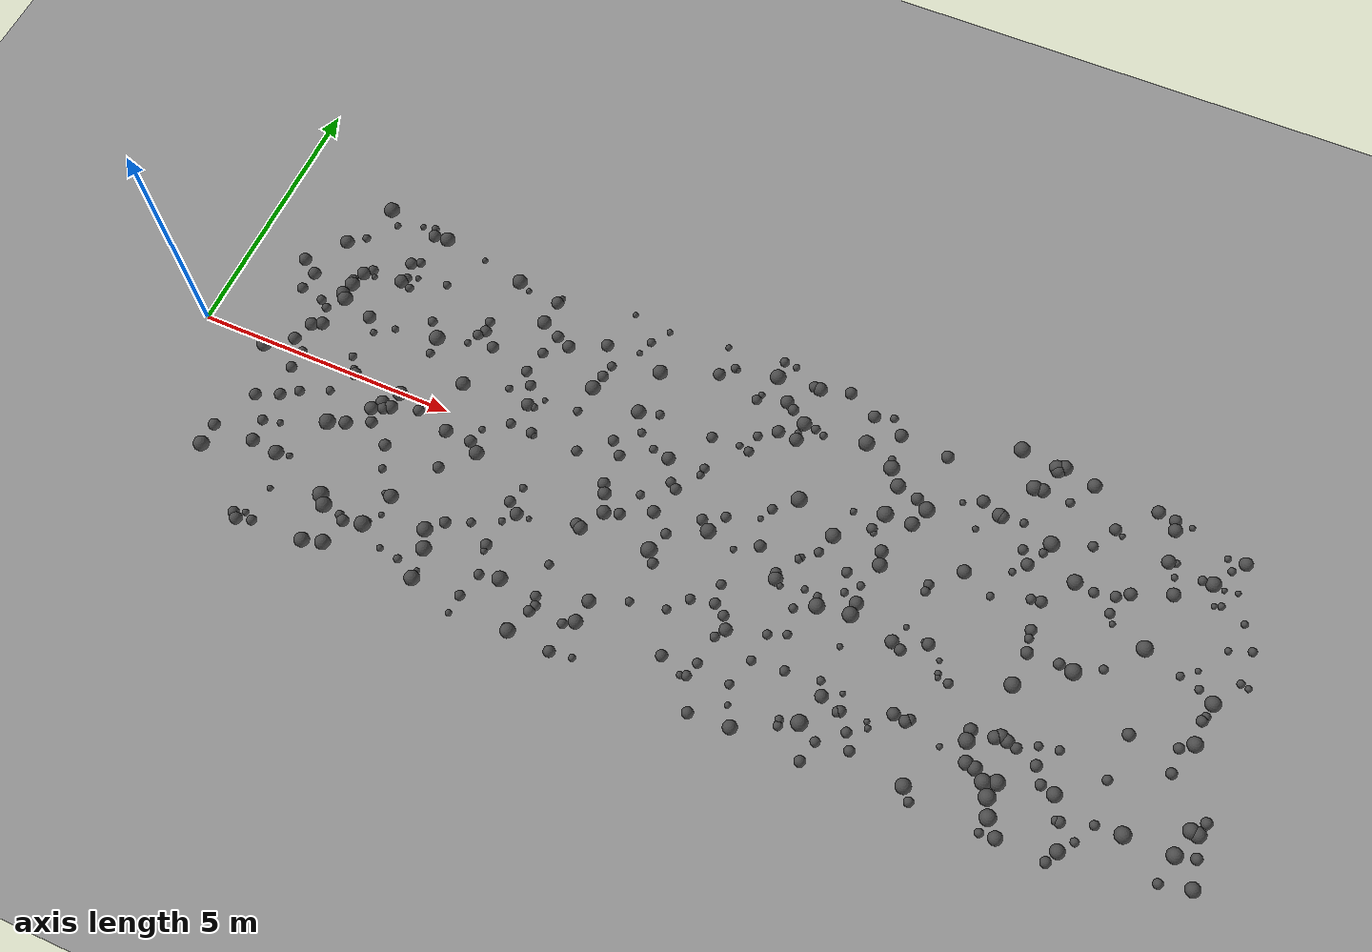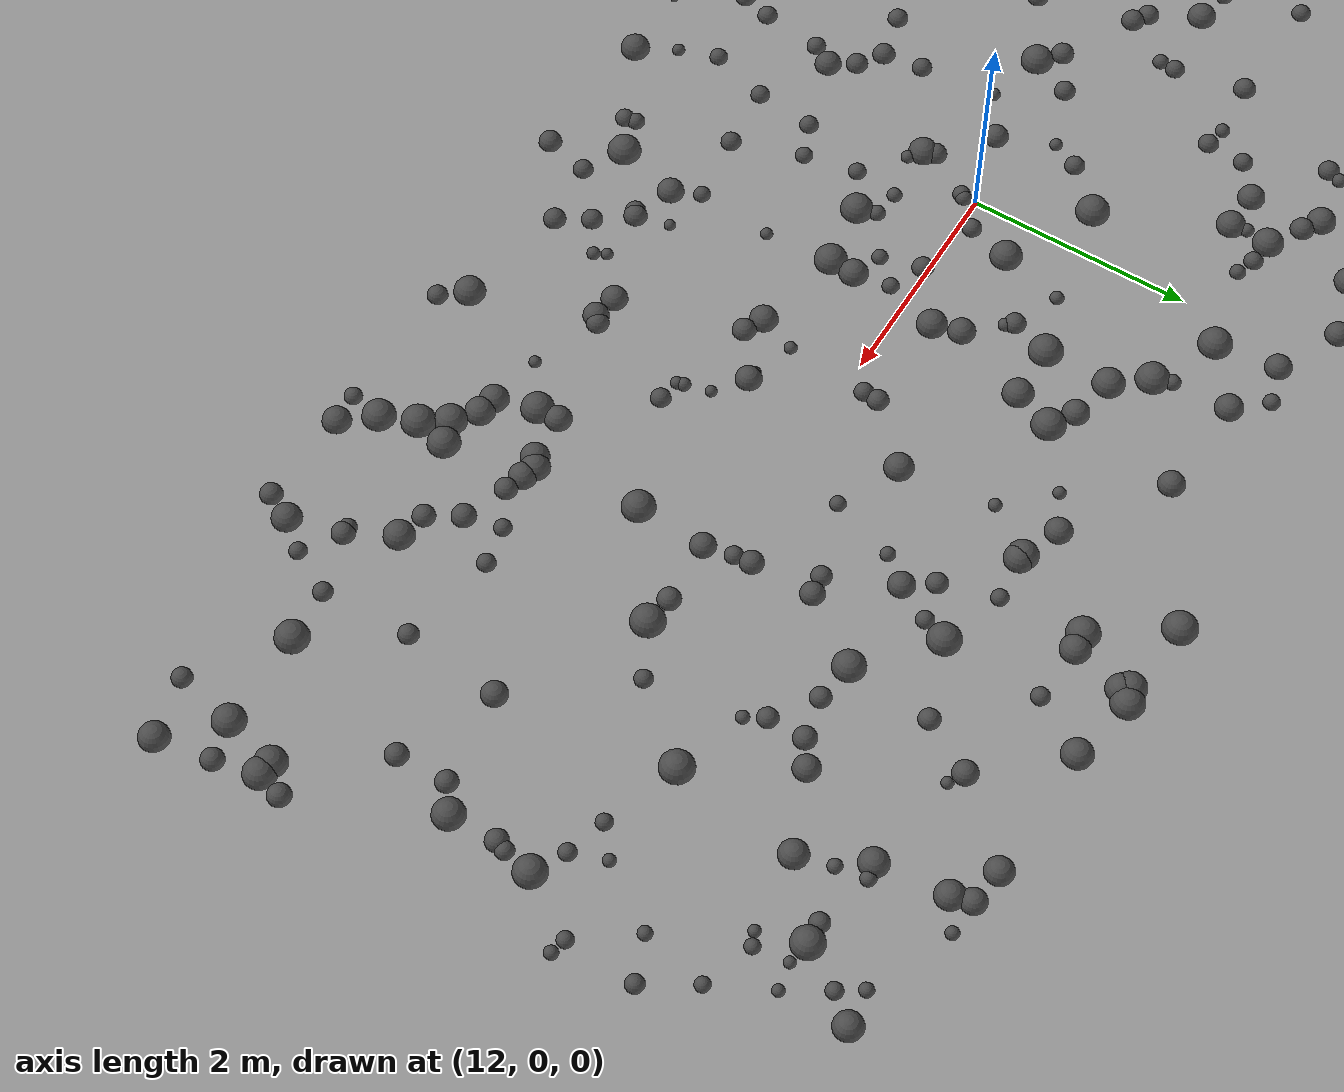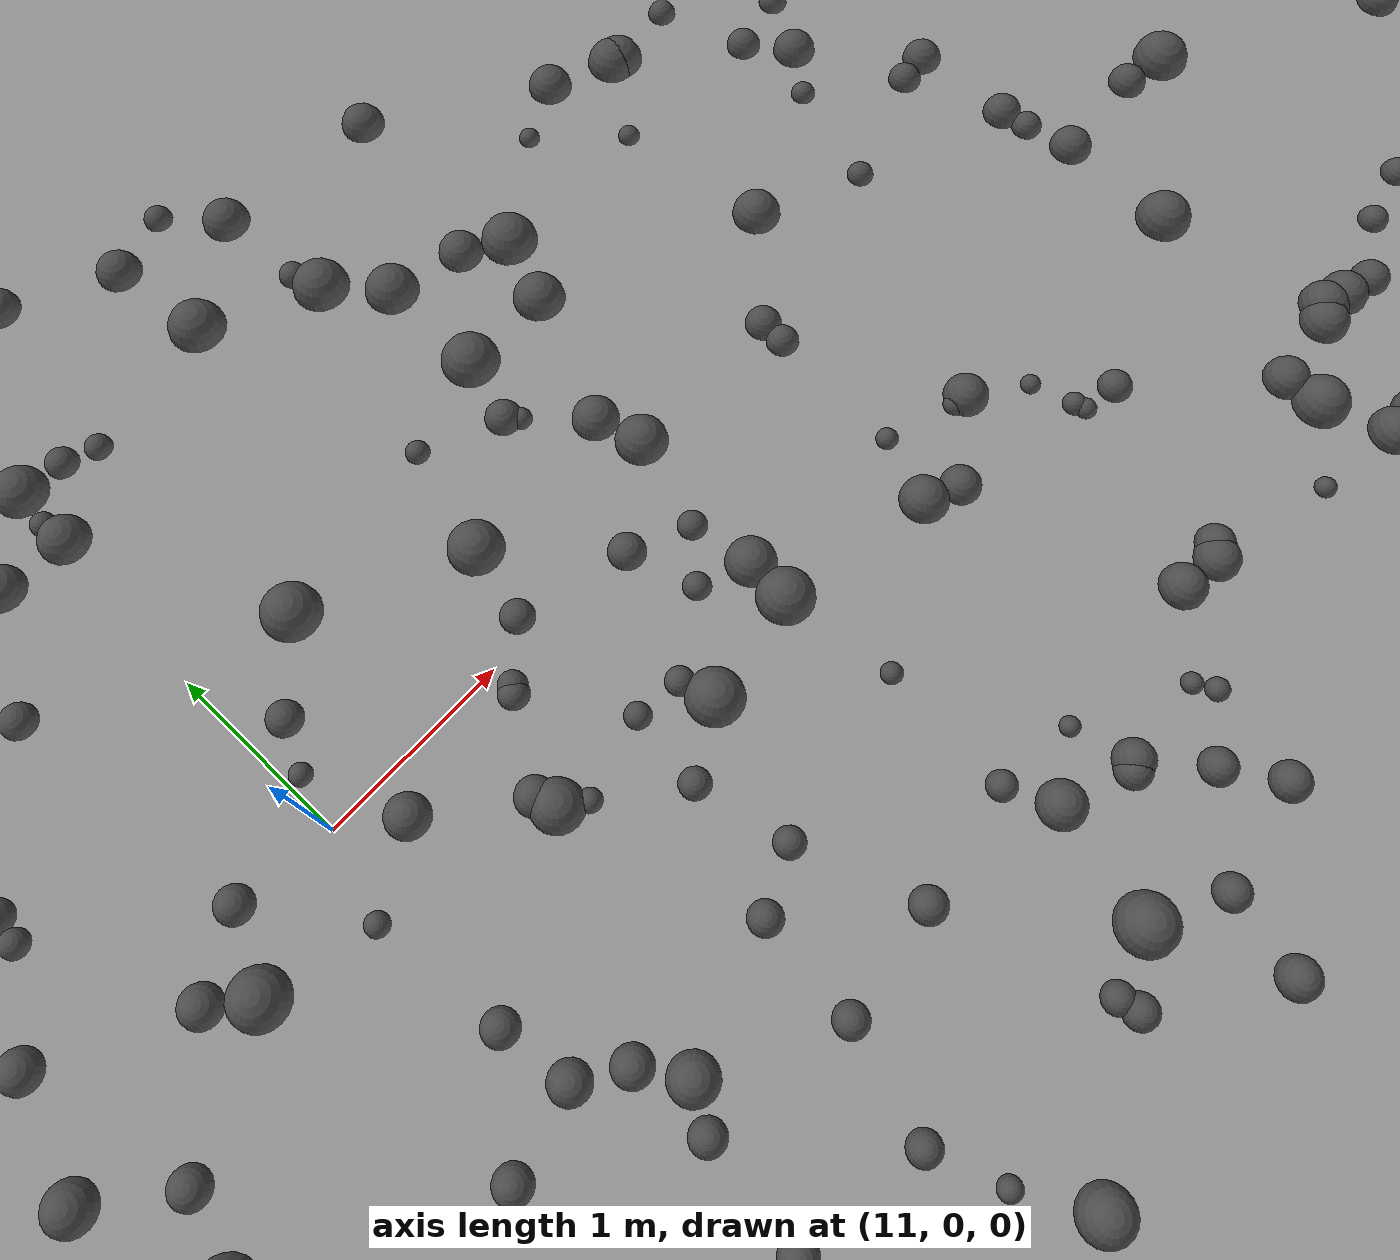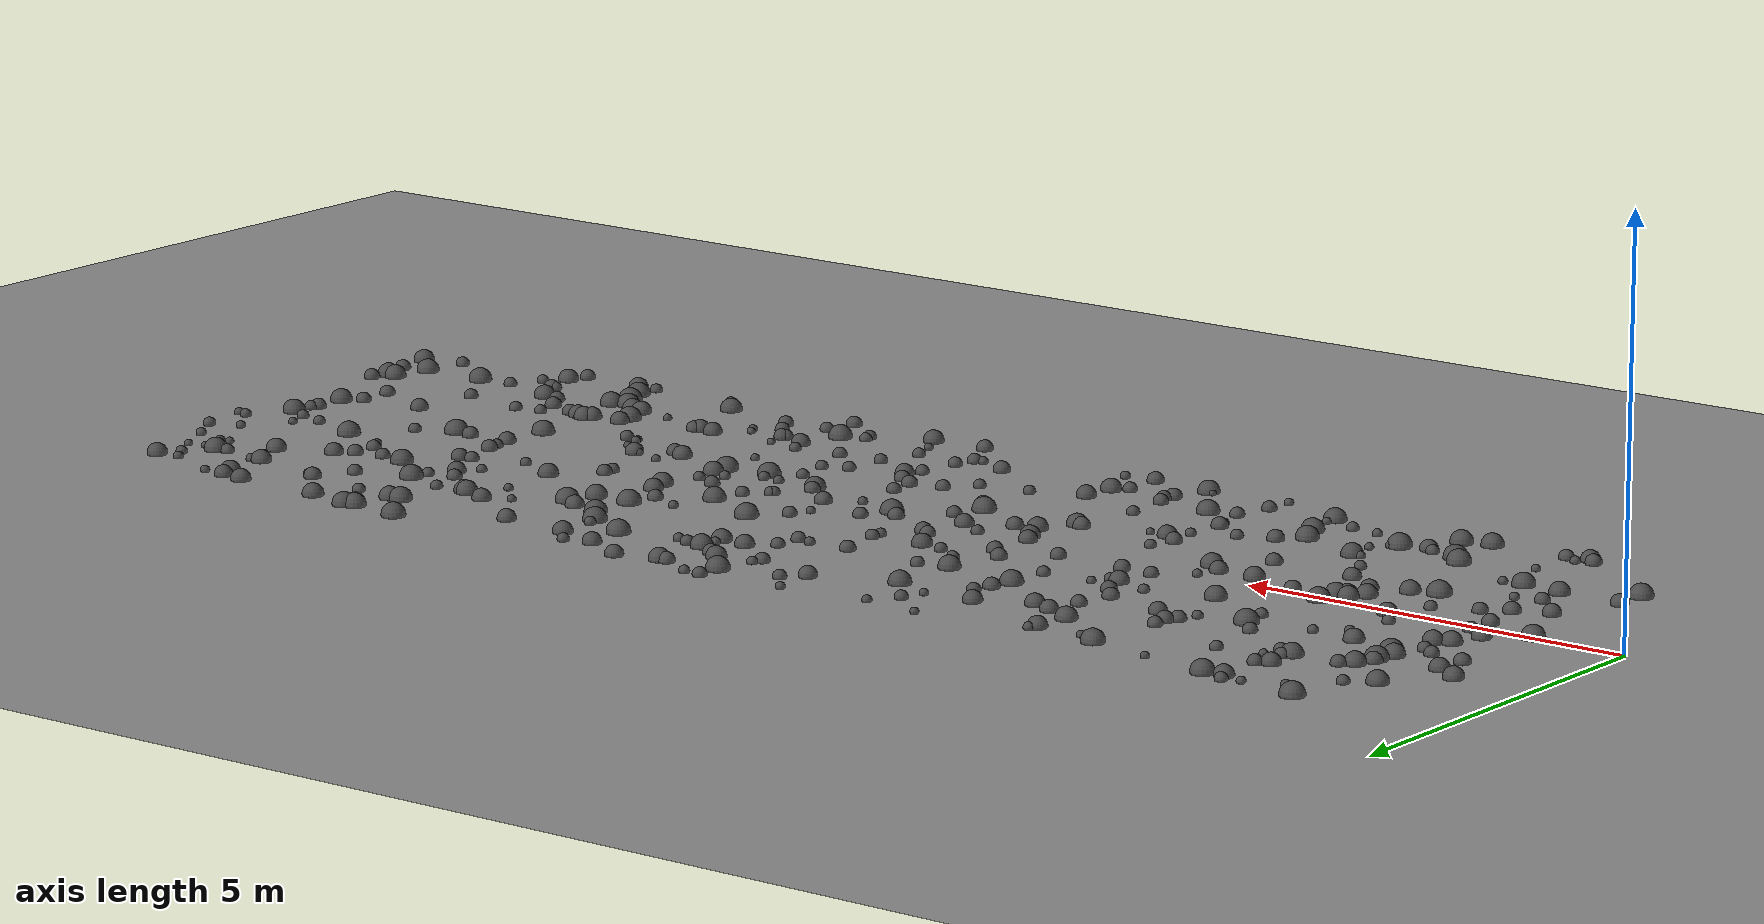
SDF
<?xml version="1.0" ?>
<sdf version="1.8">
  <world name="bumpy_world">
    <physics name="1ms" type="ignored">
      <max_step_size>0.001</max_step_size>
      <real_time_factor>1.0</real_time_factor>
    </physics>
    <plugin filename="gz-sim-physics-system" name="gz::sim::systems::Physics"/>
    <plugin filename="gz-sim-user-commands-system" name="gz::sim::systems::UserCommands"/>
    <plugin filename="gz-sim-scene-broadcaster-system" name="gz::sim::systems::SceneBroadcaster"/>

    <light type="directional" name="sun">
      <cast_shadows>true</cast_shadows>
      <pose>0 0 10 0 0 0</pose>
      <diffuse>0.8 0.8 0.8 1</diffuse>
      <specular>0.2 0.2 0.2 1</specular>
      <attenuation><range>1000</range><constant>0.9</constant><linear>0.01</linear><quadratic>0.001</quadratic></attenuation>
      <direction>-0.5 0.1 -0.9</direction>
    </light>

    <model name="ground_plane">
      <static>true</static>
      <link name="link">
        <collision name="collision">
          <geometry><plane><normal>0 0 1</normal><size>100 100</size></plane></geometry>
        </collision>
        <visual name="visual">
          <geometry><plane><normal>0 0 1</normal><size>100 100</size></plane></geometry>
          <material><ambient>0.6 0.6 0.6 1</ambient><diffuse>0.6 0.6 0.6 1</diffuse></material>
        </visual>
      </link>
    </model>

    <model name="bump_0">
      <static>true</static>
      <pose>16.894865641557914 -1.687665647435892 0.0 0 0 0</pose>
      <link name="link">
        <collision name="collision"><geometry><sphere><radius>0.0770126661770068</radius></sphere></geometry></collision>
        <visual name="visual"><geometry><sphere><radius>0.0770126661770068</radius></sphere></geometry>
        <material><ambient>0.3 0.3 0.3 1</ambient><diffuse>0.3 0.3 0.3 1</diffuse></material>
        </visual>
      </link>
    </model>

    <model name="bump_1">
      <static>true</static>
      <pose>19.27033278510874 -0.6340820807959195 0.0 0 0 0</pose>
      <link name="link">
        <collision name="collision"><geometry><sphere><radius>0.13963033782455692</radius></sphere></geometry></collision>
        <visual name="visual"><geometry><sphere><radius>0.13963033782455692</radius></sphere></geometry>
        <material><ambient>0.3 0.3 0.3 1</ambient><diffuse>0.3 0.3 0.3 1</diffuse></material>
        </visual>
      </link>
    </model>

    <model name="bump_2">
      <static>true</static>
      <pose>10.78362684058745 2.53112443563 0.0 0 0 0</pose>
      <link name="link">
        <collision name="collision"><geometry><sphere><radius>0.1036423874634214</radius></sphere></geometry></collision>
        <visual name="visual"><geometry><sphere><radius>0.1036423874634214</radius></sphere></geometry>
        <material><ambient>0.3 0.3 0.3 1</ambient><diffuse>0.3 0.3 0.3 1</diffuse></material>
        </visual>
      </link>
    </model>

    <model name="bump_3">
      <static>true</static>
      <pose>16.047348548924575 -2.4647495266084416 0.0 0 0 0</pose>
      <link name="link">
        <collision name="collision"><geometry><sphere><radius>0.1312823752196534</radius></sphere></geometry></collision>
        <visual name="visual"><geometry><sphere><radius>0.1312823752196534</radius></sphere></geometry>
        <material><ambient>0.3 0.3 0.3 1</ambient><diffuse>0.3 0.3 0.3 1</diffuse></material>
        </visual>
      </link>
    </model>

    <model name="bump_4">
      <static>true</static>
      <pose>6.986050332010324 -2.6280395016797655 0.0 0 0 0</pose>
      <link name="link">
        <collision name="collision"><geometry><sphere><radius>0.09240462821692325</radius></sphere></geometry></collision>
        <visual name="visual"><geometry><sphere><radius>0.09240462821692325</radius></sphere></geometry>
        <material><ambient>0.3 0.3 0.3 1</ambient><diffuse>0.3 0.3 0.3 1</diffuse></material>
        </visual>
      </link>
    </model>

    <model name="bump_5">
      <static>true</static>
      <pose>11.07236753158197 2.3464384934078577 0.0 0 0 0</pose>
      <link name="link">
        <collision name="collision"><geometry><sphere><radius>0.13613267017171343</radius></sphere></geometry></collision>
        <visual name="visual"><geometry><sphere><radius>0.13613267017171343</radius></sphere></geometry>
        <material><ambient>0.3 0.3 0.3 1</ambient><diffuse>0.3 0.3 0.3 1</diffuse></material>
        </visual>
      </link>
    </model>

    <model name="bump_6">
      <static>true</static>
      <pose>13.203162525665032 -0.5260972059067628 0.0 0 0 0</pose>
      <link name="link">
        <collision name="collision"><geometry><sphere><radius>0.1273605895194569</radius></sphere></geometry></collision>
        <visual name="visual"><geometry><sphere><radius>0.1273605895194569</radius></sphere></geometry>
        <material><ambient>0.3 0.3 0.3 1</ambient><diffuse>0.3 0.3 0.3 1</diffuse></material>
        </visual>
      </link>
    </model>

    <model name="bump_7">
      <static>true</static>
      <pose>10.704462672300258 2.008785588336943 0.0 0 0 0</pose>
      <link name="link">
        <collision name="collision"><geometry><sphere><radius>0.11955917482990376</radius></sphere></geometry></collision>
        <visual name="visual"><geometry><sphere><radius>0.11955917482990376</radius></sphere></geometry>
        <material><ambient>0.3 0.3 0.3 1</ambient><diffuse>0.3 0.3 0.3 1</diffuse></material>
        </visual>
      </link>
    </model>

    <model name="bump_8">
      <static>true</static>
      <pose>5.859642687130846 2.8742961816331247 0.0 0 0 0</pose>
      <link name="link">
        <collision name="collision"><geometry><sphere><radius>0.11861812440095729</radius></sphere></geometry></collision>
        <visual name="visual"><geometry><sphere><radius>0.11861812440095729</radius></sphere></geometry>
        <material><ambient>0.3 0.3 0.3 1</ambient><diffuse>0.3 0.3 0.3 1</diffuse></material>
        </visual>
      </link>
    </model>

    <model name="bump_9">
      <static>true</static>
      <pose>13.46274391247151 -3.089868944586719 0.0 0 0 0</pose>
      <link name="link">
        <collision name="collision"><geometry><sphere><radius>0.0888716582538757</radius></sphere></geometry></collision>
        <visual name="visual"><geometry><sphere><radius>0.0888716582538757</radius></sphere></geometry>
        <material><ambient>0.3 0.3 0.3 1</ambient><diffuse>0.3 0.3 0.3 1</diffuse></material>
        </visual>
      </link>
    </model>

    <model name="bump_10">
      <static>true</static>
      <pose>2.8198943444306965 -1.9201657104563592 0.0 0 0 0</pose>
      <link name="link">
        <collision name="collision"><geometry><sphere><radius>0.05871827700337499</radius></sphere></geometry></collision>
        <visual name="visual"><geometry><sphere><radius>0.05871827700337499</radius></sphere></geometry>
        <material><ambient>0.3 0.3 0.3 1</ambient><diffuse>0.3 0.3 0.3 1</diffuse></material>
        </visual>
      </link>
    </model>

    <model name="bump_11">
      <static>true</static>
      <pose>16.890118707463742 2.575693147293796 0.0 0 0 0</pose>
      <link name="link">
        <collision name="collision"><geometry><sphere><radius>0.10845833714806556</radius></sphere></geometry></collision>
        <visual name="visual"><geometry><sphere><radius>0.10845833714806556</radius></sphere></geometry>
        <material><ambient>0.3 0.3 0.3 1</ambient><diffuse>0.3 0.3 0.3 1</diffuse></material>
        </visual>
      </link>
    </model>

    <model name="bump_12">
      <static>true</static>
      <pose>3.1977501311860017 2.3142075232296957 0.0 0 0 0</pose>
      <link name="link">
        <collision name="collision"><geometry><sphere><radius>0.055547300443830605</radius></sphere></geometry></collision>
        <visual name="visual"><geometry><sphere><radius>0.055547300443830605</radius></sphere></geometry>
        <material><ambient>0.3 0.3 0.3 1</ambient><diffuse>0.3 0.3 0.3 1</diffuse></material>
        </visual>
      </link>
    </model>

    <model name="bump_13">
      <static>true</static>
      <pose>19.82699388906483 0.6549343927548907 0.0 0 0 0</pose>
      <link name="link">
        <collision name="collision"><geometry><sphere><radius>0.06008451406142055</radius></sphere></geometry></collision>
        <visual name="visual"><geometry><sphere><radius>0.06008451406142055</radius></sphere></geometry>
        <material><ambient>0.3 0.3 0.3 1</ambient><diffuse>0.3 0.3 0.3 1</diffuse></material>
        </visual>
      </link>
    </model>

    <model name="bump_14">
      <static>true</static>
      <pose>9.646156853162468 1.4279251669553972 0.0 0 0 0</pose>
      <link name="link">
        <collision name="collision"><geometry><sphere><radius>0.09876939465368231</radius></sphere></geometry></collision>
        <visual name="visual"><geometry><sphere><radius>0.09876939465368231</radius></sphere></geometry>
        <material><ambient>0.3 0.3 0.3 1</ambient><diffuse>0.3 0.3 0.3 1</diffuse></material>
        </visual>
      </link>
    </model>

    <model name="bump_15">
      <static>true</static>
      <pose>11.625946613682755 3.2676857726138175 0.0 0 0 0</pose>
      <link name="link">
        <collision name="collision"><geometry><sphere><radius>0.11263983815154456</radius></sphere></geometry></collision>
        <visual name="visual"><geometry><sphere><radius>0.11263983815154456</radius></sphere></geometry>
        <material><ambient>0.3 0.3 0.3 1</ambient><diffuse>0.3 0.3 0.3 1</diffuse></material>
        </visual>
      </link>
    </model>

    <model name="bump_16">
      <static>true</static>
      <pose>18.119850170187316 3.139718380762189 0.0 0 0 0</pose>
      <link name="link">
        <collision name="collision"><geometry><sphere><radius>0.058183244620871155</radius></sphere></geometry></collision>
        <visual name="visual"><geometry><sphere><radius>0.058183244620871155</radius></sphere></geometry>
        <material><ambient>0.3 0.3 0.3 1</ambient><diffuse>0.3 0.3 0.3 1</diffuse></material>
        </visual>
      </link>
    </model>

    <model name="bump_17">
      <static>true</static>
      <pose>6.543957091010006 0.9084461011749418 0.0 0 0 0</pose>
      <link name="link">
        <collision name="collision"><geometry><sphere><radius>0.05339405705452497</radius></sphere></geometry></collision>
        <visual name="visual"><geometry><sphere><radius>0.05339405705452497</radius></sphere></geometry>
        <material><ambient>0.3 0.3 0.3 1</ambient><diffuse>0.3 0.3 0.3 1</diffuse></material>
        </visual>
      </link>
    </model>

    <model name="bump_18">
      <static>true</static>
      <pose>19.264185863259478 -0.19718404351232843 0.0 0 0 0</pose>
      <link name="link">
        <collision name="collision"><geometry><sphere><radius>0.0996434231531243</radius></sphere></geometry></collision>
        <visual name="visual"><geometry><sphere><radius>0.0996434231531243</radius></sphere></geometry>
        <material><ambient>0.3 0.3 0.3 1</ambient><diffuse>0.3 0.3 0.3 1</diffuse></material>
        </visual>
      </link>
    </model>

    <model name="bump_19">
      <static>true</static>
      <pose>14.622045108859497 1.6115688562477875 0.0 0 0 0</pose>
      <link name="link">
        <collision name="collision"><geometry><sphere><radius>0.05853141314194617</radius></sphere></geometry></collision>
        <visual name="visual"><geometry><sphere><radius>0.05853141314194617</radius></sphere></geometry>
        <material><ambient>0.3 0.3 0.3 1</ambient><diffuse>0.3 0.3 0.3 1</diffuse></material>
        </visual>
      </link>
    </model>

    <model name="bump_20">
      <static>true</static>
      <pose>8.129874879859653 -1.0851728351112477 0.0 0 0 0</pose>
      <link name="link">
        <collision name="collision"><geometry><sphere><radius>0.10851308828290077</radius></sphere></geometry></collision>
        <visual name="visual"><geometry><sphere><radius>0.10851308828290077</radius></sphere></geometry>
        <material><ambient>0.3 0.3 0.3 1</ambient><diffuse>0.3 0.3 0.3 1</diffuse></material>
        </visual>
      </link>
    </model>

    <model name="bump_21">
      <static>true</static>
      <pose>14.965025398500424 2.016906897271027 0.0 0 0 0</pose>
      <link name="link">
        <collision name="collision"><geometry><sphere><radius>0.13155261055281017</radius></sphere></geometry></collision>
        <visual name="visual"><geometry><sphere><radius>0.13155261055281017</radius></sphere></geometry>
        <material><ambient>0.3 0.3 0.3 1</ambient><diffuse>0.3 0.3 0.3 1</diffuse></material>
        </visual>
      </link>
    </model>

    <model name="bump_22">
      <static>true</static>
      <pose>1.2356416099117413 -2.334673040265158 0.0 0 0 0</pose>
      <link name="link">
        <collision name="collision"><geometry><sphere><radius>0.14522170684553803</radius></sphere></geometry></collision>
        <visual name="visual"><geometry><sphere><radius>0.14522170684553803</radius></sphere></geometry>
        <material><ambient>0.3 0.3 0.3 1</ambient><diffuse>0.3 0.3 0.3 1</diffuse></material>
        </visual>
      </link>
    </model>

    <model name="bump_23">
      <static>true</static>
      <pose>18.211335934619928 -0.9073174179545531 0.0 0 0 0</pose>
      <link name="link">
        <collision name="collision"><geometry><sphere><radius>0.11321881905822662</radius></sphere></geometry></collision>
        <visual name="visual"><geometry><sphere><radius>0.11321881905822662</radius></sphere></geometry>
        <material><ambient>0.3 0.3 0.3 1</ambient><diffuse>0.3 0.3 0.3 1</diffuse></material>
        </visual>
      </link>
    </model>

    <model name="bump_24">
      <static>true</static>
      <pose>16.541970305903412 1.3417336470706704 0.0 0 0 0</pose>
      <link name="link">
        <collision name="collision"><geometry><sphere><radius>0.1414803609292413</radius></sphere></geometry></collision>
        <visual name="visual"><geometry><sphere><radius>0.1414803609292413</radius></sphere></geometry>
        <material><ambient>0.3 0.3 0.3 1</ambient><diffuse>0.3 0.3 0.3 1</diffuse></material>
        </visual>
      </link>
    </model>

    <model name="bump_25">
      <static>true</static>
      <pose>4.210508719758319 -2.5828001585416596 0.0 0 0 0</pose>
      <link name="link">
        <collision name="collision"><geometry><sphere><radius>0.08065998538427757</radius></sphere></geometry></collision>
        <visual name="visual"><geometry><sphere><radius>0.08065998538427757</radius></sphere></geometry>
        <material><ambient>0.3 0.3 0.3 1</ambient><diffuse>0.3 0.3 0.3 1</diffuse></material>
        </visual>
      </link>
    </model>

    <model name="bump_26">
      <static>true</static>
      <pose>10.92503154067586 -1.1284749881299905 0.0 0 0 0</pose>
      <link name="link">
        <collision name="collision"><geometry><sphere><radius>0.08945810783136997</radius></sphere></geometry></collision>
        <visual name="visual"><geometry><sphere><radius>0.08945810783136997</radius></sphere></geometry>
        <material><ambient>0.3 0.3 0.3 1</ambient><diffuse>0.3 0.3 0.3 1</diffuse></material>
        </visual>
      </link>
    </model>

    <model name="bump_27">
      <static>true</static>
      <pose>12.77173663675567 -2.9778569648907656 0.0 0 0 0</pose>
      <link name="link">
        <collision name="collision"><geometry><sphere><radius>0.0777147321736688</radius></sphere></geometry></collision>
        <visual name="visual"><geometry><sphere><radius>0.0777147321736688</radius></sphere></geometry>
        <material><ambient>0.3 0.3 0.3 1</ambient><diffuse>0.3 0.3 0.3 1</diffuse></material>
        </visual>
      </link>
    </model>

    <model name="bump_28">
      <static>true</static>
      <pose>17.547857727442413 -2.7611181875364377 0.0 0 0 0</pose>
      <link name="link">
        <collision name="collision"><geometry><sphere><radius>0.0792202904193309</radius></sphere></geometry></collision>
        <visual name="visual"><geometry><sphere><radius>0.0792202904193309</radius></sphere></geometry>
        <material><ambient>0.3 0.3 0.3 1</ambient><diffuse>0.3 0.3 0.3 1</diffuse></material>
        </visual>
      </link>
    </model>

    <model name="bump_29">
      <static>true</static>
      <pose>6.166377391203827 1.090518000518764 0.0 0 0 0</pose>
      <link name="link">
        <collision name="collision"><geometry><sphere><radius>0.09985885150011696</radius></sphere></geometry></collision>
        <visual name="visual"><geometry><sphere><radius>0.09985885150011696</radius></sphere></geometry>
        <material><ambient>0.3 0.3 0.3 1</ambient><diffuse>0.3 0.3 0.3 1</diffuse></material>
        </visual>
      </link>
    </model>

    <model name="bump_30">
      <static>true</static>
      <pose>5.882123819420187 -0.5358113656299093 0.0 0 0 0</pose>
      <link name="link">
        <collision name="collision"><geometry><sphere><radius>0.13607748315247437</radius></sphere></geometry></collision>
        <visual name="visual"><geometry><sphere><radius>0.13607748315247437</radius></sphere></geometry>
        <material><ambient>0.3 0.3 0.3 1</ambient><diffuse>0.3 0.3 0.3 1</diffuse></material>
        </visual>
      </link>
    </model>

    <model name="bump_31">
      <static>true</static>
      <pose>5.834772160398275 0.876560013550538 0.0 0 0 0</pose>
      <link name="link">
        <collision name="collision"><geometry><sphere><radius>0.06928816727679626</radius></sphere></geometry></collision>
        <visual name="visual"><geometry><sphere><radius>0.06928816727679626</radius></sphere></geometry>
        <material><ambient>0.3 0.3 0.3 1</ambient><diffuse>0.3 0.3 0.3 1</diffuse></material>
        </visual>
      </link>
    </model>

    <model name="bump_32">
      <static>true</static>
      <pose>12.888741431213155 2.147750231190747 0.0 0 0 0</pose>
      <link name="link">
        <collision name="collision"><geometry><sphere><radius>0.06974133494892694</radius></sphere></geometry></collision>
        <visual name="visual"><geometry><sphere><radius>0.06974133494892694</radius></sphere></geometry>
        <material><ambient>0.3 0.3 0.3 1</ambient><diffuse>0.3 0.3 0.3 1</diffuse></material>
        </visual>
      </link>
    </model>

    <model name="bump_33">
      <static>true</static>
      <pose>1.7474648537265793 1.1811615171004792 0.0 0 0 0</pose>
      <link name="link">
        <collision name="collision"><geometry><sphere><radius>0.08729903216262903</radius></sphere></geometry></collision>
        <visual name="visual"><geometry><sphere><radius>0.08729903216262903</radius></sphere></geometry>
        <material><ambient>0.3 0.3 0.3 1</ambient><diffuse>0.3 0.3 0.3 1</diffuse></material>
        </visual>
      </link>
    </model>

    <model name="bump_34">
      <static>true</static>
      <pose>16.46842138627019 -3.4483761148656233 0.0 0 0 0</pose>
      <link name="link">
        <collision name="collision"><geometry><sphere><radius>0.07907619362396492</radius></sphere></geometry></collision>
        <visual name="visual"><geometry><sphere><radius>0.07907619362396492</radius></sphere></geometry>
        <material><ambient>0.3 0.3 0.3 1</ambient><diffuse>0.3 0.3 0.3 1</diffuse></material>
        </visual>
      </link>
    </model>

    <model name="bump_35">
      <static>true</static>
      <pose>13.253681584001981 0.5516177332786771 0.0 0 0 0</pose>
      <link name="link">
        <collision name="collision"><geometry><sphere><radius>0.12039289845880753</radius></sphere></geometry></collision>
        <visual name="visual"><geometry><sphere><radius>0.12039289845880753</radius></sphere></geometry>
        <material><ambient>0.3 0.3 0.3 1</ambient><diffuse>0.3 0.3 0.3 1</diffuse></material>
        </visual>
      </link>
    </model>

    <model name="bump_36">
      <static>true</static>
      <pose>15.07110127573192 -3.212236173098113 0.0 0 0 0</pose>
      <link name="link">
        <collision name="collision"><geometry><sphere><radius>0.13898672384201627</radius></sphere></geometry></collision>
        <visual name="visual"><geometry><sphere><radius>0.13898672384201627</radius></sphere></geometry>
        <material><ambient>0.3 0.3 0.3 1</ambient><diffuse>0.3 0.3 0.3 1</diffuse></material>
        </visual>
      </link>
    </model>

    <model name="bump_37">
      <static>true</static>
      <pose>12.775009322838278 2.8140652479159733 0.0 0 0 0</pose>
      <link name="link">
        <collision name="collision"><geometry><sphere><radius>0.12322981319350881</radius></sphere></geometry></collision>
        <visual name="visual"><geometry><sphere><radius>0.12322981319350881</radius></sphere></geometry>
        <material><ambient>0.3 0.3 0.3 1</ambient><diffuse>0.3 0.3 0.3 1</diffuse></material>
        </visual>
      </link>
    </model>

    <model name="bump_38">
      <static>true</static>
      <pose>5.385022397268878 -1.065936186680203 0.0 0 0 0</pose>
      <link name="link">
        <collision name="collision"><geometry><sphere><radius>0.10502367716610353</radius></sphere></geometry></collision>
        <visual name="visual"><geometry><sphere><radius>0.10502367716610353</radius></sphere></geometry>
        <material><ambient>0.3 0.3 0.3 1</ambient><diffuse>0.3 0.3 0.3 1</diffuse></material>
        </visual>
      </link>
    </model>

    <model name="bump_39">
      <static>true</static>
      <pose>17.48793965364269 3.1971293868052486 0.0 0 0 0</pose>
      <link name="link">
        <collision name="collision"><geometry><sphere><radius>0.12398775786062906</radius></sphere></geometry></collision>
        <visual name="visual"><geometry><sphere><radius>0.12398775786062906</radius></sphere></geometry>
        <material><ambient>0.3 0.3 0.3 1</ambient><diffuse>0.3 0.3 0.3 1</diffuse></material>
        </visual>
      </link>
    </model>

    <model name="bump_40">
      <static>true</static>
      <pose>12.256618213254518 0.10426173945617512 0.0 0 0 0</pose>
      <link name="link">
        <collision name="collision"><geometry><sphere><radius>0.0865128517686642</radius></sphere></geometry></collision>
        <visual name="visual"><geometry><sphere><radius>0.0865128517686642</radius></sphere></geometry>
        <material><ambient>0.3 0.3 0.3 1</ambient><diffuse>0.3 0.3 0.3 1</diffuse></material>
        </visual>
      </link>
    </model>

    <model name="bump_41">
      <static>true</static>
      <pose>11.554055257485514 0.9058302469195558 0.0 0 0 0</pose>
      <link name="link">
        <collision name="collision"><geometry><sphere><radius>0.14887289297945666</radius></sphere></geometry></collision>
        <visual name="visual"><geometry><sphere><radius>0.14887289297945666</radius></sphere></geometry>
        <material><ambient>0.3 0.3 0.3 1</ambient><diffuse>0.3 0.3 0.3 1</diffuse></material>
        </visual>
      </link>
    </model>

    <model name="bump_42">
      <static>true</static>
      <pose>9.095948775680085 0.7302529021353301 0.0 0 0 0</pose>
      <link name="link">
        <collision name="collision"><geometry><sphere><radius>0.12548143702899986</radius></sphere></geometry></collision>
        <visual name="visual"><geometry><sphere><radius>0.12548143702899986</radius></sphere></geometry>
        <material><ambient>0.3 0.3 0.3 1</ambient><diffuse>0.3 0.3 0.3 1</diffuse></material>
        </visual>
      </link>
    </model>

    <model name="bump_43">
      <static>true</static>
      <pose>5.962284292612923 -2.993017639618491 0.0 0 0 0</pose>
      <link name="link">
        <collision name="collision"><geometry><sphere><radius>0.0546195513690574</radius></sphere></geometry></collision>
        <visual name="visual"><geometry><sphere><radius>0.0546195513690574</radius></sphere></geometry>
        <material><ambient>0.3 0.3 0.3 1</ambient><diffuse>0.3 0.3 0.3 1</diffuse></material>
        </visual>
      </link>
    </model>

    <model name="bump_44">
      <static>true</static>
      <pose>6.296177293382881 0.7128909430342105 0.0 0 0 0</pose>
      <link name="link">
        <collision name="collision"><geometry><sphere><radius>0.12033385122150804</radius></sphere></geometry></collision>
        <visual name="visual"><geometry><sphere><radius>0.12033385122150804</radius></sphere></geometry>
        <material><ambient>0.3 0.3 0.3 1</ambient><diffuse>0.3 0.3 0.3 1</diffuse></material>
        </visual>
      </link>
    </model>

    <model name="bump_45">
      <static>true</static>
      <pose>2.930702308674185 2.558518357739353 0.0 0 0 0</pose>
      <link name="link">
        <collision name="collision"><geometry><sphere><radius>0.11496231476188008</radius></sphere></geometry></collision>
        <visual name="visual"><geometry><sphere><radius>0.11496231476188008</radius></sphere></geometry>
        <material><ambient>0.3 0.3 0.3 1</ambient><diffuse>0.3 0.3 0.3 1</diffuse></material>
        </visual>
      </link>
    </model>

    <model name="bump_46">
      <static>true</static>
      <pose>5.166333180075391 -2.869356464584389 0.0 0 0 0</pose>
      <link name="link">
        <collision name="collision"><geometry><sphere><radius>0.06197686033442445</radius></sphere></geometry></collision>
        <visual name="visual"><geometry><sphere><radius>0.06197686033442445</radius></sphere></geometry>
        <material><ambient>0.3 0.3 0.3 1</ambient><diffuse>0.3 0.3 0.3 1</diffuse></material>
        </visual>
      </link>
    </model>

    <model name="bump_47">
      <static>true</static>
      <pose>13.157591424054585 -2.065335876533365 0.0 0 0 0</pose>
      <link name="link">
        <collision name="collision"><geometry><sphere><radius>0.07445256065702863</radius></sphere></geometry></collision>
        <visual name="visual"><geometry><sphere><radius>0.07445256065702863</radius></sphere></geometry>
        <material><ambient>0.3 0.3 0.3 1</ambient><diffuse>0.3 0.3 0.3 1</diffuse></material>
        </visual>
      </link>
    </model>

    <model name="bump_48">
      <static>true</static>
      <pose>14.571903719154566 2.16709676503301 0.0 0 0 0</pose>
      <link name="link">
        <collision name="collision"><geometry><sphere><radius>0.11821237628706183</radius></sphere></geometry></collision>
        <visual name="visual"><geometry><sphere><radius>0.11821237628706183</radius></sphere></geometry>
        <material><ambient>0.3 0.3 0.3 1</ambient><diffuse>0.3 0.3 0.3 1</diffuse></material>
        </visual>
      </link>
    </model>

    <model name="bump_49">
      <static>true</static>
      <pose>14.71944921710051 -2.1649639396403884 0.0 0 0 0</pose>
      <link name="link">
        <collision name="collision"><geometry><sphere><radius>0.11416307263552185</radius></sphere></geometry></collision>
        <visual name="visual"><geometry><sphere><radius>0.11416307263552185</radius></sphere></geometry>
        <material><ambient>0.3 0.3 0.3 1</ambient><diffuse>0.3 0.3 0.3 1</diffuse></material>
        </visual>
      </link>
    </model>

    <model name="bump_50">
      <static>true</static>
      <pose>14.926550468951985 2.027056780436517 0.0 0 0 0</pose>
      <link name="link">
        <collision name="collision"><geometry><sphere><radius>0.13505495547300034</radius></sphere></geometry></collision>
        <visual name="visual"><geometry><sphere><radius>0.13505495547300034</radius></sphere></geometry>
        <material><ambient>0.3 0.3 0.3 1</ambient><diffuse>0.3 0.3 0.3 1</diffuse></material>
        </visual>
      </link>
    </model>

    <model name="bump_51">
      <static>true</static>
      <pose>2.052149808977422 -1.9052374049976455 0.0 0 0 0</pose>
      <link name="link">
        <collision name="collision"><geometry><sphere><radius>0.1254347078864384</radius></sphere></geometry></collision>
        <visual name="visual"><geometry><sphere><radius>0.1254347078864384</radius></sphere></geometry>
        <material><ambient>0.3 0.3 0.3 1</ambient><diffuse>0.3 0.3 0.3 1</diffuse></material>
        </visual>
      </link>
    </model>

    <model name="bump_52">
      <static>true</static>
      <pose>9.596266533373393 -2.0492188293624967 0.0 0 0 0</pose>
      <link name="link">
        <collision name="collision"><geometry><sphere><radius>0.07825445300191354</radius></sphere></geometry></collision>
        <visual name="visual"><geometry><sphere><radius>0.07825445300191354</radius></sphere></geometry>
        <material><ambient>0.3 0.3 0.3 1</ambient><diffuse>0.3 0.3 0.3 1</diffuse></material>
        </visual>
      </link>
    </model>

    <model name="bump_53">
      <static>true</static>
      <pose>19.044980606334114 -0.8017717594772975 0.0 0 0 0</pose>
      <link name="link">
        <collision name="collision"><geometry><sphere><radius>0.09641213359994337</radius></sphere></geometry></collision>
        <visual name="visual"><geometry><sphere><radius>0.09641213359994337</radius></sphere></geometry>
        <material><ambient>0.3 0.3 0.3 1</ambient><diffuse>0.3 0.3 0.3 1</diffuse></material>
        </visual>
      </link>
    </model>

    <model name="bump_54">
      <static>true</static>
      <pose>1.6229721266628472 -1.0728003851126684 0.0 0 0 0</pose>
      <link name="link">
        <collision name="collision"><geometry><sphere><radius>0.11103114653822796</radius></sphere></geometry></collision>
        <visual name="visual"><geometry><sphere><radius>0.11103114653822796</radius></sphere></geometry>
        <material><ambient>0.3 0.3 0.3 1</ambient><diffuse>0.3 0.3 0.3 1</diffuse></material>
        </visual>
      </link>
    </model>

    <model name="bump_55">
      <static>true</static>
      <pose>8.478733972628643 -0.6918168067457517 0.0 0 0 0</pose>
      <link name="link">
        <collision name="collision"><geometry><sphere><radius>0.12948555192895028</radius></sphere></geometry></collision>
        <visual name="visual"><geometry><sphere><radius>0.12948555192895028</radius></sphere></geometry>
        <material><ambient>0.3 0.3 0.3 1</ambient><diffuse>0.3 0.3 0.3 1</diffuse></material>
        </visual>
      </link>
    </model>

    <model name="bump_56">
      <static>true</static>
      <pose>10.861182778202085 -0.4381310235646789 0.0 0 0 0</pose>
      <link name="link">
        <collision name="collision"><geometry><sphere><radius>0.060162493425406416</radius></sphere></geometry></collision>
        <visual name="visual"><geometry><sphere><radius>0.060162493425406416</radius></sphere></geometry>
        <material><ambient>0.3 0.3 0.3 1</ambient><diffuse>0.3 0.3 0.3 1</diffuse></material>
        </visual>
      </link>
    </model>

    <model name="bump_57">
      <static>true</static>
      <pose>16.11936705418786 0.7628343799603465 0.0 0 0 0</pose>
      <link name="link">
        <collision name="collision"><geometry><sphere><radius>0.10556045008645407</radius></sphere></geometry></collision>
        <visual name="visual"><geometry><sphere><radius>0.10556045008645407</radius></sphere></geometry>
        <material><ambient>0.3 0.3 0.3 1</ambient><diffuse>0.3 0.3 0.3 1</diffuse></material>
        </visual>
      </link>
    </model>

    <model name="bump_58">
      <static>true</static>
      <pose>7.303258439911975 1.786326979089572 0.0 0 0 0</pose>
      <link name="link">
        <collision name="collision"><geometry><sphere><radius>0.10442108447215762</radius></sphere></geometry></collision>
        <visual name="visual"><geometry><sphere><radius>0.10442108447215762</radius></sphere></geometry>
        <material><ambient>0.3 0.3 0.3 1</ambient><diffuse>0.3 0.3 0.3 1</diffuse></material>
        </visual>
      </link>
    </model>

    <model name="bump_59">
      <static>true</static>
      <pose>8.593356578144437 1.477848193703407 0.0 0 0 0</pose>
      <link name="link">
        <collision name="collision"><geometry><sphere><radius>0.08382762462507351</radius></sphere></geometry></collision>
        <visual name="visual"><geometry><sphere><radius>0.08382762462507351</radius></sphere></geometry>
        <material><ambient>0.3 0.3 0.3 1</ambient><diffuse>0.3 0.3 0.3 1</diffuse></material>
        </visual>
      </link>
    </model>

    <model name="bump_60">
      <static>true</static>
      <pose>12.19125369474031 2.9844479805425097 0.0 0 0 0</pose>
      <link name="link">
        <collision name="collision"><geometry><sphere><radius>0.11688679470605738</radius></sphere></geometry></collision>
        <visual name="visual"><geometry><sphere><radius>0.11688679470605738</radius></sphere></geometry>
        <material><ambient>0.3 0.3 0.3 1</ambient><diffuse>0.3 0.3 0.3 1</diffuse></material>
        </visual>
      </link>
    </model>

    <model name="bump_61">
      <static>true</static>
      <pose>13.077744786306905 1.849026734539227 0.0 0 0 0</pose>
      <link name="link">
        <collision name="collision"><geometry><sphere><radius>0.1403800377382815</radius></sphere></geometry></collision>
        <visual name="visual"><geometry><sphere><radius>0.1403800377382815</radius></sphere></geometry>
        <material><ambient>0.3 0.3 0.3 1</ambient><diffuse>0.3 0.3 0.3 1</diffuse></material>
        </visual>
      </link>
    </model>

    <model name="bump_62">
      <static>true</static>
      <pose>3.885796628342348 1.584061793629024 0.0 0 0 0</pose>
      <link name="link">
        <collision name="collision"><geometry><sphere><radius>0.08964944021255997</radius></sphere></geometry></collision>
        <visual name="visual"><geometry><sphere><radius>0.08964944021255997</radius></sphere></geometry>
        <material><ambient>0.3 0.3 0.3 1</ambient><diffuse>0.3 0.3 0.3 1</diffuse></material>
        </visual>
      </link>
    </model>

    <model name="bump_63">
      <static>true</static>
      <pose>14.18231250398071 -2.529547998363991 0.0 0 0 0</pose>
      <link name="link">
        <collision name="collision"><geometry><sphere><radius>0.05902556037477772</radius></sphere></geometry></collision>
        <visual name="visual"><geometry><sphere><radius>0.05902556037477772</radius></sphere></geometry>
        <material><ambient>0.3 0.3 0.3 1</ambient><diffuse>0.3 0.3 0.3 1</diffuse></material>
        </visual>
      </link>
    </model>

    <model name="bump_64">
      <static>true</static>
      <pose>17.272906880037652 1.3653921142893646 0.0 0 0 0</pose>
      <link name="link">
        <collision name="collision"><geometry><sphere><radius>0.10078895861672221</radius></sphere></geometry></collision>
        <visual name="visual"><geometry><sphere><radius>0.10078895861672221</radius></sphere></geometry>
        <material><ambient>0.3 0.3 0.3 1</ambient><diffuse>0.3 0.3 0.3 1</diffuse></material>
        </visual>
      </link>
    </model>

    <model name="bump_65">
      <static>true</static>
      <pose>18.56745231552609 2.246675519682185 0.0 0 0 0</pose>
      <link name="link">
        <collision name="collision"><geometry><sphere><radius>0.08511446592290171</radius></sphere></geometry></collision>
        <visual name="visual"><geometry><sphere><radius>0.08511446592290171</radius></sphere></geometry>
        <material><ambient>0.3 0.3 0.3 1</ambient><diffuse>0.3 0.3 0.3 1</diffuse></material>
        </visual>
      </link>
    </model>

    <model name="bump_66">
      <static>true</static>
      <pose>14.87307635986048 -0.9375364905134278 0.0 0 0 0</pose>
      <link name="link">
        <collision name="collision"><geometry><sphere><radius>0.051546870938938665</radius></sphere></geometry></collision>
        <visual name="visual"><geometry><sphere><radius>0.051546870938938665</radius></sphere></geometry>
        <material><ambient>0.3 0.3 0.3 1</ambient><diffuse>0.3 0.3 0.3 1</diffuse></material>
        </visual>
      </link>
    </model>

    <model name="bump_67">
      <static>true</static>
      <pose>13.001153981545839 0.8274194099034222 0.0 0 0 0</pose>
      <link name="link">
        <collision name="collision"><geometry><sphere><radius>0.05875180347101103</radius></sphere></geometry></collision>
        <visual name="visual"><geometry><sphere><radius>0.05875180347101103</radius></sphere></geometry>
        <material><ambient>0.3 0.3 0.3 1</ambient><diffuse>0.3 0.3 0.3 1</diffuse></material>
        </visual>
      </link>
    </model>

    <model name="bump_68">
      <static>true</static>
      <pose>3.710123732801496 -2.3693969549017107 0.0 0 0 0</pose>
      <link name="link">
        <collision name="collision"><geometry><sphere><radius>0.14830360818643148</radius></sphere></geometry></collision>
        <visual name="visual"><geometry><sphere><radius>0.14830360818643148</radius></sphere></geometry>
        <material><ambient>0.3 0.3 0.3 1</ambient><diffuse>0.3 0.3 0.3 1</diffuse></material>
        </visual>
      </link>
    </model>

    <model name="bump_69">
      <static>true</static>
      <pose>6.411673878166645 -1.7986127388598796 0.0 0 0 0</pose>
      <link name="link">
        <collision name="collision"><geometry><sphere><radius>0.08051269885244494</radius></sphere></geometry></collision>
        <visual name="visual"><geometry><sphere><radius>0.08051269885244494</radius></sphere></geometry>
        <material><ambient>0.3 0.3 0.3 1</ambient><diffuse>0.3 0.3 0.3 1</diffuse></material>
        </visual>
      </link>
    </model>

    <model name="bump_70">
      <static>true</static>
      <pose>4.734207004023243 -2.5053065922183353 0.0 0 0 0</pose>
      <link name="link">
        <collision name="collision"><geometry><sphere><radius>0.06399001163010644</radius></sphere></geometry></collision>
        <visual name="visual"><geometry><sphere><radius>0.06399001163010644</radius></sphere></geometry>
        <material><ambient>0.3 0.3 0.3 1</ambient><diffuse>0.3 0.3 0.3 1</diffuse></material>
        </visual>
      </link>
    </model>

    <model name="bump_71">
      <static>true</static>
      <pose>12.84168985758485 -0.05218294023085823 0.0 0 0 0</pose>
      <link name="link">
        <collision name="collision"><geometry><sphere><radius>0.09575622092741645</radius></sphere></geometry></collision>
        <visual name="visual"><geometry><sphere><radius>0.09575622092741645</radius></sphere></geometry>
        <material><ambient>0.3 0.3 0.3 1</ambient><diffuse>0.3 0.3 0.3 1</diffuse></material>
        </visual>
      </link>
    </model>

    <model name="bump_72">
      <static>true</static>
      <pose>8.439496865026612 1.0107370996487335 0.0 0 0 0</pose>
      <link name="link">
        <collision name="collision"><geometry><sphere><radius>0.07745681922337713</radius></sphere></geometry></collision>
        <visual name="visual"><geometry><sphere><radius>0.07745681922337713</radius></sphere></geometry>
        <material><ambient>0.3 0.3 0.3 1</ambient><diffuse>0.3 0.3 0.3 1</diffuse></material>
        </visual>
      </link>
    </model>

    <model name="bump_73">
      <static>true</static>
      <pose>3.831733680356071 -3.268893120792354 0.0 0 0 0</pose>
      <link name="link">
        <collision name="collision"><geometry><sphere><radius>0.1375089017497998</radius></sphere></geometry></collision>
        <visual name="visual"><geometry><sphere><radius>0.1375089017497998</radius></sphere></geometry>
        <material><ambient>0.3 0.3 0.3 1</ambient><diffuse>0.3 0.3 0.3 1</diffuse></material>
        </visual>
      </link>
    </model>

    <model name="bump_74">
      <static>true</static>
      <pose>8.036774367762323 0.6623960478121784 0.0 0 0 0</pose>
      <link name="link">
        <collision name="collision"><geometry><sphere><radius>0.1025925052121281</radius></sphere></geometry></collision>
        <visual name="visual"><geometry><sphere><radius>0.1025925052121281</radius></sphere></geometry>
        <material><ambient>0.3 0.3 0.3 1</ambient><diffuse>0.3 0.3 0.3 1</diffuse></material>
        </visual>
      </link>
    </model>

    <model name="bump_75">
      <static>true</static>
      <pose>8.05543637325164 3.13072448044593 0.0 0 0 0</pose>
      <link name="link">
        <collision name="collision"><geometry><sphere><radius>0.05987468543487567</radius></sphere></geometry></collision>
        <visual name="visual"><geometry><sphere><radius>0.05987468543487567</radius></sphere></geometry>
        <material><ambient>0.3 0.3 0.3 1</ambient><diffuse>0.3 0.3 0.3 1</diffuse></material>
        </visual>
      </link>
    </model>

    <model name="bump_76">
      <static>true</static>
      <pose>12.791041421157644 -3.0798658523143274 0.0 0 0 0</pose>
      <link name="link">
        <collision name="collision"><geometry><sphere><radius>0.0850777389592967</radius></sphere></geometry></collision>
        <visual name="visual"><geometry><sphere><radius>0.0850777389592967</radius></sphere></geometry>
        <material><ambient>0.3 0.3 0.3 1</ambient><diffuse>0.3 0.3 0.3 1</diffuse></material>
        </visual>
      </link>
    </model>

    <model name="bump_77">
      <static>true</static>
      <pose>12.526068392680772 1.0733581746996483 0.0 0 0 0</pose>
      <link name="link">
        <collision name="collision"><geometry><sphere><radius>0.061747364357610336</radius></sphere></geometry></collision>
        <visual name="visual"><geometry><sphere><radius>0.061747364357610336</radius></sphere></geometry>
        <material><ambient>0.3 0.3 0.3 1</ambient><diffuse>0.3 0.3 0.3 1</diffuse></material>
        </visual>
      </link>
    </model>

    <model name="bump_78">
      <static>true</static>
      <pose>5.9722479871555505 1.3281626954364478 0.0 0 0 0</pose>
      <link name="link">
        <collision name="collision"><geometry><sphere><radius>0.10197502283126336</radius></sphere></geometry></collision>
        <visual name="visual"><geometry><sphere><radius>0.10197502283126336</radius></sphere></geometry>
        <material><ambient>0.3 0.3 0.3 1</ambient><diffuse>0.3 0.3 0.3 1</diffuse></material>
        </visual>
      </link>
    </model>

    <model name="bump_79">
      <static>true</static>
      <pose>19.454917901876023 1.7552413308411579 0.0 0 0 0</pose>
      <link name="link">
        <collision name="collision"><geometry><sphere><radius>0.06640403343030907</radius></sphere></geometry></collision>
        <visual name="visual"><geometry><sphere><radius>0.06640403343030907</radius></sphere></geometry>
        <material><ambient>0.3 0.3 0.3 1</ambient><diffuse>0.3 0.3 0.3 1</diffuse></material>
        </visual>
      </link>
    </model>

    <model name="bump_80">
      <static>true</static>
      <pose>12.010883348760713 -1.6597990454577753 0.0 0 0 0</pose>
      <link name="link">
        <collision name="collision"><geometry><sphere><radius>0.08428400428994884</radius></sphere></geometry></collision>
        <visual name="visual"><geometry><sphere><radius>0.08428400428994884</radius></sphere></geometry>
        <material><ambient>0.3 0.3 0.3 1</ambient><diffuse>0.3 0.3 0.3 1</diffuse></material>
        </visual>
      </link>
    </model>

    <model name="bump_81">
      <static>true</static>
      <pose>19.91003569966445 -2.9588037231534967 0.0 0 0 0</pose>
      <link name="link">
        <collision name="collision"><geometry><sphere><radius>0.13193395944975517</radius></sphere></geometry></collision>
        <visual name="visual"><geometry><sphere><radius>0.13193395944975517</radius></sphere></geometry>
        <material><ambient>0.3 0.3 0.3 1</ambient><diffuse>0.3 0.3 0.3 1</diffuse></material>
        </visual>
      </link>
    </model>

    <model name="bump_82">
      <static>true</static>
      <pose>14.217627064056918 0.15215715944270158 0.0 0 0 0</pose>
      <link name="link">
        <collision name="collision"><geometry><sphere><radius>0.08499574275729208</radius></sphere></geometry></collision>
        <visual name="visual"><geometry><sphere><radius>0.08499574275729208</radius></sphere></geometry>
        <material><ambient>0.3 0.3 0.3 1</ambient><diffuse>0.3 0.3 0.3 1</diffuse></material>
        </visual>
      </link>
    </model>

    <model name="bump_83">
      <static>true</static>
      <pose>15.48315533770354 1.0952772332607488 0.0 0 0 0</pose>
      <link name="link">
        <collision name="collision"><geometry><sphere><radius>0.06484741985039635</radius></sphere></geometry></collision>
        <visual name="visual"><geometry><sphere><radius>0.06484741985039635</radius></sphere></geometry>
        <material><ambient>0.3 0.3 0.3 1</ambient><diffuse>0.3 0.3 0.3 1</diffuse></material>
        </visual>
      </link>
    </model>

    <model name="bump_84">
      <static>true</static>
      <pose>11.765441365856477 -2.73373470274147 0.0 0 0 0</pose>
      <link name="link">
        <collision name="collision"><geometry><sphere><radius>0.08095452946047246</radius></sphere></geometry></collision>
        <visual name="visual"><geometry><sphere><radius>0.08095452946047246</radius></sphere></geometry>
        <material><ambient>0.3 0.3 0.3 1</ambient><diffuse>0.3 0.3 0.3 1</diffuse></material>
        </visual>
      </link>
    </model>

    <model name="bump_85">
      <static>true</static>
      <pose>14.243576926300605 2.002929514089841 0.0 0 0 0</pose>
      <link name="link">
        <collision name="collision"><geometry><sphere><radius>0.05576142466802508</radius></sphere></geometry></collision>
        <visual name="visual"><geometry><sphere><radius>0.05576142466802508</radius></sphere></geometry>
        <material><ambient>0.3 0.3 0.3 1</ambient><diffuse>0.3 0.3 0.3 1</diffuse></material>
        </visual>
      </link>
    </model>

    <model name="bump_86">
      <static>true</static>
      <pose>19.351062935832438 0.16156882192562438 0.0 0 0 0</pose>
      <link name="link">
        <collision name="collision"><geometry><sphere><radius>0.14171831125933976</radius></sphere></geometry></collision>
        <visual name="visual"><geometry><sphere><radius>0.14171831125933976</radius></sphere></geometry>
        <material><ambient>0.3 0.3 0.3 1</ambient><diffuse>0.3 0.3 0.3 1</diffuse></material>
        </visual>
      </link>
    </model>

    <model name="bump_87">
      <static>true</static>
      <pose>19.053474912040453 -1.2618177397716237 0.0 0 0 0</pose>
      <link name="link">
        <collision name="collision"><geometry><sphere><radius>0.09848311392736778</radius></sphere></geometry></collision>
        <visual name="visual"><geometry><sphere><radius>0.09848311392736778</radius></sphere></geometry>
        <material><ambient>0.3 0.3 0.3 1</ambient><diffuse>0.3 0.3 0.3 1</diffuse></material>
        </visual>
      </link>
    </model>

    <model name="bump_88">
      <static>true</static>
      <pose>3.7153868618442027 -0.48606740721496067 0.0 0 0 0</pose>
      <link name="link">
        <collision name="collision"><geometry><sphere><radius>0.1274575614804378</radius></sphere></geometry></collision>
        <visual name="visual"><geometry><sphere><radius>0.1274575614804378</radius></sphere></geometry>
        <material><ambient>0.3 0.3 0.3 1</ambient><diffuse>0.3 0.3 0.3 1</diffuse></material>
        </visual>
      </link>
    </model>

    <model name="bump_89">
      <static>true</static>
      <pose>17.03513688449517 2.4987586148283114 0.0 0 0 0</pose>
      <link name="link">
        <collision name="collision"><geometry><sphere><radius>0.05225523030715243</radius></sphere></geometry></collision>
        <visual name="visual"><geometry><sphere><radius>0.05225523030715243</radius></sphere></geometry>
        <material><ambient>0.3 0.3 0.3 1</ambient><diffuse>0.3 0.3 0.3 1</diffuse></material>
        </visual>
      </link>
    </model>

    <model name="bump_90">
      <static>true</static>
      <pose>13.612311818848625 -2.461958967080199 0.0 0 0 0</pose>
      <link name="link">
        <collision name="collision"><geometry><sphere><radius>0.09233882621058961</radius></sphere></geometry></collision>
        <visual name="visual"><geometry><sphere><radius>0.09233882621058961</radius></sphere></geometry>
        <material><ambient>0.3 0.3 0.3 1</ambient><diffuse>0.3 0.3 0.3 1</diffuse></material>
        </visual>
      </link>
    </model>

    <model name="bump_91">
      <static>true</static>
      <pose>13.268905371906861 -2.3153303758690162 0.0 0 0 0</pose>
      <link name="link">
        <collision name="collision"><geometry><sphere><radius>0.11872014321630436</radius></sphere></geometry></collision>
        <visual name="visual"><geometry><sphere><radius>0.11872014321630436</radius></sphere></geometry>
        <material><ambient>0.3 0.3 0.3 1</ambient><diffuse>0.3 0.3 0.3 1</diffuse></material>
        </visual>
      </link>
    </model>

    <model name="bump_92">
      <static>true</static>
      <pose>14.713548656431364 0.7647789625414152 0.0 0 0 0</pose>
      <link name="link">
        <collision name="collision"><geometry><sphere><radius>0.12755117541166835</radius></sphere></geometry></collision>
        <visual name="visual"><geometry><sphere><radius>0.12755117541166835</radius></sphere></geometry>
        <material><ambient>0.3 0.3 0.3 1</ambient><diffuse>0.3 0.3 0.3 1</diffuse></material>
        </visual>
      </link>
    </model>

    <model name="bump_93">
      <static>true</static>
      <pose>3.0826629513447363 2.6470790627789427 0.0 0 0 0</pose>
      <link name="link">
        <collision name="collision"><geometry><sphere><radius>0.0905556618998537</radius></sphere></geometry></collision>
        <visual name="visual"><geometry><sphere><radius>0.0905556618998537</radius></sphere></geometry>
        <material><ambient>0.3 0.3 0.3 1</ambient><diffuse>0.3 0.3 0.3 1</diffuse></material>
        </visual>
      </link>
    </model>

    <model name="bump_94">
      <static>true</static>
      <pose>1.8386751377057422 0.6395333112134258 0.0 0 0 0</pose>
      <link name="link">
        <collision name="collision"><geometry><sphere><radius>0.1251058097517386</radius></sphere></geometry></collision>
        <visual name="visual"><geometry><sphere><radius>0.1251058097517386</radius></sphere></geometry>
        <material><ambient>0.3 0.3 0.3 1</ambient><diffuse>0.3 0.3 0.3 1</diffuse></material>
        </visual>
      </link>
    </model>

    <model name="bump_95">
      <static>true</static>
      <pose>11.749811479082627 -0.6565528794193205 0.0 0 0 0</pose>
      <link name="link">
        <collision name="collision"><geometry><sphere><radius>0.1316098256338052</radius></sphere></geometry></collision>
        <visual name="visual"><geometry><sphere><radius>0.1316098256338052</radius></sphere></geometry>
        <material><ambient>0.3 0.3 0.3 1</ambient><diffuse>0.3 0.3 0.3 1</diffuse></material>
        </visual>
      </link>
    </model>

    <model name="bump_96">
      <static>true</static>
      <pose>18.11672064690927 -1.7843513054658986 0.0 0 0 0</pose>
      <link name="link">
        <collision name="collision"><geometry><sphere><radius>0.08833786254354743</radius></sphere></geometry></collision>
        <visual name="visual"><geometry><sphere><radius>0.08833786254354743</radius></sphere></geometry>
        <material><ambient>0.3 0.3 0.3 1</ambient><diffuse>0.3 0.3 0.3 1</diffuse></material>
        </visual>
      </link>
    </model>

    <model name="bump_97">
      <static>true</static>
      <pose>2.4632255060504904 -3.2790495559302224 0.0 0 0 0</pose>
      <link name="link">
        <collision name="collision"><geometry><sphere><radius>0.10094150722244792</radius></sphere></geometry></collision>
        <visual name="visual"><geometry><sphere><radius>0.10094150722244792</radius></sphere></geometry>
        <material><ambient>0.3 0.3 0.3 1</ambient><diffuse>0.3 0.3 0.3 1</diffuse></material>
        </visual>
      </link>
    </model>

    <model name="bump_98">
      <static>true</static>
      <pose>2.2825291329505166 3.219972751323204 0.0 0 0 0</pose>
      <link name="link">
        <collision name="collision"><geometry><sphere><radius>0.06255795516376597</radius></sphere></geometry></collision>
        <visual name="visual"><geometry><sphere><radius>0.06255795516376597</radius></sphere></geometry>
        <material><ambient>0.3 0.3 0.3 1</ambient><diffuse>0.3 0.3 0.3 1</diffuse></material>
        </visual>
      </link>
    </model>

    <model name="bump_99">
      <static>true</static>
      <pose>6.867712009358482 -2.1936542390114644 0.0 0 0 0</pose>
      <link name="link">
        <collision name="collision"><geometry><sphere><radius>0.06180041714824539</radius></sphere></geometry></collision>
        <visual name="visual"><geometry><sphere><radius>0.06180041714824539</radius></sphere></geometry>
        <material><ambient>0.3 0.3 0.3 1</ambient><diffuse>0.3 0.3 0.3 1</diffuse></material>
        </visual>
      </link>
    </model>

    <model name="bump_100">
      <static>true</static>
      <pose>7.105513186303753 2.4134970081033806 0.0 0 0 0</pose>
      <link name="link">
        <collision name="collision"><geometry><sphere><radius>0.11846577365311108</radius></sphere></geometry></collision>
        <visual name="visual"><geometry><sphere><radius>0.11846577365311108</radius></sphere></geometry>
        <material><ambient>0.3 0.3 0.3 1</ambient><diffuse>0.3 0.3 0.3 1</diffuse></material>
        </visual>
      </link>
    </model>

    <model name="bump_101">
      <static>true</static>
      <pose>2.113953201336293 1.7131597052439798 0.0 0 0 0</pose>
      <link name="link">
        <collision name="collision"><geometry><sphere><radius>0.140882410743292</radius></sphere></geometry></collision>
        <visual name="visual"><geometry><sphere><radius>0.140882410743292</radius></sphere></geometry>
        <material><ambient>0.3 0.3 0.3 1</ambient><diffuse>0.3 0.3 0.3 1</diffuse></material>
        </visual>
      </link>
    </model>

    <model name="bump_102">
      <static>true</static>
      <pose>2.839772443935972 -0.4636828391519221 0.0 0 0 0</pose>
      <link name="link">
        <collision name="collision"><geometry><sphere><radius>0.07872676548192606</radius></sphere></geometry></collision>
        <visual name="visual"><geometry><sphere><radius>0.07872676548192606</radius></sphere></geometry>
        <material><ambient>0.3 0.3 0.3 1</ambient><diffuse>0.3 0.3 0.3 1</diffuse></material>
        </visual>
      </link>
    </model>

    <model name="bump_103">
      <static>true</static>
      <pose>9.520685048044456 2.8961846301688867 0.0 0 0 0</pose>
      <link name="link">
        <collision name="collision"><geometry><sphere><radius>0.061110428575138744</radius></sphere></geometry></collision>
        <visual name="visual"><geometry><sphere><radius>0.061110428575138744</radius></sphere></geometry>
        <material><ambient>0.3 0.3 0.3 1</ambient><diffuse>0.3 0.3 0.3 1</diffuse></material>
        </visual>
      </link>
    </model>

    <model name="bump_104">
      <static>true</static>
      <pose>2.3305961854765145 2.1366397159677195 0.0 0 0 0</pose>
      <link name="link">
        <collision name="collision"><geometry><sphere><radius>0.09502109782018386</radius></sphere></geometry></collision>
        <visual name="visual"><geometry><sphere><radius>0.09502109782018386</radius></sphere></geometry>
        <material><ambient>0.3 0.3 0.3 1</ambient><diffuse>0.3 0.3 0.3 1</diffuse></material>
        </visual>
      </link>
    </model>

    <model name="bump_105">
      <static>true</static>
      <pose>13.693155858475201 2.743779183230428 0.0 0 0 0</pose>
      <link name="link">
        <collision name="collision"><geometry><sphere><radius>0.11640735099929735</radius></sphere></geometry></collision>
        <visual name="visual"><geometry><sphere><radius>0.11640735099929735</radius></sphere></geometry>
        <material><ambient>0.3 0.3 0.3 1</ambient><diffuse>0.3 0.3 0.3 1</diffuse></material>
        </visual>
      </link>
    </model>

    <model name="bump_106">
      <static>true</static>
      <pose>4.896003765921296 1.793798868112928 0.0 0 0 0</pose>
      <link name="link">
        <collision name="collision"><geometry><sphere><radius>0.10546946665457382</radius></sphere></geometry></collision>
        <visual name="visual"><geometry><sphere><radius>0.10546946665457382</radius></sphere></geometry>
        <material><ambient>0.3 0.3 0.3 1</ambient><diffuse>0.3 0.3 0.3 1</diffuse></material>
        </visual>
      </link>
    </model>

    <model name="bump_107">
      <static>true</static>
      <pose>19.064797850925974 0.31498275369659856 0.0 0 0 0</pose>
      <link name="link">
        <collision name="collision"><geometry><sphere><radius>0.0760409565244126</radius></sphere></geometry></collision>
        <visual name="visual"><geometry><sphere><radius>0.0760409565244126</radius></sphere></geometry>
        <material><ambient>0.3 0.3 0.3 1</ambient><diffuse>0.3 0.3 0.3 1</diffuse></material>
        </visual>
      </link>
    </model>

    <model name="bump_108">
      <static>true</static>
      <pose>8.21340566274562 1.3752197935222288 0.0 0 0 0</pose>
      <link name="link">
        <collision name="collision"><geometry><sphere><radius>0.13565722947801195</radius></sphere></geometry></collision>
        <visual name="visual"><geometry><sphere><radius>0.13565722947801195</radius></sphere></geometry>
        <material><ambient>0.3 0.3 0.3 1</ambient><diffuse>0.3 0.3 0.3 1</diffuse></material>
        </visual>
      </link>
    </model>

    <model name="bump_109">
      <static>true</static>
      <pose>12.326138086171571 -1.5259539511885036 0.0 0 0 0</pose>
      <link name="link">
        <collision name="collision"><geometry><sphere><radius>0.0774266165104542</radius></sphere></geometry></collision>
        <visual name="visual"><geometry><sphere><radius>0.0774266165104542</radius></sphere></geometry>
        <material><ambient>0.3 0.3 0.3 1</ambient><diffuse>0.3 0.3 0.3 1</diffuse></material>
        </visual>
      </link>
    </model>

    <model name="bump_110">
      <static>true</static>
      <pose>19.714448294070483 1.3224208898128964 0.0 0 0 0</pose>
      <link name="link">
        <collision name="collision"><geometry><sphere><radius>0.08004943521593696</radius></sphere></geometry></collision>
        <visual name="visual"><geometry><sphere><radius>0.08004943521593696</radius></sphere></geometry>
        <material><ambient>0.3 0.3 0.3 1</ambient><diffuse>0.3 0.3 0.3 1</diffuse></material>
        </visual>
      </link>
    </model>

    <model name="bump_111">
      <static>true</static>
      <pose>7.36527298822731 2.044685173458581 0.0 0 0 0</pose>
      <link name="link">
        <collision name="collision"><geometry><sphere><radius>0.0855834282188789</radius></sphere></geometry></collision>
        <visual name="visual"><geometry><sphere><radius>0.0855834282188789</radius></sphere></geometry>
        <material><ambient>0.3 0.3 0.3 1</ambient><diffuse>0.3 0.3 0.3 1</diffuse></material>
        </visual>
      </link>
    </model>

    <model name="bump_112">
      <static>true</static>
      <pose>5.9890876795191375 -1.9762394789454547 0.0 0 0 0</pose>
      <link name="link">
        <collision name="collision"><geometry><sphere><radius>0.1063324666310344</radius></sphere></geometry></collision>
        <visual name="visual"><geometry><sphere><radius>0.1063324666310344</radius></sphere></geometry>
        <material><ambient>0.3 0.3 0.3 1</ambient><diffuse>0.3 0.3 0.3 1</diffuse></material>
        </visual>
      </link>
    </model>

    <model name="bump_113">
      <static>true</static>
      <pose>2.7546524437755475 3.3875248887913605 0.0 0 0 0</pose>
      <link name="link">
        <collision name="collision"><geometry><sphere><radius>0.05578260713918642</radius></sphere></geometry></collision>
        <visual name="visual"><geometry><sphere><radius>0.05578260713918642</radius></sphere></geometry>
        <material><ambient>0.3 0.3 0.3 1</ambient><diffuse>0.3 0.3 0.3 1</diffuse></material>
        </visual>
      </link>
    </model>

    <model name="bump_114">
      <static>true</static>
      <pose>8.241877796756338 -0.18278693281069058 0.0 0 0 0</pose>
      <link name="link">
        <collision name="collision"><geometry><sphere><radius>0.11272554224161584</radius></sphere></geometry></collision>
        <visual name="visual"><geometry><sphere><radius>0.11272554224161584</radius></sphere></geometry>
        <material><ambient>0.3 0.3 0.3 1</ambient><diffuse>0.3 0.3 0.3 1</diffuse></material>
        </visual>
      </link>
    </model>

    <model name="bump_115">
      <static>true</static>
      <pose>7.818487441859524 -3.299909123307475 0.0 0 0 0</pose>
      <link name="link">
        <collision name="collision"><geometry><sphere><radius>0.052124334008856354</radius></sphere></geometry></collision>
        <visual name="visual"><geometry><sphere><radius>0.052124334008856354</radius></sphere></geometry>
        <material><ambient>0.3 0.3 0.3 1</ambient><diffuse>0.3 0.3 0.3 1</diffuse></material>
        </visual>
      </link>
    </model>

    <model name="bump_116">
      <static>true</static>
      <pose>19.8330262734646 -2.4575556754699357 0.0 0 0 0</pose>
      <link name="link">
        <collision name="collision"><geometry><sphere><radius>0.09982421549167879</radius></sphere></geometry></collision>
        <visual name="visual"><geometry><sphere><radius>0.09982421549167879</radius></sphere></geometry>
        <material><ambient>0.3 0.3 0.3 1</ambient><diffuse>0.3 0.3 0.3 1</diffuse></material>
        </visual>
      </link>
    </model>

    <model name="bump_117">
      <static>true</static>
      <pose>5.547685786214627 -2.923979871896486 0.0 0 0 0</pose>
      <link name="link">
        <collision name="collision"><geometry><sphere><radius>0.07576032963523438</radius></sphere></geometry></collision>
        <visual name="visual"><geometry><sphere><radius>0.07576032963523438</radius></sphere></geometry>
        <material><ambient>0.3 0.3 0.3 1</ambient><diffuse>0.3 0.3 0.3 1</diffuse></material>
        </visual>
      </link>
    </model>

    <model name="bump_118">
      <static>true</static>
      <pose>6.183864259525049 0.24185380989959748 0.0 0 0 0</pose>
      <link name="link">
        <collision name="collision"><geometry><sphere><radius>0.0889412741661366</radius></sphere></geometry></collision>
        <visual name="visual"><geometry><sphere><radius>0.0889412741661366</radius></sphere></geometry>
        <material><ambient>0.3 0.3 0.3 1</ambient><diffuse>0.3 0.3 0.3 1</diffuse></material>
        </visual>
      </link>
    </model>

    <model name="bump_119">
      <static>true</static>
      <pose>7.235476860038768 1.4967735140409397 0.0 0 0 0</pose>
      <link name="link">
        <collision name="collision"><geometry><sphere><radius>0.14052959579452406</radius></sphere></geometry></collision>
        <visual name="visual"><geometry><sphere><radius>0.14052959579452406</radius></sphere></geometry>
        <material><ambient>0.3 0.3 0.3 1</ambient><diffuse>0.3 0.3 0.3 1</diffuse></material>
        </visual>
      </link>
    </model>

    <model name="bump_120">
      <static>true</static>
      <pose>15.991955028472741 2.7557279212271064 0.0 0 0 0</pose>
      <link name="link">
        <collision name="collision"><geometry><sphere><radius>0.08051355308698317</radius></sphere></geometry></collision>
        <visual name="visual"><geometry><sphere><radius>0.08051355308698317</radius></sphere></geometry>
        <material><ambient>0.3 0.3 0.3 1</ambient><diffuse>0.3 0.3 0.3 1</diffuse></material>
        </visual>
      </link>
    </model>

    <model name="bump_121">
      <static>true</static>
      <pose>10.17059584041505 1.4709519350816747 0.0 0 0 0</pose>
      <link name="link">
        <collision name="collision"><geometry><sphere><radius>0.06474884671113433</radius></sphere></geometry></collision>
        <visual name="visual"><geometry><sphere><radius>0.06474884671113433</radius></sphere></geometry>
        <material><ambient>0.3 0.3 0.3 1</ambient><diffuse>0.3 0.3 0.3 1</diffuse></material>
        </visual>
      </link>
    </model>

    <model name="bump_122">
      <static>true</static>
      <pose>11.881641562806102 -3.0813434550802077 0.0 0 0 0</pose>
      <link name="link">
        <collision name="collision"><geometry><sphere><radius>0.05676529590241665</radius></sphere></geometry></collision>
        <visual name="visual"><geometry><sphere><radius>0.05676529590241665</radius></sphere></geometry>
        <material><ambient>0.3 0.3 0.3 1</ambient><diffuse>0.3 0.3 0.3 1</diffuse></material>
        </visual>
      </link>
    </model>

    <model name="bump_123">
      <static>true</static>
      <pose>11.071502095494644 0.29602541178691055 0.0 0 0 0</pose>
      <link name="link">
        <collision name="collision"><geometry><sphere><radius>0.056810069849721714</radius></sphere></geometry></collision>
        <visual name="visual"><geometry><sphere><radius>0.056810069849721714</radius></sphere></geometry>
        <material><ambient>0.3 0.3 0.3 1</ambient><diffuse>0.3 0.3 0.3 1</diffuse></material>
        </visual>
      </link>
    </model>

    <model name="bump_124">
      <static>true</static>
      <pose>10.96375124948189 3.1250019010177477 0.0 0 0 0</pose>
      <link name="link">
        <collision name="collision"><geometry><sphere><radius>0.1041748961307924</radius></sphere></geometry></collision>
        <visual name="visual"><geometry><sphere><radius>0.1041748961307924</radius></sphere></geometry>
        <material><ambient>0.3 0.3 0.3 1</ambient><diffuse>0.3 0.3 0.3 1</diffuse></material>
        </visual>
      </link>
    </model>

    <model name="bump_125">
      <static>true</static>
      <pose>12.365685379624251 0.49623456738642346 0.0 0 0 0</pose>
      <link name="link">
        <collision name="collision"><geometry><sphere><radius>0.14093932478722948</radius></sphere></geometry></collision>
        <visual name="visual"><geometry><sphere><radius>0.14093932478722948</radius></sphere></geometry>
        <material><ambient>0.3 0.3 0.3 1</ambient><diffuse>0.3 0.3 0.3 1</diffuse></material>
        </visual>
      </link>
    </model>

    <model name="bump_126">
      <static>true</static>
      <pose>19.224636417881808 -0.6253081040314781 0.0 0 0 0</pose>
      <link name="link">
        <collision name="collision"><geometry><sphere><radius>0.08525112008594844</radius></sphere></geometry></collision>
        <visual name="visual"><geometry><sphere><radius>0.08525112008594844</radius></sphere></geometry>
        <material><ambient>0.3 0.3 0.3 1</ambient><diffuse>0.3 0.3 0.3 1</diffuse></material>
        </visual>
      </link>
    </model>

    <model name="bump_127">
      <static>true</static>
      <pose>11.189520942816587 -1.6420454674721308 0.0 0 0 0</pose>
      <link name="link">
        <collision name="collision"><geometry><sphere><radius>0.0971648140264737</radius></sphere></geometry></collision>
        <visual name="visual"><geometry><sphere><radius>0.0971648140264737</radius></sphere></geometry>
        <material><ambient>0.3 0.3 0.3 1</ambient><diffuse>0.3 0.3 0.3 1</diffuse></material>
        </visual>
      </link>
    </model>

    <model name="bump_128">
      <static>true</static>
      <pose>4.892445848869229 -2.2916793478984014 0.0 0 0 0</pose>
      <link name="link">
        <collision name="collision"><geometry><sphere><radius>0.05508985712318759</radius></sphere></geometry></collision>
        <visual name="visual"><geometry><sphere><radius>0.05508985712318759</radius></sphere></geometry>
        <material><ambient>0.3 0.3 0.3 1</ambient><diffuse>0.3 0.3 0.3 1</diffuse></material>
        </visual>
      </link>
    </model>

    <model name="bump_129">
      <static>true</static>
      <pose>6.959968139052647 -0.8327351401922702 0.0 0 0 0</pose>
      <link name="link">
        <collision name="collision"><geometry><sphere><radius>0.07199473860067317</radius></sphere></geometry></collision>
        <visual name="visual"><geometry><sphere><radius>0.07199473860067317</radius></sphere></geometry>
        <material><ambient>0.3 0.3 0.3 1</ambient><diffuse>0.3 0.3 0.3 1</diffuse></material>
        </visual>
      </link>
    </model>

    <model name="bump_130">
      <static>true</static>
      <pose>17.3927647419013 -2.362360630826186 0.0 0 0 0</pose>
      <link name="link">
        <collision name="collision"><geometry><sphere><radius>0.13389604923829368</radius></sphere></geometry></collision>
        <visual name="visual"><geometry><sphere><radius>0.13389604923829368</radius></sphere></geometry>
        <material><ambient>0.3 0.3 0.3 1</ambient><diffuse>0.3 0.3 0.3 1</diffuse></material>
        </visual>
      </link>
    </model>

    <model name="bump_131">
      <static>true</static>
      <pose>1.3433806546777243 1.640374459683727 0.0 0 0 0</pose>
      <link name="link">
        <collision name="collision"><geometry><sphere><radius>0.11983635138215683</radius></sphere></geometry></collision>
        <visual name="visual"><geometry><sphere><radius>0.11983635138215683</radius></sphere></geometry>
        <material><ambient>0.3 0.3 0.3 1</ambient><diffuse>0.3 0.3 0.3 1</diffuse></material>
        </visual>
      </link>
    </model>

    <model name="bump_132">
      <static>true</static>
      <pose>14.195323237353211 -1.0200455720921808 0.0 0 0 0</pose>
      <link name="link">
        <collision name="collision"><geometry><sphere><radius>0.10373859188097384</radius></sphere></geometry></collision>
        <visual name="visual"><geometry><sphere><radius>0.10373859188097384</radius></sphere></geometry>
        <material><ambient>0.3 0.3 0.3 1</ambient><diffuse>0.3 0.3 0.3 1</diffuse></material>
        </visual>
      </link>
    </model>

    <model name="bump_133">
      <static>true</static>
      <pose>16.75999113023785 -0.18843897914446472 0.0 0 0 0</pose>
      <link name="link">
        <collision name="collision"><geometry><sphere><radius>0.10180832368294256</radius></sphere></geometry></collision>
        <visual name="visual"><geometry><sphere><radius>0.10180832368294256</radius></sphere></geometry>
        <material><ambient>0.3 0.3 0.3 1</ambient><diffuse>0.3 0.3 0.3 1</diffuse></material>
        </visual>
      </link>
    </model>

    <model name="bump_134">
      <static>true</static>
      <pose>10.366265585729085 1.4303398479487859 0.0 0 0 0</pose>
      <link name="link">
        <collision name="collision"><geometry><sphere><radius>0.09009673819694826</radius></sphere></geometry></collision>
        <visual name="visual"><geometry><sphere><radius>0.09009673819694826</radius></sphere></geometry>
        <material><ambient>0.3 0.3 0.3 1</ambient><diffuse>0.3 0.3 0.3 1</diffuse></material>
        </visual>
      </link>
    </model>

    <model name="bump_135">
      <static>true</static>
      <pose>16.183895826559173 -1.8347179326048426 0.0 0 0 0</pose>
      <link name="link">
        <collision name="collision"><geometry><sphere><radius>0.12458849332525546</radius></sphere></geometry></collision>
        <visual name="visual"><geometry><sphere><radius>0.12458849332525546</radius></sphere></geometry>
        <material><ambient>0.3 0.3 0.3 1</ambient><diffuse>0.3 0.3 0.3 1</diffuse></material>
        </visual>
      </link>
    </model>

    <model name="bump_136">
      <static>true</static>
      <pose>13.583243325236726 -2.13016314817387 0.0 0 0 0</pose>
      <link name="link">
        <collision name="collision"><geometry><sphere><radius>0.050222286085056335</radius></sphere></geometry></collision>
        <visual name="visual"><geometry><sphere><radius>0.050222286085056335</radius></sphere></geometry>
        <material><ambient>0.3 0.3 0.3 1</ambient><diffuse>0.3 0.3 0.3 1</diffuse></material>
        </visual>
      </link>
    </model>

    <model name="bump_137">
      <static>true</static>
      <pose>18.95599147970977 0.6237492516429253 0.0 0 0 0</pose>
      <link name="link">
        <collision name="collision"><geometry><sphere><radius>0.05531543965234623</radius></sphere></geometry></collision>
        <visual name="visual"><geometry><sphere><radius>0.05531543965234623</radius></sphere></geometry>
        <material><ambient>0.3 0.3 0.3 1</ambient><diffuse>0.3 0.3 0.3 1</diffuse></material>
        </visual>
      </link>
    </model>

    <model name="bump_138">
      <static>true</static>
      <pose>4.475443717476754 -1.4871818574814024 0.0 0 0 0</pose>
      <link name="link">
        <collision name="collision"><geometry><sphere><radius>0.07454477998187461</radius></sphere></geometry></collision>
        <visual name="visual"><geometry><sphere><radius>0.07454477998187461</radius></sphere></geometry>
        <material><ambient>0.3 0.3 0.3 1</ambient><diffuse>0.3 0.3 0.3 1</diffuse></material>
        </visual>
      </link>
    </model>

    <model name="bump_139">
      <static>true</static>
      <pose>14.778814655270423 -2.113154823873324 0.0 0 0 0</pose>
      <link name="link">
        <collision name="collision"><geometry><sphere><radius>0.09901912805711109</radius></sphere></geometry></collision>
        <visual name="visual"><geometry><sphere><radius>0.09901912805711109</radius></sphere></geometry>
        <material><ambient>0.3 0.3 0.3 1</ambient><diffuse>0.3 0.3 0.3 1</diffuse></material>
        </visual>
      </link>
    </model>

    <model name="bump_140">
      <static>true</static>
      <pose>19.74069771976294 -2.0730803569499674 0.0 0 0 0</pose>
      <link name="link">
        <collision name="collision"><geometry><sphere><radius>0.14217396815626526</radius></sphere></geometry></collision>
        <visual name="visual"><geometry><sphere><radius>0.14217396815626526</radius></sphere></geometry>
        <material><ambient>0.3 0.3 0.3 1</ambient><diffuse>0.3 0.3 0.3 1</diffuse></material>
        </visual>
      </link>
    </model>

    <model name="bump_141">
      <static>true</static>
      <pose>13.705035665888794 1.6158784381438238 0.0 0 0 0</pose>
      <link name="link">
        <collision name="collision"><geometry><sphere><radius>0.14902591294060052</radius></sphere></geometry></collision>
        <visual name="visual"><geometry><sphere><radius>0.14902591294060052</radius></sphere></geometry>
        <material><ambient>0.3 0.3 0.3 1</ambient><diffuse>0.3 0.3 0.3 1</diffuse></material>
        </visual>
      </link>
    </model>

    <model name="bump_142">
      <static>true</static>
      <pose>12.938285298722631 -0.4183926165299847 0.0 0 0 0</pose>
      <link name="link">
        <collision name="collision"><geometry><sphere><radius>0.07139554157162195</radius></sphere></geometry></collision>
        <visual name="visual"><geometry><sphere><radius>0.07139554157162195</radius></sphere></geometry>
        <material><ambient>0.3 0.3 0.3 1</ambient><diffuse>0.3 0.3 0.3 1</diffuse></material>
        </visual>
      </link>
    </model>

    <model name="bump_143">
      <static>true</static>
      <pose>13.154164893391767 -0.19213129663034545 0.0 0 0 0</pose>
      <link name="link">
        <collision name="collision"><geometry><sphere><radius>0.07514409593129599</radius></sphere></geometry></collision>
        <visual name="visual"><geometry><sphere><radius>0.07514409593129599</radius></sphere></geometry>
        <material><ambient>0.3 0.3 0.3 1</ambient><diffuse>0.3 0.3 0.3 1</diffuse></material>
        </visual>
      </link>
    </model>

    <model name="bump_144">
      <static>true</static>
      <pose>10.968534962002316 -1.4926902003466411 0.0 0 0 0</pose>
      <link name="link">
        <collision name="collision"><geometry><sphere><radius>0.10072325624887085</radius></sphere></geometry></collision>
        <visual name="visual"><geometry><sphere><radius>0.10072325624887085</radius></sphere></geometry>
        <material><ambient>0.3 0.3 0.3 1</ambient><diffuse>0.3 0.3 0.3 1</diffuse></material>
        </visual>
      </link>
    </model>

    <model name="bump_145">
      <static>true</static>
      <pose>18.986524632307994 2.6165805572423633 0.0 0 0 0</pose>
      <link name="link">
        <collision name="collision"><geometry><sphere><radius>0.07236438739594267</radius></sphere></geometry></collision>
        <visual name="visual"><geometry><sphere><radius>0.07236438739594267</radius></sphere></geometry>
        <material><ambient>0.3 0.3 0.3 1</ambient><diffuse>0.3 0.3 0.3 1</diffuse></material>
        </visual>
      </link>
    </model>

    <model name="bump_146">
      <static>true</static>
      <pose>16.15101532534466 -0.8545421534187048 0.0 0 0 0</pose>
      <link name="link">
        <collision name="collision"><geometry><sphere><radius>0.14462376899638774</radius></sphere></geometry></collision>
        <visual name="visual"><geometry><sphere><radius>0.14462376899638774</radius></sphere></geometry>
        <material><ambient>0.3 0.3 0.3 1</ambient><diffuse>0.3 0.3 0.3 1</diffuse></material>
        </visual>
      </link>
    </model>

    <model name="bump_147">
      <static>true</static>
      <pose>1.239551789465644 -0.08258524739642503 0.0 0 0 0</pose>
      <link name="link">
        <collision name="collision"><geometry><sphere><radius>0.14225937523582882</radius></sphere></geometry></collision>
        <visual name="visual"><geometry><sphere><radius>0.14225937523582882</radius></sphere></geometry>
        <material><ambient>0.3 0.3 0.3 1</ambient><diffuse>0.3 0.3 0.3 1</diffuse></material>
        </visual>
      </link>
    </model>

    <model name="bump_148">
      <static>true</static>
      <pose>4.295126678844779 -1.0508836546479472 0.0 0 0 0</pose>
      <link name="link">
        <collision name="collision"><geometry><sphere><radius>0.11060893104151623</radius></sphere></geometry></collision>
        <visual name="visual"><geometry><sphere><radius>0.11060893104151623</radius></sphere></geometry>
        <material><ambient>0.3 0.3 0.3 1</ambient><diffuse>0.3 0.3 0.3 1</diffuse></material>
        </visual>
      </link>
    </model>

    <model name="bump_149">
      <static>true</static>
      <pose>15.690751926070208 3.3679418588207195 0.0 0 0 0</pose>
      <link name="link">
        <collision name="collision"><geometry><sphere><radius>0.14300392585540422</radius></sphere></geometry></collision>
        <visual name="visual"><geometry><sphere><radius>0.14300392585540422</radius></sphere></geometry>
        <material><ambient>0.3 0.3 0.3 1</ambient><diffuse>0.3 0.3 0.3 1</diffuse></material>
        </visual>
      </link>
    </model>

    <model name="bump_150">
      <static>true</static>
      <pose>6.426654001555429 0.7091696945342152 0.0 0 0 0</pose>
      <link name="link">
        <collision name="collision"><geometry><sphere><radius>0.0697784089616947</radius></sphere></geometry></collision>
        <visual name="visual"><geometry><sphere><radius>0.0697784089616947</radius></sphere></geometry>
        <material><ambient>0.3 0.3 0.3 1</ambient><diffuse>0.3 0.3 0.3 1</diffuse></material>
        </visual>
      </link>
    </model>

    <model name="bump_151">
      <static>true</static>
      <pose>13.18339974091066 -0.7618873939611337 0.0 0 0 0</pose>
      <link name="link">
        <collision name="collision"><geometry><sphere><radius>0.1452085593702997</radius></sphere></geometry></collision>
        <visual name="visual"><geometry><sphere><radius>0.1452085593702997</radius></sphere></geometry>
        <material><ambient>0.3 0.3 0.3 1</ambient><diffuse>0.3 0.3 0.3 1</diffuse></material>
        </visual>
      </link>
    </model>

    <model name="bump_152">
      <static>true</static>
      <pose>2.989130033686603 0.9367895774963406 0.0 0 0 0</pose>
      <link name="link">
        <collision name="collision"><geometry><sphere><radius>0.06373381833836224</radius></sphere></geometry></collision>
        <visual name="visual"><geometry><sphere><radius>0.06373381833836224</radius></sphere></geometry>
        <material><ambient>0.3 0.3 0.3 1</ambient><diffuse>0.3 0.3 0.3 1</diffuse></material>
        </visual>
      </link>
    </model>

    <model name="bump_153">
      <static>true</static>
      <pose>1.2523800737522832 -1.9054291846818225 0.0 0 0 0</pose>
      <link name="link">
        <collision name="collision"><geometry><sphere><radius>0.1096069353312353</radius></sphere></geometry></collision>
        <visual name="visual"><geometry><sphere><radius>0.1096069353312353</radius></sphere></geometry>
        <material><ambient>0.3 0.3 0.3 1</ambient><diffuse>0.3 0.3 0.3 1</diffuse></material>
        </visual>
      </link>
    </model>

    <model name="bump_154">
      <static>true</static>
      <pose>2.5682358566220387 -1.9615318062589844 0.0 0 0 0</pose>
      <link name="link">
        <collision name="collision"><geometry><sphere><radius>0.1382767967893071</radius></sphere></geometry></collision>
        <visual name="visual"><geometry><sphere><radius>0.1382767967893071</radius></sphere></geometry>
        <material><ambient>0.3 0.3 0.3 1</ambient><diffuse>0.3 0.3 0.3 1</diffuse></material>
        </visual>
      </link>
    </model>

    <model name="bump_155">
      <static>true</static>
      <pose>9.756350496953276 0.6545452931053948 0.0 0 0 0</pose>
      <link name="link">
        <collision name="collision"><geometry><sphere><radius>0.07071736511704449</radius></sphere></geometry></collision>
        <visual name="visual"><geometry><sphere><radius>0.07071736511704449</radius></sphere></geometry>
        <material><ambient>0.3 0.3 0.3 1</ambient><diffuse>0.3 0.3 0.3 1</diffuse></material>
        </visual>
      </link>
    </model>

    <model name="bump_156">
      <static>true</static>
      <pose>16.292876204657475 3.2389984758820916 0.0 0 0 0</pose>
      <link name="link">
        <collision name="collision"><geometry><sphere><radius>0.1339964646827373</radius></sphere></geometry></collision>
        <visual name="visual"><geometry><sphere><radius>0.1339964646827373</radius></sphere></geometry>
        <material><ambient>0.3 0.3 0.3 1</ambient><diffuse>0.3 0.3 0.3 1</diffuse></material>
        </visual>
      </link>
    </model>

    <model name="bump_157">
      <static>true</static>
      <pose>4.798276441407866 1.6660788533642519 0.0 0 0 0</pose>
      <link name="link">
        <collision name="collision"><geometry><sphere><radius>0.09727884114170297</radius></sphere></geometry></collision>
        <visual name="visual"><geometry><sphere><radius>0.09727884114170297</radius></sphere></geometry>
        <material><ambient>0.3 0.3 0.3 1</ambient><diffuse>0.3 0.3 0.3 1</diffuse></material>
        </visual>
      </link>
    </model>

    <model name="bump_158">
      <static>true</static>
      <pose>19.201437208242496 2.259824731009566 0.0 0 0 0</pose>
      <link name="link">
        <collision name="collision"><geometry><sphere><radius>0.05230736536537889</radius></sphere></geometry></collision>
        <visual name="visual"><geometry><sphere><radius>0.05230736536537889</radius></sphere></geometry>
        <material><ambient>0.3 0.3 0.3 1</ambient><diffuse>0.3 0.3 0.3 1</diffuse></material>
        </visual>
      </link>
    </model>

    <model name="bump_159">
      <static>true</static>
      <pose>4.877029479009309 2.0024411666559354 0.0 0 0 0</pose>
      <link name="link">
        <collision name="collision"><geometry><sphere><radius>0.0901255926564523</radius></sphere></geometry></collision>
        <visual name="visual"><geometry><sphere><radius>0.0901255926564523</radius></sphere></geometry>
        <material><ambient>0.3 0.3 0.3 1</ambient><diffuse>0.3 0.3 0.3 1</diffuse></material>
        </visual>
      </link>
    </model>

    <model name="bump_160">
      <static>true</static>
      <pose>2.823174166353744 -2.618518037328722 0.0 0 0 0</pose>
      <link name="link">
        <collision name="collision"><geometry><sphere><radius>0.05463228698960087</radius></sphere></geometry></collision>
        <visual name="visual"><geometry><sphere><radius>0.05463228698960087</radius></sphere></geometry>
        <material><ambient>0.3 0.3 0.3 1</ambient><diffuse>0.3 0.3 0.3 1</diffuse></material>
        </visual>
      </link>
    </model>

    <model name="bump_161">
      <static>true</static>
      <pose>14.949846037791753 -1.2242212811853177 0.0 0 0 0</pose>
      <link name="link">
        <collision name="collision"><geometry><sphere><radius>0.05553113502408084</radius></sphere></geometry></collision>
        <visual name="visual"><geometry><sphere><radius>0.05553113502408084</radius></sphere></geometry>
        <material><ambient>0.3 0.3 0.3 1</ambient><diffuse>0.3 0.3 0.3 1</diffuse></material>
        </visual>
      </link>
    </model>

    <model name="bump_162">
      <static>true</static>
      <pose>14.148530132591993 -0.594388358292524 0.0 0 0 0</pose>
      <link name="link">
        <collision name="collision"><geometry><sphere><radius>0.0564762296822304</radius></sphere></geometry></collision>
        <visual name="visual"><geometry><sphere><radius>0.0564762296822304</radius></sphere></geometry>
        <material><ambient>0.3 0.3 0.3 1</ambient><diffuse>0.3 0.3 0.3 1</diffuse></material>
        </visual>
      </link>
    </model>

    <model name="bump_163">
      <static>true</static>
      <pose>3.915459582970075 -0.39130810622168655 0.0 0 0 0</pose>
      <link name="link">
        <collision name="collision"><geometry><sphere><radius>0.11601652286100339</radius></sphere></geometry></collision>
        <visual name="visual"><geometry><sphere><radius>0.11601652286100339</radius></sphere></geometry>
        <material><ambient>0.3 0.3 0.3 1</ambient><diffuse>0.3 0.3 0.3 1</diffuse></material>
        </visual>
      </link>
    </model>

    <model name="bump_164">
      <static>true</static>
      <pose>11.061467543177573 1.988942436410377 0.0 0 0 0</pose>
      <link name="link">
        <collision name="collision"><geometry><sphere><radius>0.12744176860171985</radius></sphere></geometry></collision>
        <visual name="visual"><geometry><sphere><radius>0.12744176860171985</radius></sphere></geometry>
        <material><ambient>0.3 0.3 0.3 1</ambient><diffuse>0.3 0.3 0.3 1</diffuse></material>
        </visual>
      </link>
    </model>

    <model name="bump_165">
      <static>true</static>
      <pose>2.559022791442771 -3.365847123328888 0.0 0 0 0</pose>
      <link name="link">
        <collision name="collision"><geometry><sphere><radius>0.11768975534073414</radius></sphere></geometry></collision>
        <visual name="visual"><geometry><sphere><radius>0.11768975534073414</radius></sphere></geometry>
        <material><ambient>0.3 0.3 0.3 1</ambient><diffuse>0.3 0.3 0.3 1</diffuse></material>
        </visual>
      </link>
    </model>

    <model name="bump_166">
      <static>true</static>
      <pose>17.241130891754526 -1.6197570712991214 0.0 0 0 0</pose>
      <link name="link">
        <collision name="collision"><geometry><sphere><radius>0.08089685877538917</radius></sphere></geometry></collision>
        <visual name="visual"><geometry><sphere><radius>0.08089685877538917</radius></sphere></geometry>
        <material><ambient>0.3 0.3 0.3 1</ambient><diffuse>0.3 0.3 0.3 1</diffuse></material>
        </visual>
      </link>
    </model>

    <model name="bump_167">
      <static>true</static>
      <pose>15.513960390484554 1.5645330466628042 0.0 0 0 0</pose>
      <link name="link">
        <collision name="collision"><geometry><sphere><radius>0.09313947728975683</radius></sphere></geometry></collision>
        <visual name="visual"><geometry><sphere><radius>0.09313947728975683</radius></sphere></geometry>
        <material><ambient>0.3 0.3 0.3 1</ambient><diffuse>0.3 0.3 0.3 1</diffuse></material>
        </visual>
      </link>
    </model>

    <model name="bump_168">
      <static>true</static>
      <pose>12.845249171766048 2.140126070828564 0.0 0 0 0</pose>
      <link name="link">
        <collision name="collision"><geometry><sphere><radius>0.1477695331221125</radius></sphere></geometry></collision>
        <visual name="visual"><geometry><sphere><radius>0.1477695331221125</radius></sphere></geometry>
        <material><ambient>0.3 0.3 0.3 1</ambient><diffuse>0.3 0.3 0.3 1</diffuse></material>
        </visual>
      </link>
    </model>

    <model name="bump_169">
      <static>true</static>
      <pose>4.663589037547865 -2.5783977367173643 0.0 0 0 0</pose>
      <link name="link">
        <collision name="collision"><geometry><sphere><radius>0.14954405462232173</radius></sphere></geometry></collision>
        <visual name="visual"><geometry><sphere><radius>0.14954405462232173</radius></sphere></geometry>
        <material><ambient>0.3 0.3 0.3 1</ambient><diffuse>0.3 0.3 0.3 1</diffuse></material>
        </visual>
      </link>
    </model>

    <model name="bump_170">
      <static>true</static>
      <pose>9.478141253929147 2.9093622856335593 0.0 0 0 0</pose>
      <link name="link">
        <collision name="collision"><geometry><sphere><radius>0.08365472788900125</radius></sphere></geometry></collision>
        <visual name="visual"><geometry><sphere><radius>0.08365472788900125</radius></sphere></geometry>
        <material><ambient>0.3 0.3 0.3 1</ambient><diffuse>0.3 0.3 0.3 1</diffuse></material>
        </visual>
      </link>
    </model>

    <model name="bump_171">
      <static>true</static>
      <pose>1.96810095747861 0.05792050261347281 0.0 0 0 0</pose>
      <link name="link">
        <collision name="collision"><geometry><sphere><radius>0.09086229732646502</radius></sphere></geometry></collision>
        <visual name="visual"><geometry><sphere><radius>0.09086229732646502</radius></sphere></geometry>
        <material><ambient>0.3 0.3 0.3 1</ambient><diffuse>0.3 0.3 0.3 1</diffuse></material>
        </visual>
      </link>
    </model>

    <model name="bump_172">
      <static>true</static>
      <pose>8.13699978557754 -2.7588680717057765 0.0 0 0 0</pose>
      <link name="link">
        <collision name="collision"><geometry><sphere><radius>0.09179895826121154</radius></sphere></geometry></collision>
        <visual name="visual"><geometry><sphere><radius>0.09179895826121154</radius></sphere></geometry>
        <material><ambient>0.3 0.3 0.3 1</ambient><diffuse>0.3 0.3 0.3 1</diffuse></material>
        </visual>
      </link>
    </model>

    <model name="bump_173">
      <static>true</static>
      <pose>10.263566539408146 3.3898159695439363 0.0 0 0 0</pose>
      <link name="link">
        <collision name="collision"><geometry><sphere><radius>0.08849058785013476</radius></sphere></geometry></collision>
        <visual name="visual"><geometry><sphere><radius>0.08849058785013476</radius></sphere></geometry>
        <material><ambient>0.3 0.3 0.3 1</ambient><diffuse>0.3 0.3 0.3 1</diffuse></material>
        </visual>
      </link>
    </model>

    <model name="bump_174">
      <static>true</static>
      <pose>16.245956037029977 -2.6236842935118703 0.0 0 0 0</pose>
      <link name="link">
        <collision name="collision"><geometry><sphere><radius>0.14260202111461284</radius></sphere></geometry></collision>
        <visual name="visual"><geometry><sphere><radius>0.14260202111461284</radius></sphere></geometry>
        <material><ambient>0.3 0.3 0.3 1</ambient><diffuse>0.3 0.3 0.3 1</diffuse></material>
        </visual>
      </link>
    </model>

    <model name="bump_175">
      <static>true</static>
      <pose>12.529558580781904 -2.1475839280405027 0.0 0 0 0</pose>
      <link name="link">
        <collision name="collision"><geometry><sphere><radius>0.09016220151590448</radius></sphere></geometry></collision>
        <visual name="visual"><geometry><sphere><radius>0.09016220151590448</radius></sphere></geometry>
        <material><ambient>0.3 0.3 0.3 1</ambient><diffuse>0.3 0.3 0.3 1</diffuse></material>
        </visual>
      </link>
    </model>

    <model name="bump_176">
      <static>true</static>
      <pose>10.506611315195903 -2.7245847952300495 0.0 0 0 0</pose>
      <link name="link">
        <collision name="collision"><geometry><sphere><radius>0.10808790780963093</radius></sphere></geometry></collision>
        <visual name="visual"><geometry><sphere><radius>0.10808790780963093</radius></sphere></geometry>
        <material><ambient>0.3 0.3 0.3 1</ambient><diffuse>0.3 0.3 0.3 1</diffuse></material>
        </visual>
      </link>
    </model>

    <model name="bump_177">
      <static>true</static>
      <pose>9.191453124572487 3.2637795876597195 0.0 0 0 0</pose>
      <link name="link">
        <collision name="collision"><geometry><sphere><radius>0.05924876556170361</radius></sphere></geometry></collision>
        <visual name="visual"><geometry><sphere><radius>0.05924876556170361</radius></sphere></geometry>
        <material><ambient>0.3 0.3 0.3 1</ambient><diffuse>0.3 0.3 0.3 1</diffuse></material>
        </visual>
      </link>
    </model>

    <model name="bump_178">
      <static>true</static>
      <pose>15.941560795910029 0.742070129296259 0.0 0 0 0</pose>
      <link name="link">
        <collision name="collision"><geometry><sphere><radius>0.08881776524493155</radius></sphere></geometry></collision>
        <visual name="visual"><geometry><sphere><radius>0.08881776524493155</radius></sphere></geometry>
        <material><ambient>0.3 0.3 0.3 1</ambient><diffuse>0.3 0.3 0.3 1</diffuse></material>
        </visual>
      </link>
    </model>

    <model name="bump_179">
      <static>true</static>
      <pose>4.875971107307409 -1.9101059429646219 0.0 0 0 0</pose>
      <link name="link">
        <collision name="collision"><geometry><sphere><radius>0.133326582860747</radius></sphere></geometry></collision>
        <visual name="visual"><geometry><sphere><radius>0.133326582860747</radius></sphere></geometry>
        <material><ambient>0.3 0.3 0.3 1</ambient><diffuse>0.3 0.3 0.3 1</diffuse></material>
        </visual>
      </link>
    </model>

    <model name="bump_180">
      <static>true</static>
      <pose>7.518473700219724 0.21144793617269864 0.0 0 0 0</pose>
      <link name="link">
        <collision name="collision"><geometry><sphere><radius>0.09689274682472657</radius></sphere></geometry></collision>
        <visual name="visual"><geometry><sphere><radius>0.09689274682472657</radius></sphere></geometry>
        <material><ambient>0.3 0.3 0.3 1</ambient><diffuse>0.3 0.3 0.3 1</diffuse></material>
        </visual>
      </link>
    </model>

    <model name="bump_181">
      <static>true</static>
      <pose>4.31366574445139 -2.6604852992685486 0.0 0 0 0</pose>
      <link name="link">
        <collision name="collision"><geometry><sphere><radius>0.11123309289026845</radius></sphere></geometry></collision>
        <visual name="visual"><geometry><sphere><radius>0.11123309289026845</radius></sphere></geometry>
        <material><ambient>0.3 0.3 0.3 1</ambient><diffuse>0.3 0.3 0.3 1</diffuse></material>
        </visual>
      </link>
    </model>

    <model name="bump_182">
      <static>true</static>
      <pose>4.1283113343706495 1.3009932205422032 0.0 0 0 0</pose>
      <link name="link">
        <collision name="collision"><geometry><sphere><radius>0.1478534831599363</radius></sphere></geometry></collision>
        <visual name="visual"><geometry><sphere><radius>0.1478534831599363</radius></sphere></geometry>
        <material><ambient>0.3 0.3 0.3 1</ambient><diffuse>0.3 0.3 0.3 1</diffuse></material>
        </visual>
      </link>
    </model>

    <model name="bump_183">
      <static>true</static>
      <pose>7.724793933951883 2.5022639521226244 0.0 0 0 0</pose>
      <link name="link">
        <collision name="collision"><geometry><sphere><radius>0.05547115167158422</radius></sphere></geometry></collision>
        <visual name="visual"><geometry><sphere><radius>0.05547115167158422</radius></sphere></geometry>
        <material><ambient>0.3 0.3 0.3 1</ambient><diffuse>0.3 0.3 0.3 1</diffuse></material>
        </visual>
      </link>
    </model>

    <model name="bump_184">
      <static>true</static>
      <pose>11.865148797461378 -0.7458689904874238 0.0 0 0 0</pose>
      <link name="link">
        <collision name="collision"><geometry><sphere><radius>0.060106648727251626</radius></sphere></geometry></collision>
        <visual name="visual"><geometry><sphere><radius>0.060106648727251626</radius></sphere></geometry>
        <material><ambient>0.3 0.3 0.3 1</ambient><diffuse>0.3 0.3 0.3 1</diffuse></material>
        </visual>
      </link>
    </model>

    <model name="bump_185">
      <static>true</static>
      <pose>16.140553813293717 0.043361347760044744 0.0 0 0 0</pose>
      <link name="link">
        <collision name="collision"><geometry><sphere><radius>0.0809417641182185</radius></sphere></geometry></collision>
        <visual name="visual"><geometry><sphere><radius>0.0809417641182185</radius></sphere></geometry>
        <material><ambient>0.3 0.3 0.3 1</ambient><diffuse>0.3 0.3 0.3 1</diffuse></material>
        </visual>
      </link>
    </model>

    <model name="bump_186">
      <static>true</static>
      <pose>10.50620663726383 3.3682166270964853 0.0 0 0 0</pose>
      <link name="link">
        <collision name="collision"><geometry><sphere><radius>0.06579710199843511</radius></sphere></geometry></collision>
        <visual name="visual"><geometry><sphere><radius>0.06579710199843511</radius></sphere></geometry>
        <material><ambient>0.3 0.3 0.3 1</ambient><diffuse>0.3 0.3 0.3 1</diffuse></material>
        </visual>
      </link>
    </model>

    <model name="bump_187">
      <static>true</static>
      <pose>3.312574382387864 3.3169684360859115 0.0 0 0 0</pose>
      <link name="link">
        <collision name="collision"><geometry><sphere><radius>0.1426482713202864</radius></sphere></geometry></collision>
        <visual name="visual"><geometry><sphere><radius>0.1426482713202864</radius></sphere></geometry>
        <material><ambient>0.3 0.3 0.3 1</ambient><diffuse>0.3 0.3 0.3 1</diffuse></material>
        </visual>
      </link>
    </model>

    <model name="bump_188">
      <static>true</static>
      <pose>16.899644033026842 1.2895545569854052 0.0 0 0 0</pose>
      <link name="link">
        <collision name="collision"><geometry><sphere><radius>0.09200134973492932</radius></sphere></geometry></collision>
        <visual name="visual"><geometry><sphere><radius>0.09200134973492932</radius></sphere></geometry>
        <material><ambient>0.3 0.3 0.3 1</ambient><diffuse>0.3 0.3 0.3 1</diffuse></material>
        </visual>
      </link>
    </model>

    <model name="bump_189">
      <static>true</static>
      <pose>10.132169962377983 -0.13438430795026068 0.0 0 0 0</pose>
      <link name="link">
        <collision name="collision"><geometry><sphere><radius>0.10249066886720848</radius></sphere></geometry></collision>
        <visual name="visual"><geometry><sphere><radius>0.10249066886720848</radius></sphere></geometry>
        <material><ambient>0.3 0.3 0.3 1</ambient><diffuse>0.3 0.3 0.3 1</diffuse></material>
        </visual>
      </link>
    </model>

    <model name="bump_190">
      <static>true</static>
      <pose>11.324646876664774 -1.862748143699362 0.0 0 0 0</pose>
      <link name="link">
        <collision name="collision"><geometry><sphere><radius>0.11855546360009726</radius></sphere></geometry></collision>
        <visual name="visual"><geometry><sphere><radius>0.11855546360009726</radius></sphere></geometry>
        <material><ambient>0.3 0.3 0.3 1</ambient><diffuse>0.3 0.3 0.3 1</diffuse></material>
        </visual>
      </link>
    </model>

    <model name="bump_191">
      <static>true</static>
      <pose>13.883320012242516 -2.733791906284856 0.0 0 0 0</pose>
      <link name="link">
        <collision name="collision"><geometry><sphere><radius>0.09336394988268258</radius></sphere></geometry></collision>
        <visual name="visual"><geometry><sphere><radius>0.09336394988268258</radius></sphere></geometry>
        <material><ambient>0.3 0.3 0.3 1</ambient><diffuse>0.3 0.3 0.3 1</diffuse></material>
        </visual>
      </link>
    </model>

    <model name="bump_192">
      <static>true</static>
      <pose>9.673391429541526 -1.238008133976531 0.0 0 0 0</pose>
      <link name="link">
        <collision name="collision"><geometry><sphere><radius>0.09988055282215891</radius></sphere></geometry></collision>
        <visual name="visual"><geometry><sphere><radius>0.09988055282215891</radius></sphere></geometry>
        <material><ambient>0.3 0.3 0.3 1</ambient><diffuse>0.3 0.3 0.3 1</diffuse></material>
        </visual>
      </link>
    </model>

    <model name="bump_193">
      <static>true</static>
      <pose>11.481320950883179 2.2603832472505605 0.0 0 0 0</pose>
      <link name="link">
        <collision name="collision"><geometry><sphere><radius>0.06916662596777798</radius></sphere></geometry></collision>
        <visual name="visual"><geometry><sphere><radius>0.06916662596777798</radius></sphere></geometry>
        <material><ambient>0.3 0.3 0.3 1</ambient><diffuse>0.3 0.3 0.3 1</diffuse></material>
        </visual>
      </link>
    </model>

    <model name="bump_194">
      <static>true</static>
      <pose>4.181448138385077 3.1763259540249393 0.0 0 0 0</pose>
      <link name="link">
        <collision name="collision"><geometry><sphere><radius>0.053722803313194026</radius></sphere></geometry></collision>
        <visual name="visual"><geometry><sphere><radius>0.053722803313194026</radius></sphere></geometry>
        <material><ambient>0.3 0.3 0.3 1</ambient><diffuse>0.3 0.3 0.3 1</diffuse></material>
        </visual>
      </link>
    </model>

    <model name="bump_195">
      <static>true</static>
      <pose>2.019879592385235 0.7339009314919664 0.0 0 0 0</pose>
      <link name="link">
        <collision name="collision"><geometry><sphere><radius>0.12420121642785616</radius></sphere></geometry></collision>
        <visual name="visual"><geometry><sphere><radius>0.12420121642785616</radius></sphere></geometry>
        <material><ambient>0.3 0.3 0.3 1</ambient><diffuse>0.3 0.3 0.3 1</diffuse></material>
        </visual>
      </link>
    </model>

    <model name="bump_196">
      <static>true</static>
      <pose>15.85948671522878 1.646888962398192 0.0 0 0 0</pose>
      <link name="link">
        <collision name="collision"><geometry><sphere><radius>0.07873445380265354</radius></sphere></geometry></collision>
        <visual name="visual"><geometry><sphere><radius>0.07873445380265354</radius></sphere></geometry>
        <material><ambient>0.3 0.3 0.3 1</ambient><diffuse>0.3 0.3 0.3 1</diffuse></material>
        </visual>
      </link>
    </model>

    <model name="bump_197">
      <static>true</static>
      <pose>1.913608376430971 1.065831178790999 0.0 0 0 0</pose>
      <link name="link">
        <collision name="collision"><geometry><sphere><radius>0.08520466893041177</radius></sphere></geometry></collision>
        <visual name="visual"><geometry><sphere><radius>0.08520466893041177</radius></sphere></geometry>
        <material><ambient>0.3 0.3 0.3 1</ambient><diffuse>0.3 0.3 0.3 1</diffuse></material>
        </visual>
      </link>
    </model>

    <model name="bump_198">
      <static>true</static>
      <pose>1.026557186217708 1.8463336733117002 0.0 0 0 0</pose>
      <link name="link">
        <collision name="collision"><geometry><sphere><radius>0.12249034827331472</radius></sphere></geometry></collision>
        <visual name="visual"><geometry><sphere><radius>0.12249034827331472</radius></sphere></geometry>
        <material><ambient>0.3 0.3 0.3 1</ambient><diffuse>0.3 0.3 0.3 1</diffuse></material>
        </visual>
      </link>
    </model>

    <model name="bump_199">
      <static>true</static>
      <pose>8.220800649756344 -1.1257890515175597 0.0 0 0 0</pose>
      <link name="link">
        <collision name="collision"><geometry><sphere><radius>0.12886932018572955</radius></sphere></geometry></collision>
        <visual name="visual"><geometry><sphere><radius>0.12886932018572955</radius></sphere></geometry>
        <material><ambient>0.3 0.3 0.3 1</ambient><diffuse>0.3 0.3 0.3 1</diffuse></material>
        </visual>
      </link>
    </model>

    <model name="bump_200">
      <static>true</static>
      <pose>8.335726896561436 -0.35291860085101456 0.0 0 0 0</pose>
      <link name="link">
        <collision name="collision"><geometry><sphere><radius>0.12266681349360055</radius></sphere></geometry></collision>
        <visual name="visual"><geometry><sphere><radius>0.12266681349360055</radius></sphere></geometry>
        <material><ambient>0.3 0.3 0.3 1</ambient><diffuse>0.3 0.3 0.3 1</diffuse></material>
        </visual>
      </link>
    </model>

    <model name="bump_201">
      <static>true</static>
      <pose>15.472849579460556 2.7915511846583305 0.0 0 0 0</pose>
      <link name="link">
        <collision name="collision"><geometry><sphere><radius>0.13050842471771856</radius></sphere></geometry></collision>
        <visual name="visual"><geometry><sphere><radius>0.13050842471771856</radius></sphere></geometry>
        <material><ambient>0.3 0.3 0.3 1</ambient><diffuse>0.3 0.3 0.3 1</diffuse></material>
        </visual>
      </link>
    </model>

    <model name="bump_202">
      <static>true</static>
      <pose>11.193446704143991 0.5426961737212936 0.0 0 0 0</pose>
      <link name="link">
        <collision name="collision"><geometry><sphere><radius>0.08960724840775873</radius></sphere></geometry></collision>
        <visual name="visual"><geometry><sphere><radius>0.08960724840775873</radius></sphere></geometry>
        <material><ambient>0.3 0.3 0.3 1</ambient><diffuse>0.3 0.3 0.3 1</diffuse></material>
        </visual>
      </link>
    </model>

    <model name="bump_203">
      <static>true</static>
      <pose>6.856984347036423 -3.1068905008773173 0.0 0 0 0</pose>
      <link name="link">
        <collision name="collision"><geometry><sphere><radius>0.0931466702401203</radius></sphere></geometry></collision>
        <visual name="visual"><geometry><sphere><radius>0.0931466702401203</radius></sphere></geometry>
        <material><ambient>0.3 0.3 0.3 1</ambient><diffuse>0.3 0.3 0.3 1</diffuse></material>
        </visual>
      </link>
    </model>

    <model name="bump_204">
      <static>true</static>
      <pose>5.674027519413809 -0.3688180852681362 0.0 0 0 0</pose>
      <link name="link">
        <collision name="collision"><geometry><sphere><radius>0.11199967691638596</radius></sphere></geometry></collision>
        <visual name="visual"><geometry><sphere><radius>0.11199967691638596</radius></sphere></geometry>
        <material><ambient>0.3 0.3 0.3 1</ambient><diffuse>0.3 0.3 0.3 1</diffuse></material>
        </visual>
      </link>
    </model>

    <model name="bump_205">
      <static>true</static>
      <pose>18.75642364077821 2.2545471563358213 0.0 0 0 0</pose>
      <link name="link">
        <collision name="collision"><geometry><sphere><radius>0.14117183363381214</radius></sphere></geometry></collision>
        <visual name="visual"><geometry><sphere><radius>0.14117183363381214</radius></sphere></geometry>
        <material><ambient>0.3 0.3 0.3 1</ambient><diffuse>0.3 0.3 0.3 1</diffuse></material>
        </visual>
      </link>
    </model>

    <model name="bump_206">
      <static>true</static>
      <pose>7.35071316403895 -2.5537511157578465 0.0 0 0 0</pose>
      <link name="link">
        <collision name="collision"><geometry><sphere><radius>0.14127745251372245</radius></sphere></geometry></collision>
        <visual name="visual"><geometry><sphere><radius>0.14127745251372245</radius></sphere></geometry>
        <material><ambient>0.3 0.3 0.3 1</ambient><diffuse>0.3 0.3 0.3 1</diffuse></material>
        </visual>
      </link>
    </model>

    <model name="bump_207">
      <static>true</static>
      <pose>16.39479586024447 -1.8178576275814478 0.0 0 0 0</pose>
      <link name="link">
        <collision name="collision"><geometry><sphere><radius>0.12243965777340467</radius></sphere></geometry></collision>
        <visual name="visual"><geometry><sphere><radius>0.12243965777340467</radius></sphere></geometry>
        <material><ambient>0.3 0.3 0.3 1</ambient><diffuse>0.3 0.3 0.3 1</diffuse></material>
        </visual>
      </link>
    </model>

    <model name="bump_208">
      <static>true</static>
      <pose>19.48852771721697 -2.5455438189163866 0.0 0 0 0</pose>
      <link name="link">
        <collision name="collision"><geometry><sphere><radius>0.1422848870477081</radius></sphere></geometry></collision>
        <visual name="visual"><geometry><sphere><radius>0.1422848870477081</radius></sphere></geometry>
        <material><ambient>0.3 0.3 0.3 1</ambient><diffuse>0.3 0.3 0.3 1</diffuse></material>
        </visual>
      </link>
    </model>

    <model name="bump_209">
      <static>true</static>
      <pose>5.249865674863228 2.896683362428096 0.0 0 0 0</pose>
      <link name="link">
        <collision name="collision"><geometry><sphere><radius>0.05414083668406903</radius></sphere></geometry></collision>
        <visual name="visual"><geometry><sphere><radius>0.05414083668406903</radius></sphere></geometry>
        <material><ambient>0.3 0.3 0.3 1</ambient><diffuse>0.3 0.3 0.3 1</diffuse></material>
        </visual>
      </link>
    </model>

    <model name="bump_210">
      <static>true</static>
      <pose>10.622787337410053 2.6367713395201173 0.0 0 0 0</pose>
      <link name="link">
        <collision name="collision"><geometry><sphere><radius>0.12622461632621518</radius></sphere></geometry></collision>
        <visual name="visual"><geometry><sphere><radius>0.12622461632621518</radius></sphere></geometry>
        <material><ambient>0.3 0.3 0.3 1</ambient><diffuse>0.3 0.3 0.3 1</diffuse></material>
        </visual>
      </link>
    </model>

    <model name="bump_211">
      <static>true</static>
      <pose>13.320508010799822 0.30030443530694395 0.0 0 0 0</pose>
      <link name="link">
        <collision name="collision"><geometry><sphere><radius>0.13406391910261073</radius></sphere></geometry></collision>
        <visual name="visual"><geometry><sphere><radius>0.13406391910261073</radius></sphere></geometry>
        <material><ambient>0.3 0.3 0.3 1</ambient><diffuse>0.3 0.3 0.3 1</diffuse></material>
        </visual>
      </link>
    </model>

    <model name="bump_212">
      <static>true</static>
      <pose>11.3166483775649 -3.471649252347652 0.0 0 0 0</pose>
      <link name="link">
        <collision name="collision"><geometry><sphere><radius>0.10636746314277407</radius></sphere></geometry></collision>
        <visual name="visual"><geometry><sphere><radius>0.10636746314277407</radius></sphere></geometry>
        <material><ambient>0.3 0.3 0.3 1</ambient><diffuse>0.3 0.3 0.3 1</diffuse></material>
        </visual>
      </link>
    </model>

    <model name="bump_213">
      <static>true</static>
      <pose>1.2904359886859746 1.2664428262999774 0.0 0 0 0</pose>
      <link name="link">
        <collision name="collision"><geometry><sphere><radius>0.09923747779372669</radius></sphere></geometry></collision>
        <visual name="visual"><geometry><sphere><radius>0.09923747779372669</radius></sphere></geometry>
        <material><ambient>0.3 0.3 0.3 1</ambient><diffuse>0.3 0.3 0.3 1</diffuse></material>
        </visual>
      </link>
    </model>

    <model name="bump_214">
      <static>true</static>
      <pose>14.87225606412403 3.413600724580557 0.0 0 0 0</pose>
      <link name="link">
        <collision name="collision"><geometry><sphere><radius>0.1492782700553998</radius></sphere></geometry></collision>
        <visual name="visual"><geometry><sphere><radius>0.1492782700553998</radius></sphere></geometry>
        <material><ambient>0.3 0.3 0.3 1</ambient><diffuse>0.3 0.3 0.3 1</diffuse></material>
        </visual>
      </link>
    </model>

    <model name="bump_215">
      <static>true</static>
      <pose>14.046073624765903 -3.011686160740045 0.0 0 0 0</pose>
      <link name="link">
        <collision name="collision"><geometry><sphere><radius>0.0983595668152165</radius></sphere></geometry></collision>
        <visual name="visual"><geometry><sphere><radius>0.0983595668152165</radius></sphere></geometry>
        <material><ambient>0.3 0.3 0.3 1</ambient><diffuse>0.3 0.3 0.3 1</diffuse></material>
        </visual>
      </link>
    </model>

    <model name="bump_216">
      <static>true</static>
      <pose>14.22847658005847 0.29200728473053905 0.0 0 0 0</pose>
      <link name="link">
        <collision name="collision"><geometry><sphere><radius>0.09448797484396096</radius></sphere></geometry></collision>
        <visual name="visual"><geometry><sphere><radius>0.09448797484396096</radius></sphere></geometry>
        <material><ambient>0.3 0.3 0.3 1</ambient><diffuse>0.3 0.3 0.3 1</diffuse></material>
        </visual>
      </link>
    </model>

    <model name="bump_217">
      <static>true</static>
      <pose>2.3360231962476874 -1.4049903024520658 0.0 0 0 0</pose>
      <link name="link">
        <collision name="collision"><geometry><sphere><radius>0.0596376450056631</radius></sphere></geometry></collision>
        <visual name="visual"><geometry><sphere><radius>0.0596376450056631</radius></sphere></geometry>
        <material><ambient>0.3 0.3 0.3 1</ambient><diffuse>0.3 0.3 0.3 1</diffuse></material>
        </visual>
      </link>
    </model>

    <model name="bump_218">
      <static>true</static>
      <pose>11.942252188674322 -2.198636156649336 0.0 0 0 0</pose>
      <link name="link">
        <collision name="collision"><geometry><sphere><radius>0.0845624371480261</radius></sphere></geometry></collision>
        <visual name="visual"><geometry><sphere><radius>0.0845624371480261</radius></sphere></geometry>
        <material><ambient>0.3 0.3 0.3 1</ambient><diffuse>0.3 0.3 0.3 1</diffuse></material>
        </visual>
      </link>
    </model>

    <model name="bump_219">
      <static>true</static>
      <pose>2.0469356600661652 1.4690940084994306 0.0 0 0 0</pose>
      <link name="link">
        <collision name="collision"><geometry><sphere><radius>0.12887783465565544</radius></sphere></geometry></collision>
        <visual name="visual"><geometry><sphere><radius>0.12887783465565544</radius></sphere></geometry>
        <material><ambient>0.3 0.3 0.3 1</ambient><diffuse>0.3 0.3 0.3 1</diffuse></material>
        </visual>
      </link>
    </model>

    <model name="bump_220">
      <static>true</static>
      <pose>2.9427420338610606 2.134190832619856 0.0 0 0 0</pose>
      <link name="link">
        <collision name="collision"><geometry><sphere><radius>0.13184218365605554</radius></sphere></geometry></collision>
        <visual name="visual"><geometry><sphere><radius>0.13184218365605554</radius></sphere></geometry>
        <material><ambient>0.3 0.3 0.3 1</ambient><diffuse>0.3 0.3 0.3 1</diffuse></material>
        </visual>
      </link>
    </model>

    <model name="bump_221">
      <static>true</static>
      <pose>3.0478017765504255 3.288665272213792 0.0 0 0 0</pose>
      <link name="link">
        <collision name="collision"><geometry><sphere><radius>0.12028408697798053</radius></sphere></geometry></collision>
        <visual name="visual"><geometry><sphere><radius>0.12028408697798053</radius></sphere></geometry>
        <material><ambient>0.3 0.3 0.3 1</ambient><diffuse>0.3 0.3 0.3 1</diffuse></material>
        </visual>
      </link>
    </model>

    <model name="bump_222">
      <static>true</static>
      <pose>3.8484720785554547 -0.7379387926825829 0.0 0 0 0</pose>
      <link name="link">
        <collision name="collision"><geometry><sphere><radius>0.10804977544166525</radius></sphere></geometry></collision>
        <visual name="visual"><geometry><sphere><radius>0.10804977544166525</radius></sphere></geometry>
        <material><ambient>0.3 0.3 0.3 1</ambient><diffuse>0.3 0.3 0.3 1</diffuse></material>
        </visual>
      </link>
    </model>

    <model name="bump_223">
      <static>true</static>
      <pose>16.622969861822625 2.110888768589918 0.0 0 0 0</pose>
      <link name="link">
        <collision name="collision"><geometry><sphere><radius>0.0927565266760193</radius></sphere></geometry></collision>
        <visual name="visual"><geometry><sphere><radius>0.0927565266760193</radius></sphere></geometry>
        <material><ambient>0.3 0.3 0.3 1</ambient><diffuse>0.3 0.3 0.3 1</diffuse></material>
        </visual>
      </link>
    </model>

    <model name="bump_224">
      <static>true</static>
      <pose>9.6556591760613 -0.6354817693813755 0.0 0 0 0</pose>
      <link name="link">
        <collision name="collision"><geometry><sphere><radius>0.09516452093290034</radius></sphere></geometry></collision>
        <visual name="visual"><geometry><sphere><radius>0.09516452093290034</radius></sphere></geometry>
        <material><ambient>0.3 0.3 0.3 1</ambient><diffuse>0.3 0.3 0.3 1</diffuse></material>
        </visual>
      </link>
    </model>

    <model name="bump_225">
      <static>true</static>
      <pose>16.26852886894384 -1.777485092037138 0.0 0 0 0</pose>
      <link name="link">
        <collision name="collision"><geometry><sphere><radius>0.12743820219397342</radius></sphere></geometry></collision>
        <visual name="visual"><geometry><sphere><radius>0.12743820219397342</radius></sphere></geometry>
        <material><ambient>0.3 0.3 0.3 1</ambient><diffuse>0.3 0.3 0.3 1</diffuse></material>
        </visual>
      </link>
    </model>

    <model name="bump_226">
      <static>true</static>
      <pose>4.190065862981863 -3.1640575242187303 0.0 0 0 0</pose>
      <link name="link">
        <collision name="collision"><geometry><sphere><radius>0.14132805263883158</radius></sphere></geometry></collision>
        <visual name="visual"><geometry><sphere><radius>0.14132805263883158</radius></sphere></geometry>
        <material><ambient>0.3 0.3 0.3 1</ambient><diffuse>0.3 0.3 0.3 1</diffuse></material>
        </visual>
      </link>
    </model>

    <model name="bump_227">
      <static>true</static>
      <pose>11.122669042470509 -2.6083087789137096 0.0 0 0 0</pose>
      <link name="link">
        <collision name="collision"><geometry><sphere><radius>0.08848600405674764</radius></sphere></geometry></collision>
        <visual name="visual"><geometry><sphere><radius>0.08848600405674764</radius></sphere></geometry>
        <material><ambient>0.3 0.3 0.3 1</ambient><diffuse>0.3 0.3 0.3 1</diffuse></material>
        </visual>
      </link>
    </model>

    <model name="bump_228">
      <static>true</static>
      <pose>9.254473900145689 2.6744970298214747 0.0 0 0 0</pose>
      <link name="link">
        <collision name="collision"><geometry><sphere><radius>0.1138033459010121</radius></sphere></geometry></collision>
        <visual name="visual"><geometry><sphere><radius>0.1138033459010121</radius></sphere></geometry>
        <material><ambient>0.3 0.3 0.3 1</ambient><diffuse>0.3 0.3 0.3 1</diffuse></material>
        </visual>
      </link>
    </model>

    <model name="bump_229">
      <static>true</static>
      <pose>5.944891202631917 -3.145610253885194 0.0 0 0 0</pose>
      <link name="link">
        <collision name="collision"><geometry><sphere><radius>0.14095356467916204</radius></sphere></geometry></collision>
        <visual name="visual"><geometry><sphere><radius>0.14095356467916204</radius></sphere></geometry>
        <material><ambient>0.3 0.3 0.3 1</ambient><diffuse>0.3 0.3 0.3 1</diffuse></material>
        </visual>
      </link>
    </model>

    <model name="bump_230">
      <static>true</static>
      <pose>14.128214416509028 -2.4260935079633184 0.0 0 0 0</pose>
      <link name="link">
        <collision name="collision"><geometry><sphere><radius>0.05285593787474631</radius></sphere></geometry></collision>
        <visual name="visual"><geometry><sphere><radius>0.05285593787474631</radius></sphere></geometry>
        <material><ambient>0.3 0.3 0.3 1</ambient><diffuse>0.3 0.3 0.3 1</diffuse></material>
        </visual>
      </link>
    </model>

    <model name="bump_231">
      <static>true</static>
      <pose>13.479567387813281 1.752259940793917 0.0 0 0 0</pose>
      <link name="link">
        <collision name="collision"><geometry><sphere><radius>0.11720304676202245</radius></sphere></geometry></collision>
        <visual name="visual"><geometry><sphere><radius>0.11720304676202245</radius></sphere></geometry>
        <material><ambient>0.3 0.3 0.3 1</ambient><diffuse>0.3 0.3 0.3 1</diffuse></material>
        </visual>
      </link>
    </model>

    <model name="bump_232">
      <static>true</static>
      <pose>11.306070047934673 2.323637995523665 0.0 0 0 0</pose>
      <link name="link">
        <collision name="collision"><geometry><sphere><radius>0.08330061149076587</radius></sphere></geometry></collision>
        <visual name="visual"><geometry><sphere><radius>0.08330061149076587</radius></sphere></geometry>
        <material><ambient>0.3 0.3 0.3 1</ambient><diffuse>0.3 0.3 0.3 1</diffuse></material>
        </visual>
      </link>
    </model>

    <model name="bump_233">
      <static>true</static>
      <pose>5.872694355709371 -2.5716821338754956 0.0 0 0 0</pose>
      <link name="link">
        <collision name="collision"><geometry><sphere><radius>0.1429844351189925</radius></sphere></geometry></collision>
        <visual name="visual"><geometry><sphere><radius>0.1429844351189925</radius></sphere></geometry>
        <material><ambient>0.3 0.3 0.3 1</ambient><diffuse>0.3 0.3 0.3 1</diffuse></material>
        </visual>
      </link>
    </model>

    <model name="bump_234">
      <static>true</static>
      <pose>2.7571486282162194 1.2006771168649752 0.0 0 0 0</pose>
      <link name="link">
        <collision name="collision"><geometry><sphere><radius>0.12345257003797212</radius></sphere></geometry></collision>
        <visual name="visual"><geometry><sphere><radius>0.12345257003797212</radius></sphere></geometry>
        <material><ambient>0.3 0.3 0.3 1</ambient><diffuse>0.3 0.3 0.3 1</diffuse></material>
        </visual>
      </link>
    </model>

    <model name="bump_235">
      <static>true</static>
      <pose>14.933326379173762 -1.1661190497794705 0.0 0 0 0</pose>
      <link name="link">
        <collision name="collision"><geometry><sphere><radius>0.06117205057516287</radius></sphere></geometry></collision>
        <visual name="visual"><geometry><sphere><radius>0.06117205057516287</radius></sphere></geometry>
        <material><ambient>0.3 0.3 0.3 1</ambient><diffuse>0.3 0.3 0.3 1</diffuse></material>
        </visual>
      </link>
    </model>

    <model name="bump_236">
      <static>true</static>
      <pose>2.1445210907578147 1.3782290132759254 0.0 0 0 0</pose>
      <link name="link">
        <collision name="collision"><geometry><sphere><radius>0.1431531982858969</radius></sphere></geometry></collision>
        <visual name="visual"><geometry><sphere><radius>0.1431531982858969</radius></sphere></geometry>
        <material><ambient>0.3 0.3 0.3 1</ambient><diffuse>0.3 0.3 0.3 1</diffuse></material>
        </visual>
      </link>
    </model>

    <model name="bump_237">
      <static>true</static>
      <pose>13.560709700500022 1.252743655600237 0.0 0 0 0</pose>
      <link name="link">
        <collision name="collision"><geometry><sphere><radius>0.13530007786828196</radius></sphere></geometry></collision>
        <visual name="visual"><geometry><sphere><radius>0.13530007786828196</radius></sphere></geometry>
        <material><ambient>0.3 0.3 0.3 1</ambient><diffuse>0.3 0.3 0.3 1</diffuse></material>
        </visual>
      </link>
    </model>

    <model name="bump_238">
      <static>true</static>
      <pose>14.014858839102144 -0.9361316507587483 0.0 0 0 0</pose>
      <link name="link">
        <collision name="collision"><geometry><sphere><radius>0.12459840088911651</radius></sphere></geometry></collision>
        <visual name="visual"><geometry><sphere><radius>0.12459840088911651</radius></sphere></geometry>
        <material><ambient>0.3 0.3 0.3 1</ambient><diffuse>0.3 0.3 0.3 1</diffuse></material>
        </visual>
      </link>
    </model>

    <model name="bump_239">
      <static>true</static>
      <pose>17.494725410259882 1.5089974117780454 0.0 0 0 0</pose>
      <link name="link">
        <collision name="collision"><geometry><sphere><radius>0.11640159663591805</radius></sphere></geometry></collision>
        <visual name="visual"><geometry><sphere><radius>0.11640159663591805</radius></sphere></geometry>
        <material><ambient>0.3 0.3 0.3 1</ambient><diffuse>0.3 0.3 0.3 1</diffuse></material>
        </visual>
      </link>
    </model>

    <model name="bump_240">
      <static>true</static>
      <pose>3.4259120086069563 -0.9315311863408753 0.0 0 0 0</pose>
      <link name="link">
        <collision name="collision"><geometry><sphere><radius>0.12434741767730106</radius></sphere></geometry></collision>
        <visual name="visual"><geometry><sphere><radius>0.12434741767730106</radius></sphere></geometry>
        <material><ambient>0.3 0.3 0.3 1</ambient><diffuse>0.3 0.3 0.3 1</diffuse></material>
        </visual>
      </link>
    </model>

    <model name="bump_241">
      <static>true</static>
      <pose>16.123958790411933 0.20017926105125117 0.0 0 0 0</pose>
      <link name="link">
        <collision name="collision"><geometry><sphere><radius>0.10408458053951386</radius></sphere></geometry></collision>
        <visual name="visual"><geometry><sphere><radius>0.10408458053951386</radius></sphere></geometry>
        <material><ambient>0.3 0.3 0.3 1</ambient><diffuse>0.3 0.3 0.3 1</diffuse></material>
        </visual>
      </link>
    </model>

    <model name="bump_242">
      <static>true</static>
      <pose>4.750904687071319 -1.8950429314444621 0.0 0 0 0</pose>
      <link name="link">
        <collision name="collision"><geometry><sphere><radius>0.059586467130888235</radius></sphere></geometry></collision>
        <visual name="visual"><geometry><sphere><radius>0.059586467130888235</radius></sphere></geometry>
        <material><ambient>0.3 0.3 0.3 1</ambient><diffuse>0.3 0.3 0.3 1</diffuse></material>
        </visual>
      </link>
    </model>

    <model name="bump_243">
      <static>true</static>
      <pose>5.90263364075805 2.983581681165929 0.0 0 0 0</pose>
      <link name="link">
        <collision name="collision"><geometry><sphere><radius>0.06487731088402207</radius></sphere></geometry></collision>
        <visual name="visual"><geometry><sphere><radius>0.06487731088402207</radius></sphere></geometry>
        <material><ambient>0.3 0.3 0.3 1</ambient><diffuse>0.3 0.3 0.3 1</diffuse></material>
        </visual>
      </link>
    </model>

    <model name="bump_244">
      <static>true</static>
      <pose>17.36869214081835 0.8572316788995522 0.0 0 0 0</pose>
      <link name="link">
        <collision name="collision"><geometry><sphere><radius>0.058085471998277266</radius></sphere></geometry></collision>
        <visual name="visual"><geometry><sphere><radius>0.058085471998277266</radius></sphere></geometry>
        <material><ambient>0.3 0.3 0.3 1</ambient><diffuse>0.3 0.3 0.3 1</diffuse></material>
        </visual>
      </link>
    </model>

    <model name="bump_245">
      <static>true</static>
      <pose>11.979270554193043 -0.14930820414526114 0.0 0 0 0</pose>
      <link name="link">
        <collision name="collision"><geometry><sphere><radius>0.07710543772001852</radius></sphere></geometry></collision>
        <visual name="visual"><geometry><sphere><radius>0.07710543772001852</radius></sphere></geometry>
        <material><ambient>0.3 0.3 0.3 1</ambient><diffuse>0.3 0.3 0.3 1</diffuse></material>
        </visual>
      </link>
    </model>

    <model name="bump_246">
      <static>true</static>
      <pose>4.699041671412204 1.4363234105784795 0.0 0 0 0</pose>
      <link name="link">
        <collision name="collision"><geometry><sphere><radius>0.06502788268117271</radius></sphere></geometry></collision>
        <visual name="visual"><geometry><sphere><radius>0.06502788268117271</radius></sphere></geometry>
        <material><ambient>0.3 0.3 0.3 1</ambient><diffuse>0.3 0.3 0.3 1</diffuse></material>
        </visual>
      </link>
    </model>

    <model name="bump_247">
      <static>true</static>
      <pose>2.0105434648393428 -1.4817748448311518 0.0 0 0 0</pose>
      <link name="link">
        <collision name="collision"><geometry><sphere><radius>0.09385865974261856</radius></sphere></geometry></collision>
        <visual name="visual"><geometry><sphere><radius>0.09385865974261856</radius></sphere></geometry>
        <material><ambient>0.3 0.3 0.3 1</ambient><diffuse>0.3 0.3 0.3 1</diffuse></material>
        </visual>
      </link>
    </model>

    <model name="bump_248">
      <static>true</static>
      <pose>5.762581608829354 -0.07481492714910898 0.0 0 0 0</pose>
      <link name="link">
        <collision name="collision"><geometry><sphere><radius>0.061368606644011225</radius></sphere></geometry></collision>
        <visual name="visual"><geometry><sphere><radius>0.061368606644011225</radius></sphere></geometry>
        <material><ambient>0.3 0.3 0.3 1</ambient><diffuse>0.3 0.3 0.3 1</diffuse></material>
        </visual>
      </link>
    </model>

    <model name="bump_249">
      <static>true</static>
      <pose>8.718651289767916 -3.4112480639126455 0.0 0 0 0</pose>
      <link name="link">
        <collision name="collision"><geometry><sphere><radius>0.10729345954986858</radius></sphere></geometry></collision>
        <visual name="visual"><geometry><sphere><radius>0.10729345954986858</radius></sphere></geometry>
        <material><ambient>0.3 0.3 0.3 1</ambient><diffuse>0.3 0.3 0.3 1</diffuse></material>
        </visual>
      </link>
    </model>

    <model name="bump_250">
      <static>true</static>
      <pose>2.42196010881126 2.0211145577877456 0.0 0 0 0</pose>
      <link name="link">
        <collision name="collision"><geometry><sphere><radius>0.05320100230429439</radius></sphere></geometry></collision>
        <visual name="visual"><geometry><sphere><radius>0.05320100230429439</radius></sphere></geometry>
        <material><ambient>0.3 0.3 0.3 1</ambient><diffuse>0.3 0.3 0.3 1</diffuse></material>
        </visual>
      </link>
    </model>

    <model name="bump_251">
      <static>true</static>
      <pose>18.011279772042837 0.6488313339751626 0.0 0 0 0</pose>
      <link name="link">
        <collision name="collision"><geometry><sphere><radius>0.1482097005302343</radius></sphere></geometry></collision>
        <visual name="visual"><geometry><sphere><radius>0.1482097005302343</radius></sphere></geometry>
        <material><ambient>0.3 0.3 0.3 1</ambient><diffuse>0.3 0.3 0.3 1</diffuse></material>
        </visual>
      </link>
    </model>

    <model name="bump_252">
      <static>true</static>
      <pose>15.914641961185088 1.8164684648004616 0.0 0 0 0</pose>
      <link name="link">
        <collision name="collision"><geometry><sphere><radius>0.058115177017579844</radius></sphere></geometry></collision>
        <visual name="visual"><geometry><sphere><radius>0.058115177017579844</radius></sphere></geometry>
        <material><ambient>0.3 0.3 0.3 1</ambient><diffuse>0.3 0.3 0.3 1</diffuse></material>
        </visual>
      </link>
    </model>

    <model name="bump_253">
      <static>true</static>
      <pose>19.303365351182094 -0.10174577401361695 0.0 0 0 0</pose>
      <link name="link">
        <collision name="collision"><geometry><sphere><radius>0.08122131105415184</radius></sphere></geometry></collision>
        <visual name="visual"><geometry><sphere><radius>0.08122131105415184</radius></sphere></geometry>
        <material><ambient>0.3 0.3 0.3 1</ambient><diffuse>0.3 0.3 0.3 1</diffuse></material>
        </visual>
      </link>
    </model>

    <model name="bump_254">
      <static>true</static>
      <pose>3.1439459012137494 2.062363946040416 0.0 0 0 0</pose>
      <link name="link">
        <collision name="collision"><geometry><sphere><radius>0.08016933913598984</radius></sphere></geometry></collision>
        <visual name="visual"><geometry><sphere><radius>0.08016933913598984</radius></sphere></geometry>
        <material><ambient>0.3 0.3 0.3 1</ambient><diffuse>0.3 0.3 0.3 1</diffuse></material>
        </visual>
      </link>
    </model>

    <model name="bump_255">
      <static>true</static>
      <pose>2.8360953118985264 -3.290592923609239 0.0 0 0 0</pose>
      <link name="link">
        <collision name="collision"><geometry><sphere><radius>0.09290569392362766</radius></sphere></geometry></collision>
        <visual name="visual"><geometry><sphere><radius>0.09290569392362766</radius></sphere></geometry>
        <material><ambient>0.3 0.3 0.3 1</ambient><diffuse>0.3 0.3 0.3 1</diffuse></material>
        </visual>
      </link>
    </model>

    <model name="bump_256">
      <static>true</static>
      <pose>10.317765736327287 -0.29340971130946425 0.0 0 0 0</pose>
      <link name="link">
        <collision name="collision"><geometry><sphere><radius>0.1442481284603513</radius></sphere></geometry></collision>
        <visual name="visual"><geometry><sphere><radius>0.1442481284603513</radius></sphere></geometry>
        <material><ambient>0.3 0.3 0.3 1</ambient><diffuse>0.3 0.3 0.3 1</diffuse></material>
        </visual>
      </link>
    </model>

    <model name="bump_257">
      <static>true</static>
      <pose>17.02132880456429 -0.2277326493270344 0.0 0 0 0</pose>
      <link name="link">
        <collision name="collision"><geometry><sphere><radius>0.1490038831999964</radius></sphere></geometry></collision>
        <visual name="visual"><geometry><sphere><radius>0.1490038831999964</radius></sphere></geometry>
        <material><ambient>0.3 0.3 0.3 1</ambient><diffuse>0.3 0.3 0.3 1</diffuse></material>
        </visual>
      </link>
    </model>

    <model name="bump_258">
      <static>true</static>
      <pose>8.237880132015786 2.279167843494557 0.0 0 0 0</pose>
      <link name="link">
        <collision name="collision"><geometry><sphere><radius>0.139266492169056</radius></sphere></geometry></collision>
        <visual name="visual"><geometry><sphere><radius>0.139266492169056</radius></sphere></geometry>
        <material><ambient>0.3 0.3 0.3 1</ambient><diffuse>0.3 0.3 0.3 1</diffuse></material>
        </visual>
      </link>
    </model>

    <model name="bump_259">
      <static>true</static>
      <pose>10.93019107787146 -2.9137236503575683 0.0 0 0 0</pose>
      <link name="link">
        <collision name="collision"><geometry><sphere><radius>0.06384515483627765</radius></sphere></geometry></collision>
        <visual name="visual"><geometry><sphere><radius>0.06384515483627765</radius></sphere></geometry>
        <material><ambient>0.3 0.3 0.3 1</ambient><diffuse>0.3 0.3 0.3 1</diffuse></material>
        </visual>
      </link>
    </model>

    <model name="bump_260">
      <static>true</static>
      <pose>12.540777860518403 -0.67185939153378 0.0 0 0 0</pose>
      <link name="link">
        <collision name="collision"><geometry><sphere><radius>0.07305995940420867</radius></sphere></geometry></collision>
        <visual name="visual"><geometry><sphere><radius>0.07305995940420867</radius></sphere></geometry>
        <material><ambient>0.3 0.3 0.3 1</ambient><diffuse>0.3 0.3 0.3 1</diffuse></material>
        </visual>
      </link>
    </model>

    <model name="bump_261">
      <static>true</static>
      <pose>7.824852953623374 2.795173613624377 0.0 0 0 0</pose>
      <link name="link">
        <collision name="collision"><geometry><sphere><radius>0.08161694804235227</radius></sphere></geometry></collision>
        <visual name="visual"><geometry><sphere><radius>0.08161694804235227</radius></sphere></geometry>
        <material><ambient>0.3 0.3 0.3 1</ambient><diffuse>0.3 0.3 0.3 1</diffuse></material>
        </visual>
      </link>
    </model>

    <model name="bump_262">
      <static>true</static>
      <pose>8.70774619453008 -2.8699671150878205 0.0 0 0 0</pose>
      <link name="link">
        <collision name="collision"><geometry><sphere><radius>0.08935684838510918</radius></sphere></geometry></collision>
        <visual name="visual"><geometry><sphere><radius>0.08935684838510918</radius></sphere></geometry>
        <material><ambient>0.3 0.3 0.3 1</ambient><diffuse>0.3 0.3 0.3 1</diffuse></material>
        </visual>
      </link>
    </model>

    <model name="bump_263">
      <static>true</static>
      <pose>10.540347638157847 -1.5902134621916884 0.0 0 0 0</pose>
      <link name="link">
        <collision name="collision"><geometry><sphere><radius>0.09088139185228515</radius></sphere></geometry></collision>
        <visual name="visual"><geometry><sphere><radius>0.09088139185228515</radius></sphere></geometry>
        <material><ambient>0.3 0.3 0.3 1</ambient><diffuse>0.3 0.3 0.3 1</diffuse></material>
        </visual>
      </link>
    </model>

    <model name="bump_264">
      <static>true</static>
      <pose>5.001080619532132 3.0125065186801976 0.0 0 0 0</pose>
      <link name="link">
        <collision name="collision"><geometry><sphere><radius>0.14298530738011594</radius></sphere></geometry></collision>
        <visual name="visual"><geometry><sphere><radius>0.14298530738011594</radius></sphere></geometry>
        <material><ambient>0.3 0.3 0.3 1</ambient><diffuse>0.3 0.3 0.3 1</diffuse></material>
        </visual>
      </link>
    </model>

    <model name="bump_265">
      <static>true</static>
      <pose>13.229796608846312 -1.3713662021871214 0.0 0 0 0</pose>
      <link name="link">
        <collision name="collision"><geometry><sphere><radius>0.05468128320112631</radius></sphere></geometry></collision>
        <visual name="visual"><geometry><sphere><radius>0.05468128320112631</radius></sphere></geometry>
        <material><ambient>0.3 0.3 0.3 1</ambient><diffuse>0.3 0.3 0.3 1</diffuse></material>
        </visual>
      </link>
    </model>

    <model name="bump_266">
      <static>true</static>
      <pose>12.252991581376984 2.427532305296947 0.0 0 0 0</pose>
      <link name="link">
        <collision name="collision"><geometry><sphere><radius>0.14777058843713997</radius></sphere></geometry></collision>
        <visual name="visual"><geometry><sphere><radius>0.14777058843713997</radius></sphere></geometry>
        <material><ambient>0.3 0.3 0.3 1</ambient><diffuse>0.3 0.3 0.3 1</diffuse></material>
        </visual>
      </link>
    </model>

    <model name="bump_267">
      <static>true</static>
      <pose>17.859198407479052 2.9751596439777472 0.0 0 0 0</pose>
      <link name="link">
        <collision name="collision"><geometry><sphere><radius>0.12713708359273812</radius></sphere></geometry></collision>
        <visual name="visual"><geometry><sphere><radius>0.12713708359273812</radius></sphere></geometry>
        <material><ambient>0.3 0.3 0.3 1</ambient><diffuse>0.3 0.3 0.3 1</diffuse></material>
        </visual>
      </link>
    </model>

    <model name="bump_268">
      <static>true</static>
      <pose>18.962183051554202 2.2180143595416126 0.0 0 0 0</pose>
      <link name="link">
        <collision name="collision"><geometry><sphere><radius>0.05085861014831288</radius></sphere></geometry></collision>
        <visual name="visual"><geometry><sphere><radius>0.05085861014831288</radius></sphere></geometry>
        <material><ambient>0.3 0.3 0.3 1</ambient><diffuse>0.3 0.3 0.3 1</diffuse></material>
        </visual>
      </link>
    </model>

    <model name="bump_269">
      <static>true</static>
      <pose>10.137728100184262 2.5831544892893596 0.0 0 0 0</pose>
      <link name="link">
        <collision name="collision"><geometry><sphere><radius>0.065282154772798</radius></sphere></geometry></collision>
        <visual name="visual"><geometry><sphere><radius>0.065282154772798</radius></sphere></geometry>
        <material><ambient>0.3 0.3 0.3 1</ambient><diffuse>0.3 0.3 0.3 1</diffuse></material>
        </visual>
      </link>
    </model>

    <model name="bump_270">
      <static>true</static>
      <pose>3.0976424163127345 0.028843968242257656 0.0 0 0 0</pose>
      <link name="link">
        <collision name="collision"><geometry><sphere><radius>0.11833456561955853</radius></sphere></geometry></collision>
        <visual name="visual"><geometry><sphere><radius>0.11833456561955853</radius></sphere></geometry>
        <material><ambient>0.3 0.3 0.3 1</ambient><diffuse>0.3 0.3 0.3 1</diffuse></material>
        </visual>
      </link>
    </model>

    <model name="bump_271">
      <static>true</static>
      <pose>5.723663864578481 -2.239890515245668 0.0 0 0 0</pose>
      <link name="link">
        <collision name="collision"><geometry><sphere><radius>0.14227058999664793</radius></sphere></geometry></collision>
        <visual name="visual"><geometry><sphere><radius>0.14227058999664793</radius></sphere></geometry>
        <material><ambient>0.3 0.3 0.3 1</ambient><diffuse>0.3 0.3 0.3 1</diffuse></material>
        </visual>
      </link>
    </model>

    <model name="bump_272">
      <static>true</static>
      <pose>15.149607054433849 -1.2588018112610917 0.0 0 0 0</pose>
      <link name="link">
        <collision name="collision"><geometry><sphere><radius>0.08770390362923514</radius></sphere></geometry></collision>
        <visual name="visual"><geometry><sphere><radius>0.08770390362923514</radius></sphere></geometry>
        <material><ambient>0.3 0.3 0.3 1</ambient><diffuse>0.3 0.3 0.3 1</diffuse></material>
        </visual>
      </link>
    </model>

    <model name="bump_273">
      <static>true</static>
      <pose>7.187615774159032 0.9504302088153285 0.0 0 0 0</pose>
      <link name="link">
        <collision name="collision"><geometry><sphere><radius>0.08174006822331317</radius></sphere></geometry></collision>
        <visual name="visual"><geometry><sphere><radius>0.08174006822331317</radius></sphere></geometry>
        <material><ambient>0.3 0.3 0.3 1</ambient><diffuse>0.3 0.3 0.3 1</diffuse></material>
        </visual>
      </link>
    </model>

    <model name="bump_274">
      <static>true</static>
      <pose>10.499038818590618 0.08002685863211578 0.0 0 0 0</pose>
      <link name="link">
        <collision name="collision"><geometry><sphere><radius>0.09313041079709689</radius></sphere></geometry></collision>
        <visual name="visual"><geometry><sphere><radius>0.09313041079709689</radius></sphere></geometry>
        <material><ambient>0.3 0.3 0.3 1</ambient><diffuse>0.3 0.3 0.3 1</diffuse></material>
        </visual>
      </link>
    </model>

    <model name="bump_275">
      <static>true</static>
      <pose>17.610166769556056 -3.4735261500870376 0.0 0 0 0</pose>
      <link name="link">
        <collision name="collision"><geometry><sphere><radius>0.09794068278320428</radius></sphere></geometry></collision>
        <visual name="visual"><geometry><sphere><radius>0.09794068278320428</radius></sphere></geometry>
        <material><ambient>0.3 0.3 0.3 1</ambient><diffuse>0.3 0.3 0.3 1</diffuse></material>
        </visual>
      </link>
    </model>

    <model name="bump_276">
      <static>true</static>
      <pose>15.771939229852359 -2.074459440029422 0.0 0 0 0</pose>
      <link name="link">
        <collision name="collision"><geometry><sphere><radius>0.14369603423611071</radius></sphere></geometry></collision>
        <visual name="visual"><geometry><sphere><radius>0.14369603423611071</radius></sphere></geometry>
        <material><ambient>0.3 0.3 0.3 1</ambient><diffuse>0.3 0.3 0.3 1</diffuse></material>
        </visual>
      </link>
    </model>

    <model name="bump_277">
      <static>true</static>
      <pose>19.683743696753268 0.6899951998906451 0.0 0 0 0</pose>
      <link name="link">
        <collision name="collision"><geometry><sphere><radius>0.07146396285736151</radius></sphere></geometry></collision>
        <visual name="visual"><geometry><sphere><radius>0.07146396285736151</radius></sphere></geometry>
        <material><ambient>0.3 0.3 0.3 1</ambient><diffuse>0.3 0.3 0.3 1</diffuse></material>
        </visual>
      </link>
    </model>

    <model name="bump_278">
      <static>true</static>
      <pose>6.075110368434752 1.7941804652716096 0.0 0 0 0</pose>
      <link name="link">
        <collision name="collision"><geometry><sphere><radius>0.09632235713892487</radius></sphere></geometry></collision>
        <visual name="visual"><geometry><sphere><radius>0.09632235713892487</radius></sphere></geometry>
        <material><ambient>0.3 0.3 0.3 1</ambient><diffuse>0.3 0.3 0.3 1</diffuse></material>
        </visual>
      </link>
    </model>

    <model name="bump_279">
      <static>true</static>
      <pose>13.100500756702775 -2.8932389783455696 0.0 0 0 0</pose>
      <link name="link">
        <collision name="collision"><geometry><sphere><radius>0.14776173414359428</radius></sphere></geometry></collision>
        <visual name="visual"><geometry><sphere><radius>0.14776173414359428</radius></sphere></geometry>
        <material><ambient>0.3 0.3 0.3 1</ambient><diffuse>0.3 0.3 0.3 1</diffuse></material>
        </visual>
      </link>
    </model>

    <model name="bump_280">
      <static>true</static>
      <pose>6.9017659454995135 -1.5606579085486945 0.0 0 0 0</pose>
      <link name="link">
        <collision name="collision"><geometry><sphere><radius>0.0665636144259564</radius></sphere></geometry></collision>
        <visual name="visual"><geometry><sphere><radius>0.0665636144259564</radius></sphere></geometry>
        <material><ambient>0.3 0.3 0.3 1</ambient><diffuse>0.3 0.3 0.3 1</diffuse></material>
        </visual>
      </link>
    </model>

    <model name="bump_281">
      <static>true</static>
      <pose>9.329821752007527 0.3134821420230729 0.0 0 0 0</pose>
      <link name="link">
        <collision name="collision"><geometry><sphere><radius>0.09554551240343559</radius></sphere></geometry></collision>
        <visual name="visual"><geometry><sphere><radius>0.09554551240343559</radius></sphere></geometry>
        <material><ambient>0.3 0.3 0.3 1</ambient><diffuse>0.3 0.3 0.3 1</diffuse></material>
        </visual>
      </link>
    </model>

    <model name="bump_282">
      <static>true</static>
      <pose>15.313223741196405 2.7776197345258744 0.0 0 0 0</pose>
      <link name="link">
        <collision name="collision"><geometry><sphere><radius>0.14331533961397672</radius></sphere></geometry></collision>
        <visual name="visual"><geometry><sphere><radius>0.14331533961397672</radius></sphere></geometry>
        <material><ambient>0.3 0.3 0.3 1</ambient><diffuse>0.3 0.3 0.3 1</diffuse></material>
        </visual>
      </link>
    </model>

    <model name="bump_283">
      <static>true</static>
      <pose>15.558874075834693 3.322088033454399 0.0 0 0 0</pose>
      <link name="link">
        <collision name="collision"><geometry><sphere><radius>0.13966179478864554</radius></sphere></geometry></collision>
        <visual name="visual"><geometry><sphere><radius>0.13966179478864554</radius></sphere></geometry>
        <material><ambient>0.3 0.3 0.3 1</ambient><diffuse>0.3 0.3 0.3 1</diffuse></material>
        </visual>
      </link>
    </model>

    <model name="bump_284">
      <static>true</static>
      <pose>1.700911463353253 0.24798769785566765 0.0 0 0 0</pose>
      <link name="link">
        <collision name="collision"><geometry><sphere><radius>0.11887950031332405</radius></sphere></geometry></collision>
        <visual name="visual"><geometry><sphere><radius>0.11887950031332405</radius></sphere></geometry>
        <material><ambient>0.3 0.3 0.3 1</ambient><diffuse>0.3 0.3 0.3 1</diffuse></material>
        </visual>
      </link>
    </model>

    <model name="bump_285">
      <static>true</static>
      <pose>19.371183738004515 -3.0864439702804893 0.0 0 0 0</pose>
      <link name="link">
        <collision name="collision"><geometry><sphere><radius>0.08864038428658386</radius></sphere></geometry></collision>
        <visual name="visual"><geometry><sphere><radius>0.08864038428658386</radius></sphere></geometry>
        <material><ambient>0.3 0.3 0.3 1</ambient><diffuse>0.3 0.3 0.3 1</diffuse></material>
        </visual>
      </link>
    </model>

    <model name="bump_286">
      <static>true</static>
      <pose>6.183336425487457 2.2151131298119715 0.0 0 0 0</pose>
      <link name="link">
        <collision name="collision"><geometry><sphere><radius>0.11096130743023766</radius></sphere></geometry></collision>
        <visual name="visual"><geometry><sphere><radius>0.11096130743023766</radius></sphere></geometry>
        <material><ambient>0.3 0.3 0.3 1</ambient><diffuse>0.3 0.3 0.3 1</diffuse></material>
        </visual>
      </link>
    </model>

    <model name="bump_287">
      <static>true</static>
      <pose>11.04050213801234 2.1318023159688515 0.0 0 0 0</pose>
      <link name="link">
        <collision name="collision"><geometry><sphere><radius>0.06303590573141533</radius></sphere></geometry></collision>
        <visual name="visual"><geometry><sphere><radius>0.06303590573141533</radius></sphere></geometry>
        <material><ambient>0.3 0.3 0.3 1</ambient><diffuse>0.3 0.3 0.3 1</diffuse></material>
        </visual>
      </link>
    </model>

    <model name="bump_288">
      <static>true</static>
      <pose>3.83905758341431 -0.29252648960107575 0.0 0 0 0</pose>
      <link name="link">
        <collision name="collision"><geometry><sphere><radius>0.12432567293518576</radius></sphere></geometry></collision>
        <visual name="visual"><geometry><sphere><radius>0.12432567293518576</radius></sphere></geometry>
        <material><ambient>0.3 0.3 0.3 1</ambient><diffuse>0.3 0.3 0.3 1</diffuse></material>
        </visual>
      </link>
    </model>

    <model name="bump_289">
      <static>true</static>
      <pose>12.237522675424085 -1.0417581643749214 0.0 0 0 0</pose>
      <link name="link">
        <collision name="collision"><geometry><sphere><radius>0.07898436695272737</radius></sphere></geometry></collision>
        <visual name="visual"><geometry><sphere><radius>0.07898436695272737</radius></sphere></geometry>
        <material><ambient>0.3 0.3 0.3 1</ambient><diffuse>0.3 0.3 0.3 1</diffuse></material>
        </visual>
      </link>
    </model>

    <model name="bump_290">
      <static>true</static>
      <pose>9.50850346189621 -1.0319030001218876 0.0 0 0 0</pose>
      <link name="link">
        <collision name="collision"><geometry><sphere><radius>0.14992639878725722</radius></sphere></geometry></collision>
        <visual name="visual"><geometry><sphere><radius>0.14992639878725722</radius></sphere></geometry>
        <material><ambient>0.3 0.3 0.3 1</ambient><diffuse>0.3 0.3 0.3 1</diffuse></material>
        </visual>
      </link>
    </model>

    <model name="bump_291">
      <static>true</static>
      <pose>15.667728333471754 1.3879907437570775 0.0 0 0 0</pose>
      <link name="link">
        <collision name="collision"><geometry><sphere><radius>0.05475980024352439</radius></sphere></geometry></collision>
        <visual name="visual"><geometry><sphere><radius>0.05475980024352439</radius></sphere></geometry>
        <material><ambient>0.3 0.3 0.3 1</ambient><diffuse>0.3 0.3 0.3 1</diffuse></material>
        </visual>
      </link>
    </model>

    <model name="bump_292">
      <static>true</static>
      <pose>15.244125123189104 -3.4245135494512455 0.0 0 0 0</pose>
      <link name="link">
        <collision name="collision"><geometry><sphere><radius>0.08973257287278558</radius></sphere></geometry></collision>
        <visual name="visual"><geometry><sphere><radius>0.08973257287278558</radius></sphere></geometry>
        <material><ambient>0.3 0.3 0.3 1</ambient><diffuse>0.3 0.3 0.3 1</diffuse></material>
        </visual>
      </link>
    </model>

    <model name="bump_293">
      <static>true</static>
      <pose>6.609369127589203 0.2191996825683793 0.0 0 0 0</pose>
      <link name="link">
        <collision name="collision"><geometry><sphere><radius>0.09992243170427981</radius></sphere></geometry></collision>
        <visual name="visual"><geometry><sphere><radius>0.09992243170427981</radius></sphere></geometry>
        <material><ambient>0.3 0.3 0.3 1</ambient><diffuse>0.3 0.3 0.3 1</diffuse></material>
        </visual>
      </link>
    </model>

    <model name="bump_294">
      <static>true</static>
      <pose>13.061532506296318 1.2482878331349587 0.0 0 0 0</pose>
      <link name="link">
        <collision name="collision"><geometry><sphere><radius>0.14996165779953521</radius></sphere></geometry></collision>
        <visual name="visual"><geometry><sphere><radius>0.14996165779953521</radius></sphere></geometry>
        <material><ambient>0.3 0.3 0.3 1</ambient><diffuse>0.3 0.3 0.3 1</diffuse></material>
        </visual>
      </link>
    </model>

    <model name="bump_295">
      <static>true</static>
      <pose>18.856116409249033 2.817913064046846 0.0 0 0 0</pose>
      <link name="link">
        <collision name="collision"><geometry><sphere><radius>0.0624455706086684</radius></sphere></geometry></collision>
        <visual name="visual"><geometry><sphere><radius>0.0624455706086684</radius></sphere></geometry>
        <material><ambient>0.3 0.3 0.3 1</ambient><diffuse>0.3 0.3 0.3 1</diffuse></material>
        </visual>
      </link>
    </model>

    <model name="bump_296">
      <static>true</static>
      <pose>8.931577849901025 -0.12475464198403197 0.0 0 0 0</pose>
      <link name="link">
        <collision name="collision"><geometry><sphere><radius>0.07875549065508254</radius></sphere></geometry></collision>
        <visual name="visual"><geometry><sphere><radius>0.07875549065508254</radius></sphere></geometry>
        <material><ambient>0.3 0.3 0.3 1</ambient><diffuse>0.3 0.3 0.3 1</diffuse></material>
        </visual>
      </link>
    </model>

    <model name="bump_297">
      <static>true</static>
      <pose>15.88191632531774 -2.4325020642472857 0.0 0 0 0</pose>
      <link name="link">
        <collision name="collision"><geometry><sphere><radius>0.127663163397576</radius></sphere></geometry></collision>
        <visual name="visual"><geometry><sphere><radius>0.127663163397576</radius></sphere></geometry>
        <material><ambient>0.3 0.3 0.3 1</ambient><diffuse>0.3 0.3 0.3 1</diffuse></material>
        </visual>
      </link>
    </model>

    <model name="bump_298">
      <static>true</static>
      <pose>17.939878627566586 -2.9769752738055897 0.0 0 0 0</pose>
      <link name="link">
        <collision name="collision"><geometry><sphere><radius>0.0768793640303627</radius></sphere></geometry></collision>
        <visual name="visual"><geometry><sphere><radius>0.0768793640303627</radius></sphere></geometry>
        <material><ambient>0.3 0.3 0.3 1</ambient><diffuse>0.3 0.3 0.3 1</diffuse></material>
        </visual>
      </link>
    </model>

    <model name="bump_299">
      <static>true</static>
      <pose>18.70232061887061 0.41852506307044557 0.0 0 0 0</pose>
      <link name="link">
        <collision name="collision"><geometry><sphere><radius>0.07225304493908329</radius></sphere></geometry></collision>
        <visual name="visual"><geometry><sphere><radius>0.07225304493908329</radius></sphere></geometry>
        <material><ambient>0.3 0.3 0.3 1</ambient><diffuse>0.3 0.3 0.3 1</diffuse></material>
        </visual>
      </link>
    </model>

    <model name="bump_300">
      <static>true</static>
      <pose>18.18049132092929 1.7931082271267815 0.0 0 0 0</pose>
      <link name="link">
        <collision name="collision"><geometry><sphere><radius>0.1266136791186206</radius></sphere></geometry></collision>
        <visual name="visual"><geometry><sphere><radius>0.1266136791186206</radius></sphere></geometry>
        <material><ambient>0.3 0.3 0.3 1</ambient><diffuse>0.3 0.3 0.3 1</diffuse></material>
        </visual>
      </link>
    </model>

    <model name="bump_301">
      <static>true</static>
      <pose>9.128281775290034 -3.3621682670431703 0.0 0 0 0</pose>
      <link name="link">
        <collision name="collision"><geometry><sphere><radius>0.06440854302469334</radius></sphere></geometry></collision>
        <visual name="visual"><geometry><sphere><radius>0.06440854302469334</radius></sphere></geometry>
        <material><ambient>0.3 0.3 0.3 1</ambient><diffuse>0.3 0.3 0.3 1</diffuse></material>
        </visual>
      </link>
    </model>

    <model name="bump_302">
      <static>true</static>
      <pose>17.135560295478705 -2.2960025054341933 0.0 0 0 0</pose>
      <link name="link">
        <collision name="collision"><geometry><sphere><radius>0.09961154165933364</radius></sphere></geometry></collision>
        <visual name="visual"><geometry><sphere><radius>0.09961154165933364</radius></sphere></geometry>
        <material><ambient>0.3 0.3 0.3 1</ambient><diffuse>0.3 0.3 0.3 1</diffuse></material>
        </visual>
      </link>
    </model>

    <model name="bump_303">
      <static>true</static>
      <pose>15.278889892475101 0.5140793342614298 0.0 0 0 0</pose>
      <link name="link">
        <collision name="collision"><geometry><sphere><radius>0.07011301911172742</radius></sphere></geometry></collision>
        <visual name="visual"><geometry><sphere><radius>0.07011301911172742</radius></sphere></geometry>
        <material><ambient>0.3 0.3 0.3 1</ambient><diffuse>0.3 0.3 0.3 1</diffuse></material>
        </visual>
      </link>
    </model>

    <model name="bump_304">
      <static>true</static>
      <pose>8.746879429016658 -0.6095669846845477 0.0 0 0 0</pose>
      <link name="link">
        <collision name="collision"><geometry><sphere><radius>0.10802548133686252</radius></sphere></geometry></collision>
        <visual name="visual"><geometry><sphere><radius>0.10802548133686252</radius></sphere></geometry>
        <material><ambient>0.3 0.3 0.3 1</ambient><diffuse>0.3 0.3 0.3 1</diffuse></material>
        </visual>
      </link>
    </model>

    <model name="bump_305">
      <static>true</static>
      <pose>8.068422532567665 -2.6008143957955747 0.0 0 0 0</pose>
      <link name="link">
        <collision name="collision"><geometry><sphere><radius>0.0943507308752931</radius></sphere></geometry></collision>
        <visual name="visual"><geometry><sphere><radius>0.0943507308752931</radius></sphere></geometry>
        <material><ambient>0.3 0.3 0.3 1</ambient><diffuse>0.3 0.3 0.3 1</diffuse></material>
        </visual>
      </link>
    </model>

    <model name="bump_306">
      <static>true</static>
      <pose>7.205739990478504 1.4688679644793483 0.0 0 0 0</pose>
      <link name="link">
        <collision name="collision"><geometry><sphere><radius>0.051106884953052406</radius></sphere></geometry></collision>
        <visual name="visual"><geometry><sphere><radius>0.051106884953052406</radius></sphere></geometry>
        <material><ambient>0.3 0.3 0.3 1</ambient><diffuse>0.3 0.3 0.3 1</diffuse></material>
        </visual>
      </link>
    </model>

    <model name="bump_307">
      <static>true</static>
      <pose>1.9460256595354155 -0.3115169785767451 0.0 0 0 0</pose>
      <link name="link">
        <collision name="collision"><geometry><sphere><radius>0.1033590832198032</radius></sphere></geometry></collision>
        <visual name="visual"><geometry><sphere><radius>0.1033590832198032</radius></sphere></geometry>
        <material><ambient>0.3 0.3 0.3 1</ambient><diffuse>0.3 0.3 0.3 1</diffuse></material>
        </visual>
      </link>
    </model>

    <model name="bump_308">
      <static>true</static>
      <pose>16.51886263504312 -3.156402319645589 0.0 0 0 0</pose>
      <link name="link">
        <collision name="collision"><geometry><sphere><radius>0.14589884018426696</radius></sphere></geometry></collision>
        <visual name="visual"><geometry><sphere><radius>0.14589884018426696</radius></sphere></geometry>
        <material><ambient>0.3 0.3 0.3 1</ambient><diffuse>0.3 0.3 0.3 1</diffuse></material>
        </visual>
      </link>
    </model>

    <model name="bump_309">
      <static>true</static>
      <pose>11.200981933293903 -2.053924637629408 0.0 0 0 0</pose>
      <link name="link">
        <collision name="collision"><geometry><sphere><radius>0.0854822900738448</radius></sphere></geometry></collision>
        <visual name="visual"><geometry><sphere><radius>0.0854822900738448</radius></sphere></geometry>
        <material><ambient>0.3 0.3 0.3 1</ambient><diffuse>0.3 0.3 0.3 1</diffuse></material>
        </visual>
      </link>
    </model>

    <model name="bump_310">
      <static>true</static>
      <pose>11.077650614685524 3.1166729600084135 0.0 0 0 0</pose>
      <link name="link">
        <collision name="collision"><geometry><sphere><radius>0.13192782449642573</radius></sphere></geometry></collision>
        <visual name="visual"><geometry><sphere><radius>0.13192782449642573</radius></sphere></geometry>
        <material><ambient>0.3 0.3 0.3 1</ambient><diffuse>0.3 0.3 0.3 1</diffuse></material>
        </visual>
      </link>
    </model>

    <model name="bump_311">
      <static>true</static>
      <pose>5.170904830013876 -0.35760832617032356 0.0 0 0 0</pose>
      <link name="link">
        <collision name="collision"><geometry><sphere><radius>0.1271774481458891</radius></sphere></geometry></collision>
        <visual name="visual"><geometry><sphere><radius>0.1271774481458891</radius></sphere></geometry>
        <material><ambient>0.3 0.3 0.3 1</ambient><diffuse>0.3 0.3 0.3 1</diffuse></material>
        </visual>
      </link>
    </model>

    <model name="bump_312">
      <static>true</static>
      <pose>10.394283204865554 1.7792911295298692 0.0 0 0 0</pose>
      <link name="link">
        <collision name="collision"><geometry><sphere><radius>0.08488393670837904</radius></sphere></geometry></collision>
        <visual name="visual"><geometry><sphere><radius>0.08488393670837904</radius></sphere></geometry>
        <material><ambient>0.3 0.3 0.3 1</ambient><diffuse>0.3 0.3 0.3 1</diffuse></material>
        </visual>
      </link>
    </model>

    <model name="bump_313">
      <static>true</static>
      <pose>17.610170617274267 -2.760970301662216 0.0 0 0 0</pose>
      <link name="link">
        <collision name="collision"><geometry><sphere><radius>0.10161047006875654</radius></sphere></geometry></collision>
        <visual name="visual"><geometry><sphere><radius>0.10161047006875654</radius></sphere></geometry>
        <material><ambient>0.3 0.3 0.3 1</ambient><diffuse>0.3 0.3 0.3 1</diffuse></material>
        </visual>
      </link>
    </model>

    <model name="bump_314">
      <static>true</static>
      <pose>2.0125044751607133 3.4917508598447933 0.0 0 0 0</pose>
      <link name="link">
        <collision name="collision"><geometry><sphere><radius>0.1492403953949617</radius></sphere></geometry></collision>
        <visual name="visual"><geometry><sphere><radius>0.1492403953949617</radius></sphere></geometry>
        <material><ambient>0.3 0.3 0.3 1</ambient><diffuse>0.3 0.3 0.3 1</diffuse></material>
        </visual>
      </link>
    </model>

    <model name="bump_315">
      <static>true</static>
      <pose>9.768821306328544 0.8020141391802138 0.0 0 0 0</pose>
      <link name="link">
        <collision name="collision"><geometry><sphere><radius>0.0854674858872885</radius></sphere></geometry></collision>
        <visual name="visual"><geometry><sphere><radius>0.0854674858872885</radius></sphere></geometry>
        <material><ambient>0.3 0.3 0.3 1</ambient><diffuse>0.3 0.3 0.3 1</diffuse></material>
        </visual>
      </link>
    </model>

    <model name="bump_316">
      <static>true</static>
      <pose>3.765732285425525 2.4036990614047564 0.0 0 0 0</pose>
      <link name="link">
        <collision name="collision"><geometry><sphere><radius>0.0774373971163412</radius></sphere></geometry></collision>
        <visual name="visual"><geometry><sphere><radius>0.0774373971163412</radius></sphere></geometry>
        <material><ambient>0.3 0.3 0.3 1</ambient><diffuse>0.3 0.3 0.3 1</diffuse></material>
        </visual>
      </link>
    </model>

    <model name="bump_317">
      <static>true</static>
      <pose>16.965972786625724 -2.018560671010902 0.0 0 0 0</pose>
      <link name="link">
        <collision name="collision"><geometry><sphere><radius>0.10615375125239211</radius></sphere></geometry></collision>
        <visual name="visual"><geometry><sphere><radius>0.10615375125239211</radius></sphere></geometry>
        <material><ambient>0.3 0.3 0.3 1</ambient><diffuse>0.3 0.3 0.3 1</diffuse></material>
        </visual>
      </link>
    </model>

    <model name="bump_318">
      <static>true</static>
      <pose>6.8488341131264345 -2.07552331118511 0.0 0 0 0</pose>
      <link name="link">
        <collision name="collision"><geometry><sphere><radius>0.1061488047167379</radius></sphere></geometry></collision>
        <visual name="visual"><geometry><sphere><radius>0.1061488047167379</radius></sphere></geometry>
        <material><ambient>0.3 0.3 0.3 1</ambient><diffuse>0.3 0.3 0.3 1</diffuse></material>
        </visual>
      </link>
    </model>

    <model name="bump_319">
      <static>true</static>
      <pose>1.8690118618615852 2.730842173660365 0.0 0 0 0</pose>
      <link name="link">
        <collision name="collision"><geometry><sphere><radius>0.07634720616465066</radius></sphere></geometry></collision>
        <visual name="visual"><geometry><sphere><radius>0.07634720616465066</radius></sphere></geometry>
        <material><ambient>0.3 0.3 0.3 1</ambient><diffuse>0.3 0.3 0.3 1</diffuse></material>
        </visual>
      </link>
    </model>

    <model name="bump_320">
      <static>true</static>
      <pose>8.951677219218292 -2.316834526788125 0.0 0 0 0</pose>
      <link name="link">
        <collision name="collision"><geometry><sphere><radius>0.12448768133737985</radius></sphere></geometry></collision>
        <visual name="visual"><geometry><sphere><radius>0.12448768133737985</radius></sphere></geometry>
        <material><ambient>0.3 0.3 0.3 1</ambient><diffuse>0.3 0.3 0.3 1</diffuse></material>
        </visual>
      </link>
    </model>

    <model name="bump_321">
      <static>true</static>
      <pose>18.10125321880522 2.111404154468394 0.0 0 0 0</pose>
      <link name="link">
        <collision name="collision"><geometry><sphere><radius>0.06299882853805341</radius></sphere></geometry></collision>
        <visual name="visual"><geometry><sphere><radius>0.06299882853805341</radius></sphere></geometry>
        <material><ambient>0.3 0.3 0.3 1</ambient><diffuse>0.3 0.3 0.3 1</diffuse></material>
        </visual>
      </link>
    </model>

    <model name="bump_322">
      <static>true</static>
      <pose>7.3148510654684475 3.2201414629348184 0.0 0 0 0</pose>
      <link name="link">
        <collision name="collision"><geometry><sphere><radius>0.05215048625669808</radius></sphere></geometry></collision>
        <visual name="visual"><geometry><sphere><radius>0.05215048625669808</radius></sphere></geometry>
        <material><ambient>0.3 0.3 0.3 1</ambient><diffuse>0.3 0.3 0.3 1</diffuse></material>
        </visual>
      </link>
    </model>

    <model name="bump_323">
      <static>true</static>
      <pose>4.0247556081827565 -0.32450168252800493 0.0 0 0 0</pose>
      <link name="link">
        <collision name="collision"><geometry><sphere><radius>0.12881393771143207</radius></sphere></geometry></collision>
        <visual name="visual"><geometry><sphere><radius>0.12881393771143207</radius></sphere></geometry>
        <material><ambient>0.3 0.3 0.3 1</ambient><diffuse>0.3 0.3 0.3 1</diffuse></material>
        </visual>
      </link>
    </model>

    <model name="bump_324">
      <static>true</static>
      <pose>8.901292865011502 -2.750326532119073 0.0 0 0 0</pose>
      <link name="link">
        <collision name="collision"><geometry><sphere><radius>0.1292402188982478</radius></sphere></geometry></collision>
        <visual name="visual"><geometry><sphere><radius>0.1292402188982478</radius></sphere></geometry>
        <material><ambient>0.3 0.3 0.3 1</ambient><diffuse>0.3 0.3 0.3 1</diffuse></material>
        </visual>
      </link>
    </model>

    <model name="bump_325">
      <static>true</static>
      <pose>16.46176347546114 -2.548712502586536 0.0 0 0 0</pose>
      <link name="link">
        <collision name="collision"><geometry><sphere><radius>0.1425108713828887</radius></sphere></geometry></collision>
        <visual name="visual"><geometry><sphere><radius>0.1425108713828887</radius></sphere></geometry>
        <material><ambient>0.3 0.3 0.3 1</ambient><diffuse>0.3 0.3 0.3 1</diffuse></material>
        </visual>
      </link>
    </model>

    <model name="bump_326">
      <static>true</static>
      <pose>18.620017273678005 -2.556760025284265 0.0 0 0 0</pose>
      <link name="link">
        <collision name="collision"><geometry><sphere><radius>0.14707646814999142</radius></sphere></geometry></collision>
        <visual name="visual"><geometry><sphere><radius>0.14707646814999142</radius></sphere></geometry>
        <material><ambient>0.3 0.3 0.3 1</ambient><diffuse>0.3 0.3 0.3 1</diffuse></material>
        </visual>
      </link>
    </model>

    <model name="bump_327">
      <static>true</static>
      <pose>15.770415029234961 -1.8731442204492812 0.0 0 0 0</pose>
      <link name="link">
        <collision name="collision"><geometry><sphere><radius>0.11784914176193725</radius></sphere></geometry></collision>
        <visual name="visual"><geometry><sphere><radius>0.11784914176193725</radius></sphere></geometry>
        <material><ambient>0.3 0.3 0.3 1</ambient><diffuse>0.3 0.3 0.3 1</diffuse></material>
        </visual>
      </link>
    </model>

    <model name="bump_328">
      <static>true</static>
      <pose>8.260929927858278 0.43384033540761013 0.0 0 0 0</pose>
      <link name="link">
        <collision name="collision"><geometry><sphere><radius>0.10190610542346076</radius></sphere></geometry></collision>
        <visual name="visual"><geometry><sphere><radius>0.10190610542346076</radius></sphere></geometry>
        <material><ambient>0.3 0.3 0.3 1</ambient><diffuse>0.3 0.3 0.3 1</diffuse></material>
        </visual>
      </link>
    </model>

    <model name="bump_329">
      <static>true</static>
      <pose>13.65295146302048 -2.43577266731214 0.0 0 0 0</pose>
      <link name="link">
        <collision name="collision"><geometry><sphere><radius>0.10302098244692134</radius></sphere></geometry></collision>
        <visual name="visual"><geometry><sphere><radius>0.10302098244692134</radius></sphere></geometry>
        <material><ambient>0.3 0.3 0.3 1</ambient><diffuse>0.3 0.3 0.3 1</diffuse></material>
        </visual>
      </link>
    </model>

    <model name="bump_330">
      <static>true</static>
      <pose>2.878339306528849 0.3304268969923405 0.0 0 0 0</pose>
      <link name="link">
        <collision name="collision"><geometry><sphere><radius>0.07697367062692698</radius></sphere></geometry></collision>
        <visual name="visual"><geometry><sphere><radius>0.07697367062692698</radius></sphere></geometry>
        <material><ambient>0.3 0.3 0.3 1</ambient><diffuse>0.3 0.3 0.3 1</diffuse></material>
        </visual>
      </link>
    </model>

    <model name="bump_331">
      <static>true</static>
      <pose>12.594207274682464 -0.8429912288945101 0.0 0 0 0</pose>
      <link name="link">
        <collision name="collision"><geometry><sphere><radius>0.1437987197490454</radius></sphere></geometry></collision>
        <visual name="visual"><geometry><sphere><radius>0.1437987197490454</radius></sphere></geometry>
        <material><ambient>0.3 0.3 0.3 1</ambient><diffuse>0.3 0.3 0.3 1</diffuse></material>
        </visual>
      </link>
    </model>

    <model name="bump_332">
      <static>true</static>
      <pose>3.1082835621795435 -1.0474152743953802 0.0 0 0 0</pose>
      <link name="link">
        <collision name="collision"><geometry><sphere><radius>0.14990634811247133</radius></sphere></geometry></collision>
        <visual name="visual"><geometry><sphere><radius>0.14990634811247133</radius></sphere></geometry>
        <material><ambient>0.3 0.3 0.3 1</ambient><diffuse>0.3 0.3 0.3 1</diffuse></material>
        </visual>
      </link>
    </model>

    <model name="bump_333">
      <static>true</static>
      <pose>8.774132856468983 0.7940418259624655 0.0 0 0 0</pose>
      <link name="link">
        <collision name="collision"><geometry><sphere><radius>0.0773745415359628</radius></sphere></geometry></collision>
        <visual name="visual"><geometry><sphere><radius>0.0773745415359628</radius></sphere></geometry>
        <material><ambient>0.3 0.3 0.3 1</ambient><diffuse>0.3 0.3 0.3 1</diffuse></material>
        </visual>
      </link>
    </model>

    <model name="bump_334">
      <static>true</static>
      <pose>3.0093280067462636 2.2360394772695056 0.0 0 0 0</pose>
      <link name="link">
        <collision name="collision"><geometry><sphere><radius>0.08883998246869339</radius></sphere></geometry></collision>
        <visual name="visual"><geometry><sphere><radius>0.08883998246869339</radius></sphere></geometry>
        <material><ambient>0.3 0.3 0.3 1</ambient><diffuse>0.3 0.3 0.3 1</diffuse></material>
        </visual>
      </link>
    </model>

    <model name="bump_335">
      <static>true</static>
      <pose>15.602004694888775 3.2642430171446115 0.0 0 0 0</pose>
      <link name="link">
        <collision name="collision"><geometry><sphere><radius>0.12959587378257148</radius></sphere></geometry></collision>
        <visual name="visual"><geometry><sphere><radius>0.12959587378257148</radius></sphere></geometry>
        <material><ambient>0.3 0.3 0.3 1</ambient><diffuse>0.3 0.3 0.3 1</diffuse></material>
        </visual>
      </link>
    </model>

    <model name="bump_336">
      <static>true</static>
      <pose>3.855970277012391 -2.525993015615933 0.0 0 0 0</pose>
      <link name="link">
        <collision name="collision"><geometry><sphere><radius>0.14818094085562444</radius></sphere></geometry></collision>
        <visual name="visual"><geometry><sphere><radius>0.14818094085562444</radius></sphere></geometry>
        <material><ambient>0.3 0.3 0.3 1</ambient><diffuse>0.3 0.3 0.3 1</diffuse></material>
        </visual>
      </link>
    </model>

    <model name="bump_337">
      <static>true</static>
      <pose>17.482591530499256 0.01829408479861705 0.0 0 0 0</pose>
      <link name="link">
        <collision name="collision"><geometry><sphere><radius>0.07975180521434486</radius></sphere></geometry></collision>
        <visual name="visual"><geometry><sphere><radius>0.07975180521434486</radius></sphere></geometry>
        <material><ambient>0.3 0.3 0.3 1</ambient><diffuse>0.3 0.3 0.3 1</diffuse></material>
        </visual>
      </link>
    </model>

    <model name="bump_338">
      <static>true</static>
      <pose>1.5706786967953161 2.5074639117704978 0.0 0 0 0</pose>
      <link name="link">
        <collision name="collision"><geometry><sphere><radius>0.1311926782855974</radius></sphere></geometry></collision>
        <visual name="visual"><geometry><sphere><radius>0.1311926782855974</radius></sphere></geometry>
        <material><ambient>0.3 0.3 0.3 1</ambient><diffuse>0.3 0.3 0.3 1</diffuse></material>
        </visual>
      </link>
    </model>

    <model name="bump_339">
      <static>true</static>
      <pose>11.267674970080524 -0.19592333345595403 0.0 0 0 0</pose>
      <link name="link">
        <collision name="collision"><geometry><sphere><radius>0.11079275420804385</radius></sphere></geometry></collision>
        <visual name="visual"><geometry><sphere><radius>0.11079275420804385</radius></sphere></geometry>
        <material><ambient>0.3 0.3 0.3 1</ambient><diffuse>0.3 0.3 0.3 1</diffuse></material>
        </visual>
      </link>
    </model>

    <model name="bump_340">
      <static>true</static>
      <pose>16.395507213725978 -2.8433496825913505 0.0 0 0 0</pose>
      <link name="link">
        <collision name="collision"><geometry><sphere><radius>0.14982950802706957</radius></sphere></geometry></collision>
        <visual name="visual"><geometry><sphere><radius>0.14982950802706957</radius></sphere></geometry>
        <material><ambient>0.3 0.3 0.3 1</ambient><diffuse>0.3 0.3 0.3 1</diffuse></material>
        </visual>
      </link>
    </model>

    <model name="bump_341">
      <static>true</static>
      <pose>10.269010144911856 3.0505475761429137 0.0 0 0 0</pose>
      <link name="link">
        <collision name="collision"><geometry><sphere><radius>0.14547711395459517</radius></sphere></geometry></collision>
        <visual name="visual"><geometry><sphere><radius>0.14547711395459517</radius></sphere></geometry>
        <material><ambient>0.3 0.3 0.3 1</ambient><diffuse>0.3 0.3 0.3 1</diffuse></material>
        </visual>
      </link>
    </model>

    <model name="bump_342">
      <static>true</static>
      <pose>14.52769894860918 -0.724187978908581 0.0 0 0 0</pose>
      <link name="link">
        <collision name="collision"><geometry><sphere><radius>0.06059407628823896</radius></sphere></geometry></collision>
        <visual name="visual"><geometry><sphere><radius>0.06059407628823896</radius></sphere></geometry>
        <material><ambient>0.3 0.3 0.3 1</ambient><diffuse>0.3 0.3 0.3 1</diffuse></material>
        </visual>
      </link>
    </model>

    <model name="bump_343">
      <static>true</static>
      <pose>2.0366834591639615 -0.8892721946044952 0.0 0 0 0</pose>
      <link name="link">
        <collision name="collision"><geometry><sphere><radius>0.10691814498510738</radius></sphere></geometry></collision>
        <visual name="visual"><geometry><sphere><radius>0.10691814498510738</radius></sphere></geometry>
        <material><ambient>0.3 0.3 0.3 1</ambient><diffuse>0.3 0.3 0.3 1</diffuse></material>
        </visual>
      </link>
    </model>

    <model name="bump_344">
      <static>true</static>
      <pose>17.92364705402059 2.349903048260015 0.0 0 0 0</pose>
      <link name="link">
        <collision name="collision"><geometry><sphere><radius>0.12746645428173872</radius></sphere></geometry></collision>
        <visual name="visual"><geometry><sphere><radius>0.12746645428173872</radius></sphere></geometry>
        <material><ambient>0.3 0.3 0.3 1</ambient><diffuse>0.3 0.3 0.3 1</diffuse></material>
        </visual>
      </link>
    </model>

    <model name="bump_345">
      <static>true</static>
      <pose>4.049400263952094 -0.008903549091920482 0.0 0 0 0</pose>
      <link name="link">
        <collision name="collision"><geometry><sphere><radius>0.1377038602617061</radius></sphere></geometry></collision>
        <visual name="visual"><geometry><sphere><radius>0.1377038602617061</radius></sphere></geometry>
        <material><ambient>0.3 0.3 0.3 1</ambient><diffuse>0.3 0.3 0.3 1</diffuse></material>
        </visual>
      </link>
    </model>

    <model name="bump_346">
      <static>true</static>
      <pose>6.8248850007555815 -3.471062653296837 0.0 0 0 0</pose>
      <link name="link">
        <collision name="collision"><geometry><sphere><radius>0.05869231166829369</radius></sphere></geometry></collision>
        <visual name="visual"><geometry><sphere><radius>0.05869231166829369</radius></sphere></geometry>
        <material><ambient>0.3 0.3 0.3 1</ambient><diffuse>0.3 0.3 0.3 1</diffuse></material>
        </visual>
      </link>
    </model>

    <model name="bump_347">
      <static>true</static>
      <pose>7.903656083841299 -3.357138507311091 0.0 0 0 0</pose>
      <link name="link">
        <collision name="collision"><geometry><sphere><radius>0.13562365940207932</radius></sphere></geometry></collision>
        <visual name="visual"><geometry><sphere><radius>0.13562365940207932</radius></sphere></geometry>
        <material><ambient>0.3 0.3 0.3 1</ambient><diffuse>0.3 0.3 0.3 1</diffuse></material>
        </visual>
      </link>
    </model>

    <model name="bump_348">
      <static>true</static>
      <pose>3.326416444078447 1.166034814381053 0.0 0 0 0</pose>
      <link name="link">
        <collision name="collision"><geometry><sphere><radius>0.06501421462974508</radius></sphere></geometry></collision>
        <visual name="visual"><geometry><sphere><radius>0.06501421462974508</radius></sphere></geometry>
        <material><ambient>0.3 0.3 0.3 1</ambient><diffuse>0.3 0.3 0.3 1</diffuse></material>
        </visual>
      </link>
    </model>

    <model name="bump_349">
      <static>true</static>
      <pose>7.076160461356956 -1.331990466928811 0.0 0 0 0</pose>
      <link name="link">
        <collision name="collision"><geometry><sphere><radius>0.12063692930720067</radius></sphere></geometry></collision>
        <visual name="visual"><geometry><sphere><radius>0.12063692930720067</radius></sphere></geometry>
        <material><ambient>0.3 0.3 0.3 1</ambient><diffuse>0.3 0.3 0.3 1</diffuse></material>
        </visual>
      </link>
    </model>

    <model name="bump_350">
      <static>true</static>
      <pose>18.05937496058439 2.3794854118474866 0.0 0 0 0</pose>
      <link name="link">
        <collision name="collision"><geometry><sphere><radius>0.0668743289422875</radius></sphere></geometry></collision>
        <visual name="visual"><geometry><sphere><radius>0.0668743289422875</radius></sphere></geometry>
        <material><ambient>0.3 0.3 0.3 1</ambient><diffuse>0.3 0.3 0.3 1</diffuse></material>
        </visual>
      </link>
    </model>

    <model name="bump_351">
      <static>true</static>
      <pose>15.678782170910429 1.330238804504873 0.0 0 0 0</pose>
      <link name="link">
        <collision name="collision"><geometry><sphere><radius>0.11581537313846513</radius></sphere></geometry></collision>
        <visual name="visual"><geometry><sphere><radius>0.11581537313846513</radius></sphere></geometry>
        <material><ambient>0.3 0.3 0.3 1</ambient><diffuse>0.3 0.3 0.3 1</diffuse></material>
        </visual>
      </link>
    </model>

    <model name="bump_352">
      <static>true</static>
      <pose>18.88140168824776 1.863729952017458 0.0 0 0 0</pose>
      <link name="link">
        <collision name="collision"><geometry><sphere><radius>0.05243307164385324</radius></sphere></geometry></collision>
        <visual name="visual"><geometry><sphere><radius>0.05243307164385324</radius></sphere></geometry>
        <material><ambient>0.3 0.3 0.3 1</ambient><diffuse>0.3 0.3 0.3 1</diffuse></material>
        </visual>
      </link>
    </model>

    <model name="bump_353">
      <static>true</static>
      <pose>16.19292435124671 -0.2159861573992834 0.0 0 0 0</pose>
      <link name="link">
        <collision name="collision"><geometry><sphere><radius>0.11250178767653517</radius></sphere></geometry></collision>
        <visual name="visual"><geometry><sphere><radius>0.11250178767653517</radius></sphere></geometry>
        <material><ambient>0.3 0.3 0.3 1</ambient><diffuse>0.3 0.3 0.3 1</diffuse></material>
        </visual>
      </link>
    </model>

    <model name="bump_354">
      <static>true</static>
      <pose>12.537839240190596 3.0915083929293594 0.0 0 0 0</pose>
      <link name="link">
        <collision name="collision"><geometry><sphere><radius>0.07424458410103914</radius></sphere></geometry></collision>
        <visual name="visual"><geometry><sphere><radius>0.07424458410103914</radius></sphere></geometry>
        <material><ambient>0.3 0.3 0.3 1</ambient><diffuse>0.3 0.3 0.3 1</diffuse></material>
        </visual>
      </link>
    </model>

    <model name="bump_355">
      <static>true</static>
      <pose>6.657830418123501 0.195089511007974 0.0 0 0 0</pose>
      <link name="link">
        <collision name="collision"><geometry><sphere><radius>0.07017877492618646</radius></sphere></geometry></collision>
        <visual name="visual"><geometry><sphere><radius>0.07017877492618646</radius></sphere></geometry>
        <material><ambient>0.3 0.3 0.3 1</ambient><diffuse>0.3 0.3 0.3 1</diffuse></material>
        </visual>
      </link>
    </model>

    <model name="bump_356">
      <static>true</static>
      <pose>17.272316305378407 1.0286099116526897 0.0 0 0 0</pose>
      <link name="link">
        <collision name="collision"><geometry><sphere><radius>0.09040780031993101</radius></sphere></geometry></collision>
        <visual name="visual"><geometry><sphere><radius>0.09040780031993101</radius></sphere></geometry>
        <material><ambient>0.3 0.3 0.3 1</ambient><diffuse>0.3 0.3 0.3 1</diffuse></material>
        </visual>
      </link>
    </model>

    <model name="bump_357">
      <static>true</static>
      <pose>5.014254072840672 0.6303265301284364 0.0 0 0 0</pose>
      <link name="link">
        <collision name="collision"><geometry><sphere><radius>0.13328927253515593</radius></sphere></geometry></collision>
        <visual name="visual"><geometry><sphere><radius>0.13328927253515593</radius></sphere></geometry>
        <material><ambient>0.3 0.3 0.3 1</ambient><diffuse>0.3 0.3 0.3 1</diffuse></material>
        </visual>
      </link>
    </model>

    <model name="bump_358">
      <static>true</static>
      <pose>6.863998794500154 -1.1653265511988433 0.0 0 0 0</pose>
      <link name="link">
        <collision name="collision"><geometry><sphere><radius>0.10381290072960653</radius></sphere></geometry></collision>
        <visual name="visual"><geometry><sphere><radius>0.10381290072960653</radius></sphere></geometry>
        <material><ambient>0.3 0.3 0.3 1</ambient><diffuse>0.3 0.3 0.3 1</diffuse></material>
        </visual>
      </link>
    </model>

    <model name="bump_359">
      <static>true</static>
      <pose>15.36876027085191 2.0582204921068614 0.0 0 0 0</pose>
      <link name="link">
        <collision name="collision"><geometry><sphere><radius>0.07573455069736781</radius></sphere></geometry></collision>
        <visual name="visual"><geometry><sphere><radius>0.07573455069736781</radius></sphere></geometry>
        <material><ambient>0.3 0.3 0.3 1</ambient><diffuse>0.3 0.3 0.3 1</diffuse></material>
        </visual>
      </link>
    </model>

    <model name="bump_360">
      <static>true</static>
      <pose>13.354797511137331 -3.4985215348668848 0.0 0 0 0</pose>
      <link name="link">
        <collision name="collision"><geometry><sphere><radius>0.10241495434720244</radius></sphere></geometry></collision>
        <visual name="visual"><geometry><sphere><radius>0.10241495434720244</radius></sphere></geometry>
        <material><ambient>0.3 0.3 0.3 1</ambient><diffuse>0.3 0.3 0.3 1</diffuse></material>
        </visual>
      </link>
    </model>

    <model name="bump_361">
      <static>true</static>
      <pose>2.201764427249288 2.0053765554551592 0.0 0 0 0</pose>
      <link name="link">
        <collision name="collision"><geometry><sphere><radius>0.12910207917200245</radius></sphere></geometry></collision>
        <visual name="visual"><geometry><sphere><radius>0.12910207917200245</radius></sphere></geometry>
        <material><ambient>0.3 0.3 0.3 1</ambient><diffuse>0.3 0.3 0.3 1</diffuse></material>
        </visual>
      </link>
    </model>

    <model name="bump_362">
      <static>true</static>
      <pose>12.291441445861352 -0.6396969838606736 0.0 0 0 0</pose>
      <link name="link">
        <collision name="collision"><geometry><sphere><radius>0.06694499758376041</radius></sphere></geometry></collision>
        <visual name="visual"><geometry><sphere><radius>0.06694499758376041</radius></sphere></geometry>
        <material><ambient>0.3 0.3 0.3 1</ambient><diffuse>0.3 0.3 0.3 1</diffuse></material>
        </visual>
      </link>
    </model>

    <model name="bump_363">
      <static>true</static>
      <pose>9.284291228242392 -0.3371356063562674 0.0 0 0 0</pose>
      <link name="link">
        <collision name="collision"><geometry><sphere><radius>0.11815810421678082</radius></sphere></geometry></collision>
        <visual name="visual"><geometry><sphere><radius>0.11815810421678082</radius></sphere></geometry>
        <material><ambient>0.3 0.3 0.3 1</ambient><diffuse>0.3 0.3 0.3 1</diffuse></material>
        </visual>
      </link>
    </model>

    <model name="bump_364">
      <static>true</static>
      <pose>5.1693001737852216 1.5357009507503818 0.0 0 0 0</pose>
      <link name="link">
        <collision name="collision"><geometry><sphere><radius>0.10959465112473991</radius></sphere></geometry></collision>
        <visual name="visual"><geometry><sphere><radius>0.10959465112473991</radius></sphere></geometry>
        <material><ambient>0.3 0.3 0.3 1</ambient><diffuse>0.3 0.3 0.3 1</diffuse></material>
        </visual>
      </link>
    </model>

    <model name="bump_365">
      <static>true</static>
      <pose>15.389571342092356 -2.3467519916211534 0.0 0 0 0</pose>
      <link name="link">
        <collision name="collision"><geometry><sphere><radius>0.05391572543051305</radius></sphere></geometry></collision>
        <visual name="visual"><geometry><sphere><radius>0.05391572543051305</radius></sphere></geometry>
        <material><ambient>0.3 0.3 0.3 1</ambient><diffuse>0.3 0.3 0.3 1</diffuse></material>
        </visual>
      </link>
    </model>

    <model name="bump_366">
      <static>true</static>
      <pose>7.316204985963558 -1.331914439522882 0.0 0 0 0</pose>
      <link name="link">
        <collision name="collision"><geometry><sphere><radius>0.050626173424591</radius></sphere></geometry></collision>
        <visual name="visual"><geometry><sphere><radius>0.050626173424591</radius></sphere></geometry>
        <material><ambient>0.3 0.3 0.3 1</ambient><diffuse>0.3 0.3 0.3 1</diffuse></material>
        </visual>
      </link>
    </model>

    <model name="bump_367">
      <static>true</static>
      <pose>14.60241785476398 -0.734237424687747 0.0 0 0 0</pose>
      <link name="link">
        <collision name="collision"><geometry><sphere><radius>0.11511287269423208</radius></sphere></geometry></collision>
        <visual name="visual"><geometry><sphere><radius>0.11511287269423208</radius></sphere></geometry>
        <material><ambient>0.3 0.3 0.3 1</ambient><diffuse>0.3 0.3 0.3 1</diffuse></material>
        </visual>
      </link>
    </model>

    <model name="bump_368">
      <static>true</static>
      <pose>8.024058337846112 -1.9757632670311258 0.0 0 0 0</pose>
      <link name="link">
        <collision name="collision"><geometry><sphere><radius>0.0805786943462597</radius></sphere></geometry></collision>
        <visual name="visual"><geometry><sphere><radius>0.0805786943462597</radius></sphere></geometry>
        <material><ambient>0.3 0.3 0.3 1</ambient><diffuse>0.3 0.3 0.3 1</diffuse></material>
        </visual>
      </link>
    </model>

    <model name="bump_369">
      <static>true</static>
      <pose>11.712112536794187 -0.5523649829843347 0.0 0 0 0</pose>
      <link name="link">
        <collision name="collision"><geometry><sphere><radius>0.09883153081147675</radius></sphere></geometry></collision>
        <visual name="visual"><geometry><sphere><radius>0.09883153081147675</radius></sphere></geometry>
        <material><ambient>0.3 0.3 0.3 1</ambient><diffuse>0.3 0.3 0.3 1</diffuse></material>
        </visual>
      </link>
    </model>

    <model name="bump_370">
      <static>true</static>
      <pose>10.089026590492166 2.457682875640825 0.0 0 0 0</pose>
      <link name="link">
        <collision name="collision"><geometry><sphere><radius>0.0931557671190793</radius></sphere></geometry></collision>
        <visual name="visual"><geometry><sphere><radius>0.0931557671190793</radius></sphere></geometry>
        <material><ambient>0.3 0.3 0.3 1</ambient><diffuse>0.3 0.3 0.3 1</diffuse></material>
        </visual>
      </link>
    </model>

    <model name="bump_371">
      <static>true</static>
      <pose>6.459411861487982 2.1059288686928213 0.0 0 0 0</pose>
      <link name="link">
        <collision name="collision"><geometry><sphere><radius>0.11925438822807098</radius></sphere></geometry></collision>
        <visual name="visual"><geometry><sphere><radius>0.11925438822807098</radius></sphere></geometry>
        <material><ambient>0.3 0.3 0.3 1</ambient><diffuse>0.3 0.3 0.3 1</diffuse></material>
        </visual>
      </link>
    </model>

    <model name="bump_372">
      <static>true</static>
      <pose>3.0289258056942514 0.10941304121978712 0.0 0 0 0</pose>
      <link name="link">
        <collision name="collision"><geometry><sphere><radius>0.07084582336803182</radius></sphere></geometry></collision>
        <visual name="visual"><geometry><sphere><radius>0.07084582336803182</radius></sphere></geometry>
        <material><ambient>0.3 0.3 0.3 1</ambient><diffuse>0.3 0.3 0.3 1</diffuse></material>
        </visual>
      </link>
    </model>

    <model name="bump_373">
      <static>true</static>
      <pose>12.790326244034235 2.297550914209639 0.0 0 0 0</pose>
      <link name="link">
        <collision name="collision"><geometry><sphere><radius>0.07300313155244682</radius></sphere></geometry></collision>
        <visual name="visual"><geometry><sphere><radius>0.07300313155244682</radius></sphere></geometry>
        <material><ambient>0.3 0.3 0.3 1</ambient><diffuse>0.3 0.3 0.3 1</diffuse></material>
        </visual>
      </link>
    </model>

    <model name="bump_374">
      <static>true</static>
      <pose>19.61680885977146 -2.0563025006692355 0.0 0 0 0</pose>
      <link name="link">
        <collision name="collision"><geometry><sphere><radius>0.13856567400147457</radius></sphere></geometry></collision>
        <visual name="visual"><geometry><sphere><radius>0.13856567400147457</radius></sphere></geometry>
        <material><ambient>0.3 0.3 0.3 1</ambient><diffuse>0.3 0.3 0.3 1</diffuse></material>
        </visual>
      </link>
    </model>

    <model name="bump_375">
      <static>true</static>
      <pose>8.085427418929783 -2.8888282986132388 0.0 0 0 0</pose>
      <link name="link">
        <collision name="collision"><geometry><sphere><radius>0.10386670441899523</radius></sphere></geometry></collision>
        <visual name="visual"><geometry><sphere><radius>0.10386670441899523</radius></sphere></geometry>
        <material><ambient>0.3 0.3 0.3 1</ambient><diffuse>0.3 0.3 0.3 1</diffuse></material>
        </visual>
      </link>
    </model>

    <model name="bump_376">
      <static>true</static>
      <pose>12.06536956631086 -3.4227238890335894 0.0 0 0 0</pose>
      <link name="link">
        <collision name="collision"><geometry><sphere><radius>0.13026786559904388</radius></sphere></geometry></collision>
        <visual name="visual"><geometry><sphere><radius>0.13026786559904388</radius></sphere></geometry>
        <material><ambient>0.3 0.3 0.3 1</ambient><diffuse>0.3 0.3 0.3 1</diffuse></material>
        </visual>
      </link>
    </model>

    <model name="bump_377">
      <static>true</static>
      <pose>17.809705217932223 3.1512513333892445 0.0 0 0 0</pose>
      <link name="link">
        <collision name="collision"><geometry><sphere><radius>0.1117661641810336</radius></sphere></geometry></collision>
        <visual name="visual"><geometry><sphere><radius>0.1117661641810336</radius></sphere></geometry>
        <material><ambient>0.3 0.3 0.3 1</ambient><diffuse>0.3 0.3 0.3 1</diffuse></material>
        </visual>
      </link>
    </model>

    <model name="bump_378">
      <static>true</static>
      <pose>4.524149114696156 -0.1829658206811371 0.0 0 0 0</pose>
      <link name="link">
        <collision name="collision"><geometry><sphere><radius>0.10315010799459166</radius></sphere></geometry></collision>
        <visual name="visual"><geometry><sphere><radius>0.10315010799459166</radius></sphere></geometry>
        <material><ambient>0.3 0.3 0.3 1</ambient><diffuse>0.3 0.3 0.3 1</diffuse></material>
        </visual>
      </link>
    </model>

    <model name="bump_379">
      <static>true</static>
      <pose>14.493505735480177 -2.124440925815254 0.0 0 0 0</pose>
      <link name="link">
        <collision name="collision"><geometry><sphere><radius>0.11727739254095917</radius></sphere></geometry></collision>
        <visual name="visual"><geometry><sphere><radius>0.11727739254095917</radius></sphere></geometry>
        <material><ambient>0.3 0.3 0.3 1</ambient><diffuse>0.3 0.3 0.3 1</diffuse></material>
        </visual>
      </link>
    </model>

    <model name="bump_380">
      <static>true</static>
      <pose>16.567477998108323 -1.8696069750658428 0.0 0 0 0</pose>
      <link name="link">
        <collision name="collision"><geometry><sphere><radius>0.0988377041426163</radius></sphere></geometry></collision>
        <visual name="visual"><geometry><sphere><radius>0.0988377041426163</radius></sphere></geometry>
        <material><ambient>0.3 0.3 0.3 1</ambient><diffuse>0.3 0.3 0.3 1</diffuse></material>
        </visual>
      </link>
    </model>

    <model name="bump_381">
      <static>true</static>
      <pose>12.946757623897984 0.8942047297337794 0.0 0 0 0</pose>
      <link name="link">
        <collision name="collision"><geometry><sphere><radius>0.09568358684764561</radius></sphere></geometry></collision>
        <visual name="visual"><geometry><sphere><radius>0.09568358684764561</radius></sphere></geometry>
        <material><ambient>0.3 0.3 0.3 1</ambient><diffuse>0.3 0.3 0.3 1</diffuse></material>
        </visual>
      </link>
    </model>

    <model name="bump_382">
      <static>true</static>
      <pose>9.460945380734971 0.2242163116197915 0.0 0 0 0</pose>
      <link name="link">
        <collision name="collision"><geometry><sphere><radius>0.10260228008665365</radius></sphere></geometry></collision>
        <visual name="visual"><geometry><sphere><radius>0.10260228008665365</radius></sphere></geometry>
        <material><ambient>0.3 0.3 0.3 1</ambient><diffuse>0.3 0.3 0.3 1</diffuse></material>
        </visual>
      </link>
    </model>

    <model name="bump_383">
      <static>true</static>
      <pose>19.177187723371027 2.844880541562005 0.0 0 0 0</pose>
      <link name="link">
        <collision name="collision"><geometry><sphere><radius>0.12572569786104093</radius></sphere></geometry></collision>
        <visual name="visual"><geometry><sphere><radius>0.12572569786104093</radius></sphere></geometry>
        <material><ambient>0.3 0.3 0.3 1</ambient><diffuse>0.3 0.3 0.3 1</diffuse></material>
        </visual>
      </link>
    </model>

    <model name="bump_384">
      <static>true</static>
      <pose>19.32674792264747 1.1720277156062942 0.0 0 0 0</pose>
      <link name="link">
        <collision name="collision"><geometry><sphere><radius>0.061882293988856696</radius></sphere></geometry></collision>
        <visual name="visual"><geometry><sphere><radius>0.061882293988856696</radius></sphere></geometry>
        <material><ambient>0.3 0.3 0.3 1</ambient><diffuse>0.3 0.3 0.3 1</diffuse></material>
        </visual>
      </link>
    </model>

    <model name="bump_385">
      <static>true</static>
      <pose>19.815749184668093 -1.8363092700472188 0.0 0 0 0</pose>
      <link name="link">
        <collision name="collision"><geometry><sphere><radius>0.10162312439756366</radius></sphere></geometry></collision>
        <visual name="visual"><geometry><sphere><radius>0.10162312439756366</radius></sphere></geometry>
        <material><ambient>0.3 0.3 0.3 1</ambient><diffuse>0.3 0.3 0.3 1</diffuse></material>
        </visual>
      </link>
    </model>

    <model name="bump_386">
      <static>true</static>
      <pose>15.937795225529905 1.8640028751345001 0.0 0 0 0</pose>
      <link name="link">
        <collision name="collision"><geometry><sphere><radius>0.14578919191867618</radius></sphere></geometry></collision>
        <visual name="visual"><geometry><sphere><radius>0.14578919191867618</radius></sphere></geometry>
        <material><ambient>0.3 0.3 0.3 1</ambient><diffuse>0.3 0.3 0.3 1</diffuse></material>
        </visual>
      </link>
    </model>

    <model name="bump_387">
      <static>true</static>
      <pose>11.037728105708048 -2.8850854040566123 0.0 0 0 0</pose>
      <link name="link">
        <collision name="collision"><geometry><sphere><radius>0.09034833901526672</radius></sphere></geometry></collision>
        <visual name="visual"><geometry><sphere><radius>0.09034833901526672</radius></sphere></geometry>
        <material><ambient>0.3 0.3 0.3 1</ambient><diffuse>0.3 0.3 0.3 1</diffuse></material>
        </visual>
      </link>
    </model>

    <model name="bump_388">
      <static>true</static>
      <pose>18.996695080089353 1.9140638995676618 0.0 0 0 0</pose>
      <link name="link">
        <collision name="collision"><geometry><sphere><radius>0.06609349365436598</radius></sphere></geometry></collision>
        <visual name="visual"><geometry><sphere><radius>0.06609349365436598</radius></sphere></geometry>
        <material><ambient>0.3 0.3 0.3 1</ambient><diffuse>0.3 0.3 0.3 1</diffuse></material>
        </visual>
      </link>
    </model>

    <model name="bump_389">
      <static>true</static>
      <pose>2.0881183983021163 1.8000988476199424 0.0 0 0 0</pose>
      <link name="link">
        <collision name="collision"><geometry><sphere><radius>0.1044273942769488</radius></sphere></geometry></collision>
        <visual name="visual"><geometry><sphere><radius>0.1044273942769488</radius></sphere></geometry>
        <material><ambient>0.3 0.3 0.3 1</ambient><diffuse>0.3 0.3 0.3 1</diffuse></material>
        </visual>
      </link>
    </model>

    <model name="bump_390">
      <static>true</static>
      <pose>16.740320512404317 -3.4269664160046345 0.0 0 0 0</pose>
      <link name="link">
        <collision name="collision"><geometry><sphere><radius>0.12565189764095097</radius></sphere></geometry></collision>
        <visual name="visual"><geometry><sphere><radius>0.12565189764095097</radius></sphere></geometry>
        <material><ambient>0.3 0.3 0.3 1</ambient><diffuse>0.3 0.3 0.3 1</diffuse></material>
        </visual>
      </link>
    </model>

    <model name="bump_391">
      <static>true</static>
      <pose>4.160655789971731 0.9623647512867075 0.0 0 0 0</pose>
      <link name="link">
        <collision name="collision"><geometry><sphere><radius>0.07849519857136233</radius></sphere></geometry></collision>
        <visual name="visual"><geometry><sphere><radius>0.07849519857136233</radius></sphere></geometry>
        <material><ambient>0.3 0.3 0.3 1</ambient><diffuse>0.3 0.3 0.3 1</diffuse></material>
        </visual>
      </link>
    </model>

    <model name="bump_392">
      <static>true</static>
      <pose>18.149214486527306 -2.5874193650747728 0.0 0 0 0</pose>
      <link name="link">
        <collision name="collision"><geometry><sphere><radius>0.08422099603890944</radius></sphere></geometry></collision>
        <visual name="visual"><geometry><sphere><radius>0.08422099603890944</radius></sphere></geometry>
        <material><ambient>0.3 0.3 0.3 1</ambient><diffuse>0.3 0.3 0.3 1</diffuse></material>
        </visual>
      </link>
    </model>

    <model name="bump_393">
      <static>true</static>
      <pose>12.005516679386405 -0.1149920859221214 0.0 0 0 0</pose>
      <link name="link">
        <collision name="collision"><geometry><sphere><radius>0.07281752403676903</radius></sphere></geometry></collision>
        <visual name="visual"><geometry><sphere><radius>0.07281752403676903</radius></sphere></geometry>
        <material><ambient>0.3 0.3 0.3 1</ambient><diffuse>0.3 0.3 0.3 1</diffuse></material>
        </visual>
      </link>
    </model>

    <model name="bump_394">
      <static>true</static>
      <pose>2.3298127414546244 -0.688597785697846 0.0 0 0 0</pose>
      <link name="link">
        <collision name="collision"><geometry><sphere><radius>0.09369744359502323</radius></sphere></geometry></collision>
        <visual name="visual"><geometry><sphere><radius>0.09369744359502323</radius></sphere></geometry>
        <material><ambient>0.3 0.3 0.3 1</ambient><diffuse>0.3 0.3 0.3 1</diffuse></material>
        </visual>
      </link>
    </model>

    <model name="bump_395">
      <static>true</static>
      <pose>2.6610983891772046 -3.2006272192734992 0.0 0 0 0</pose>
      <link name="link">
        <collision name="collision"><geometry><sphere><radius>0.062367160028768555</radius></sphere></geometry></collision>
        <visual name="visual"><geometry><sphere><radius>0.062367160028768555</radius></sphere></geometry>
        <material><ambient>0.3 0.3 0.3 1</ambient><diffuse>0.3 0.3 0.3 1</diffuse></material>
        </visual>
      </link>
    </model>

    <model name="bump_396">
      <static>true</static>
      <pose>17.73076765753437 -3.235338121885476 0.0 0 0 0</pose>
      <link name="link">
        <collision name="collision"><geometry><sphere><radius>0.1302278948223687</radius></sphere></geometry></collision>
        <visual name="visual"><geometry><sphere><radius>0.1302278948223687</radius></sphere></geometry>
        <material><ambient>0.3 0.3 0.3 1</ambient><diffuse>0.3 0.3 0.3 1</diffuse></material>
        </visual>
      </link>
    </model>

    <model name="bump_397">
      <static>true</static>
      <pose>10.242652527685518 -1.925658989689877 0.0 0 0 0</pose>
      <link name="link">
        <collision name="collision"><geometry><sphere><radius>0.07915581816583223</radius></sphere></geometry></collision>
        <visual name="visual"><geometry><sphere><radius>0.07915581816583223</radius></sphere></geometry>
        <material><ambient>0.3 0.3 0.3 1</ambient><diffuse>0.3 0.3 0.3 1</diffuse></material>
        </visual>
      </link>
    </model>

    <model name="bump_398">
      <static>true</static>
      <pose>5.814580195094333 2.3923723164227093 0.0 0 0 0</pose>
      <link name="link">
        <collision name="collision"><geometry><sphere><radius>0.13179419972245</radius></sphere></geometry></collision>
        <visual name="visual"><geometry><sphere><radius>0.13179419972245</radius></sphere></geometry>
        <material><ambient>0.3 0.3 0.3 1</ambient><diffuse>0.3 0.3 0.3 1</diffuse></material>
        </visual>
      </link>
    </model>

    <model name="bump_399">
      <static>true</static>
      <pose>2.9835234639325976 3.4344326426077902 0.0 0 0 0</pose>
      <link name="link">
        <collision name="collision"><geometry><sphere><radius>0.0778778601299521</radius></sphere></geometry></collision>
        <visual name="visual"><geometry><sphere><radius>0.0778778601299521</radius></sphere></geometry>
        <material><ambient>0.3 0.3 0.3 1</ambient><diffuse>0.3 0.3 0.3 1</diffuse></material>
        </visual>
      </link>
    </model>

  </world>
</sdf>
